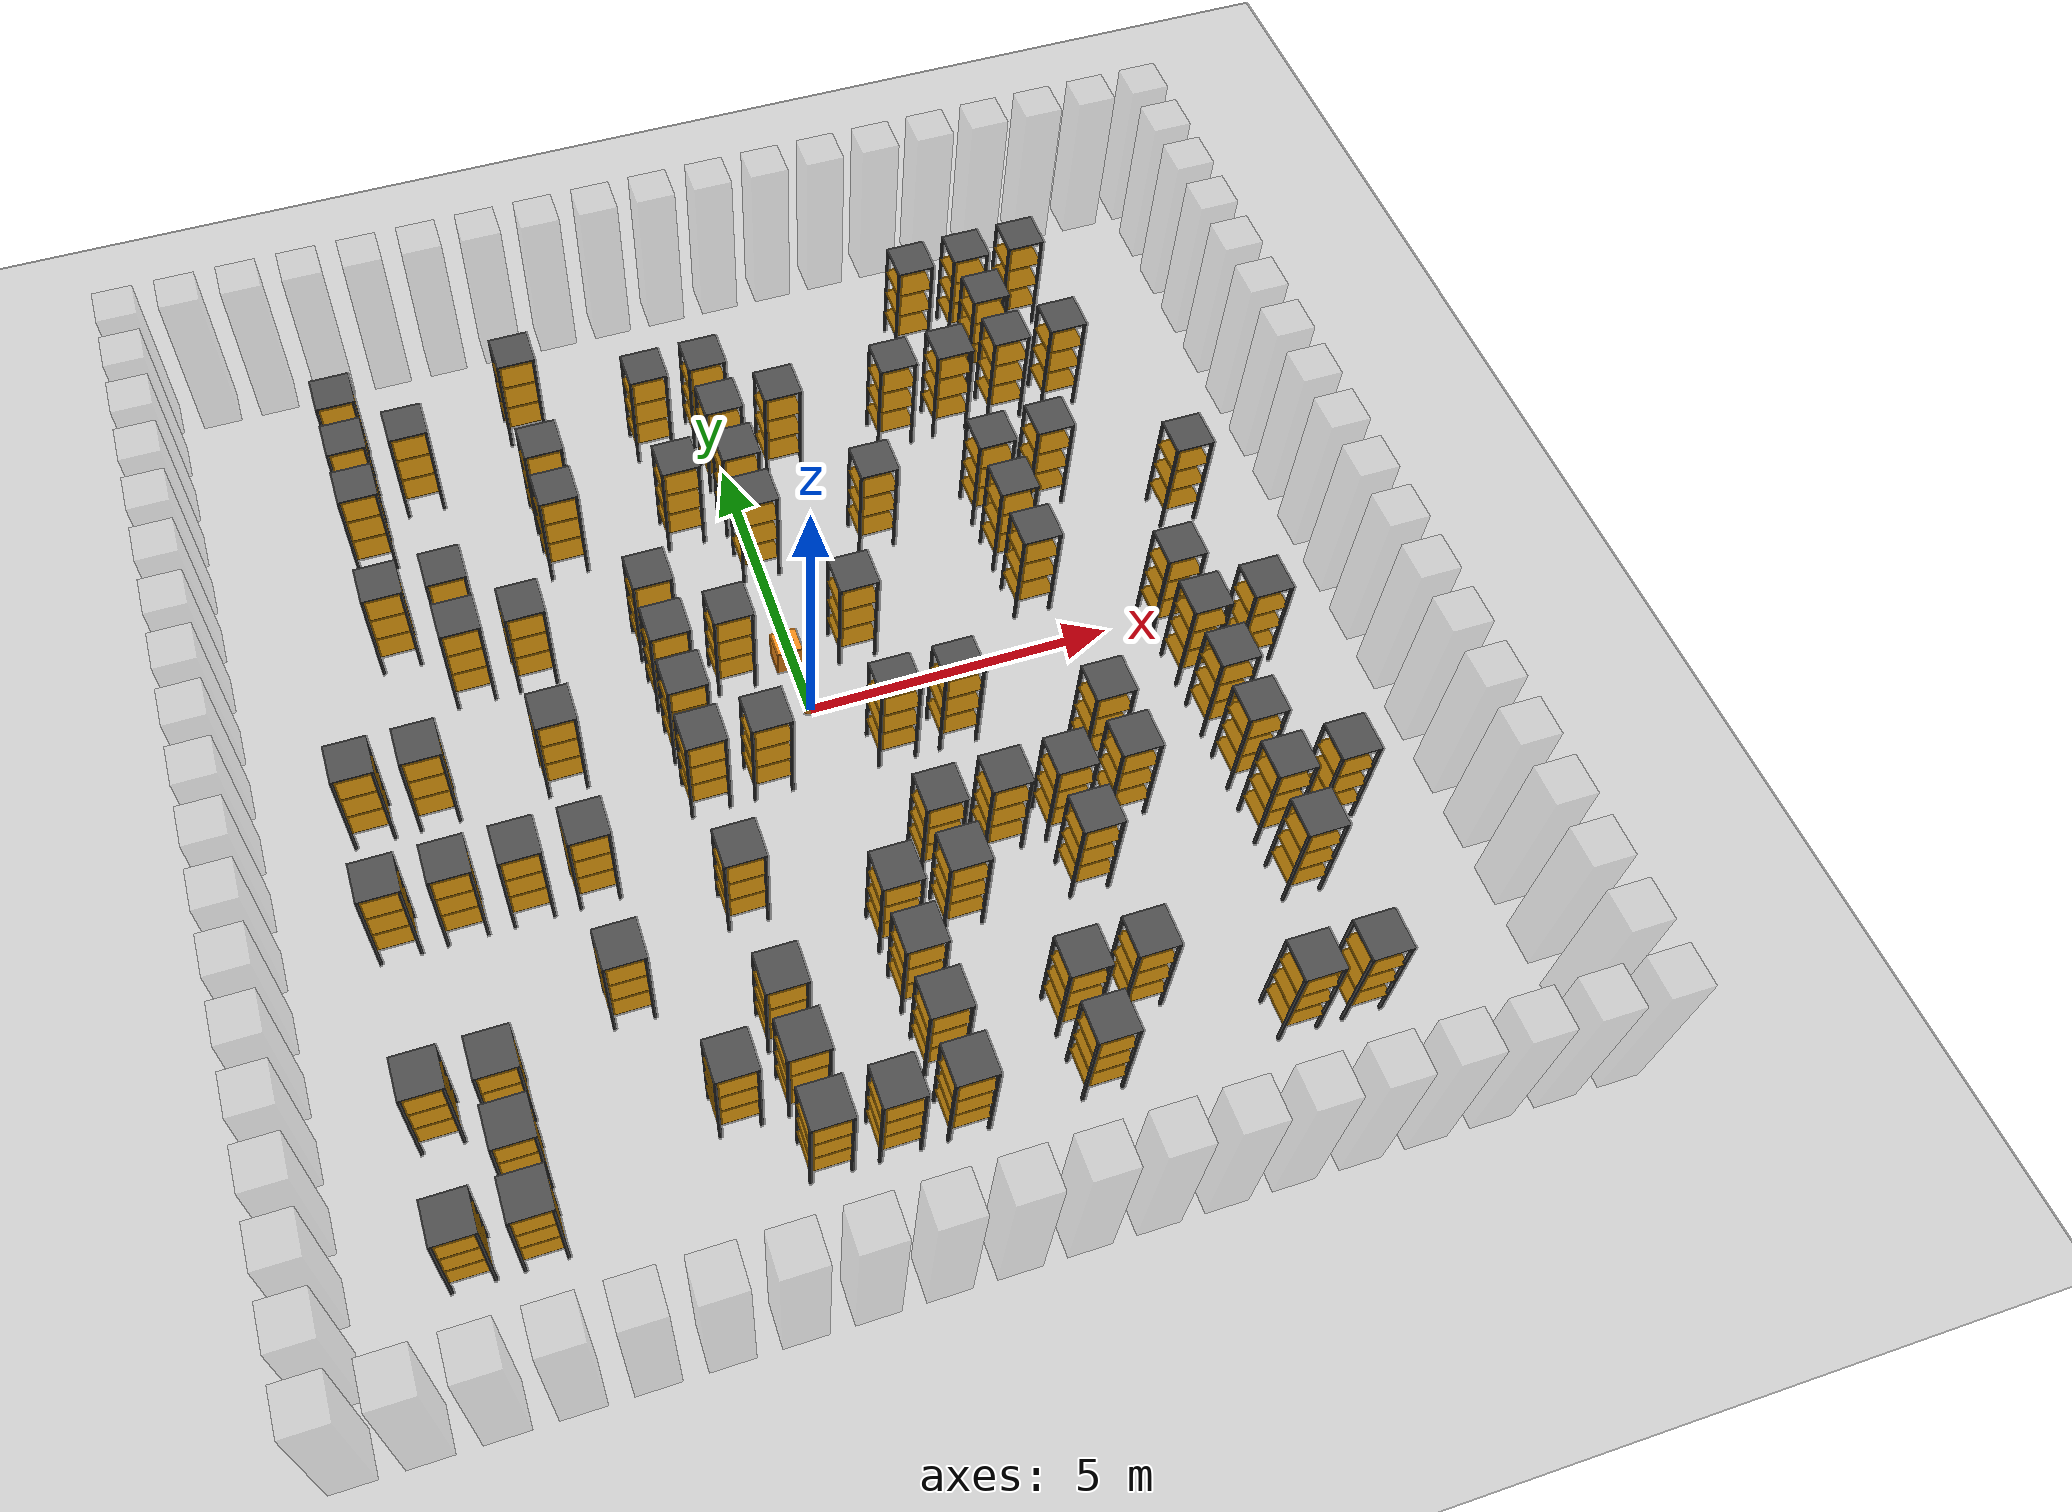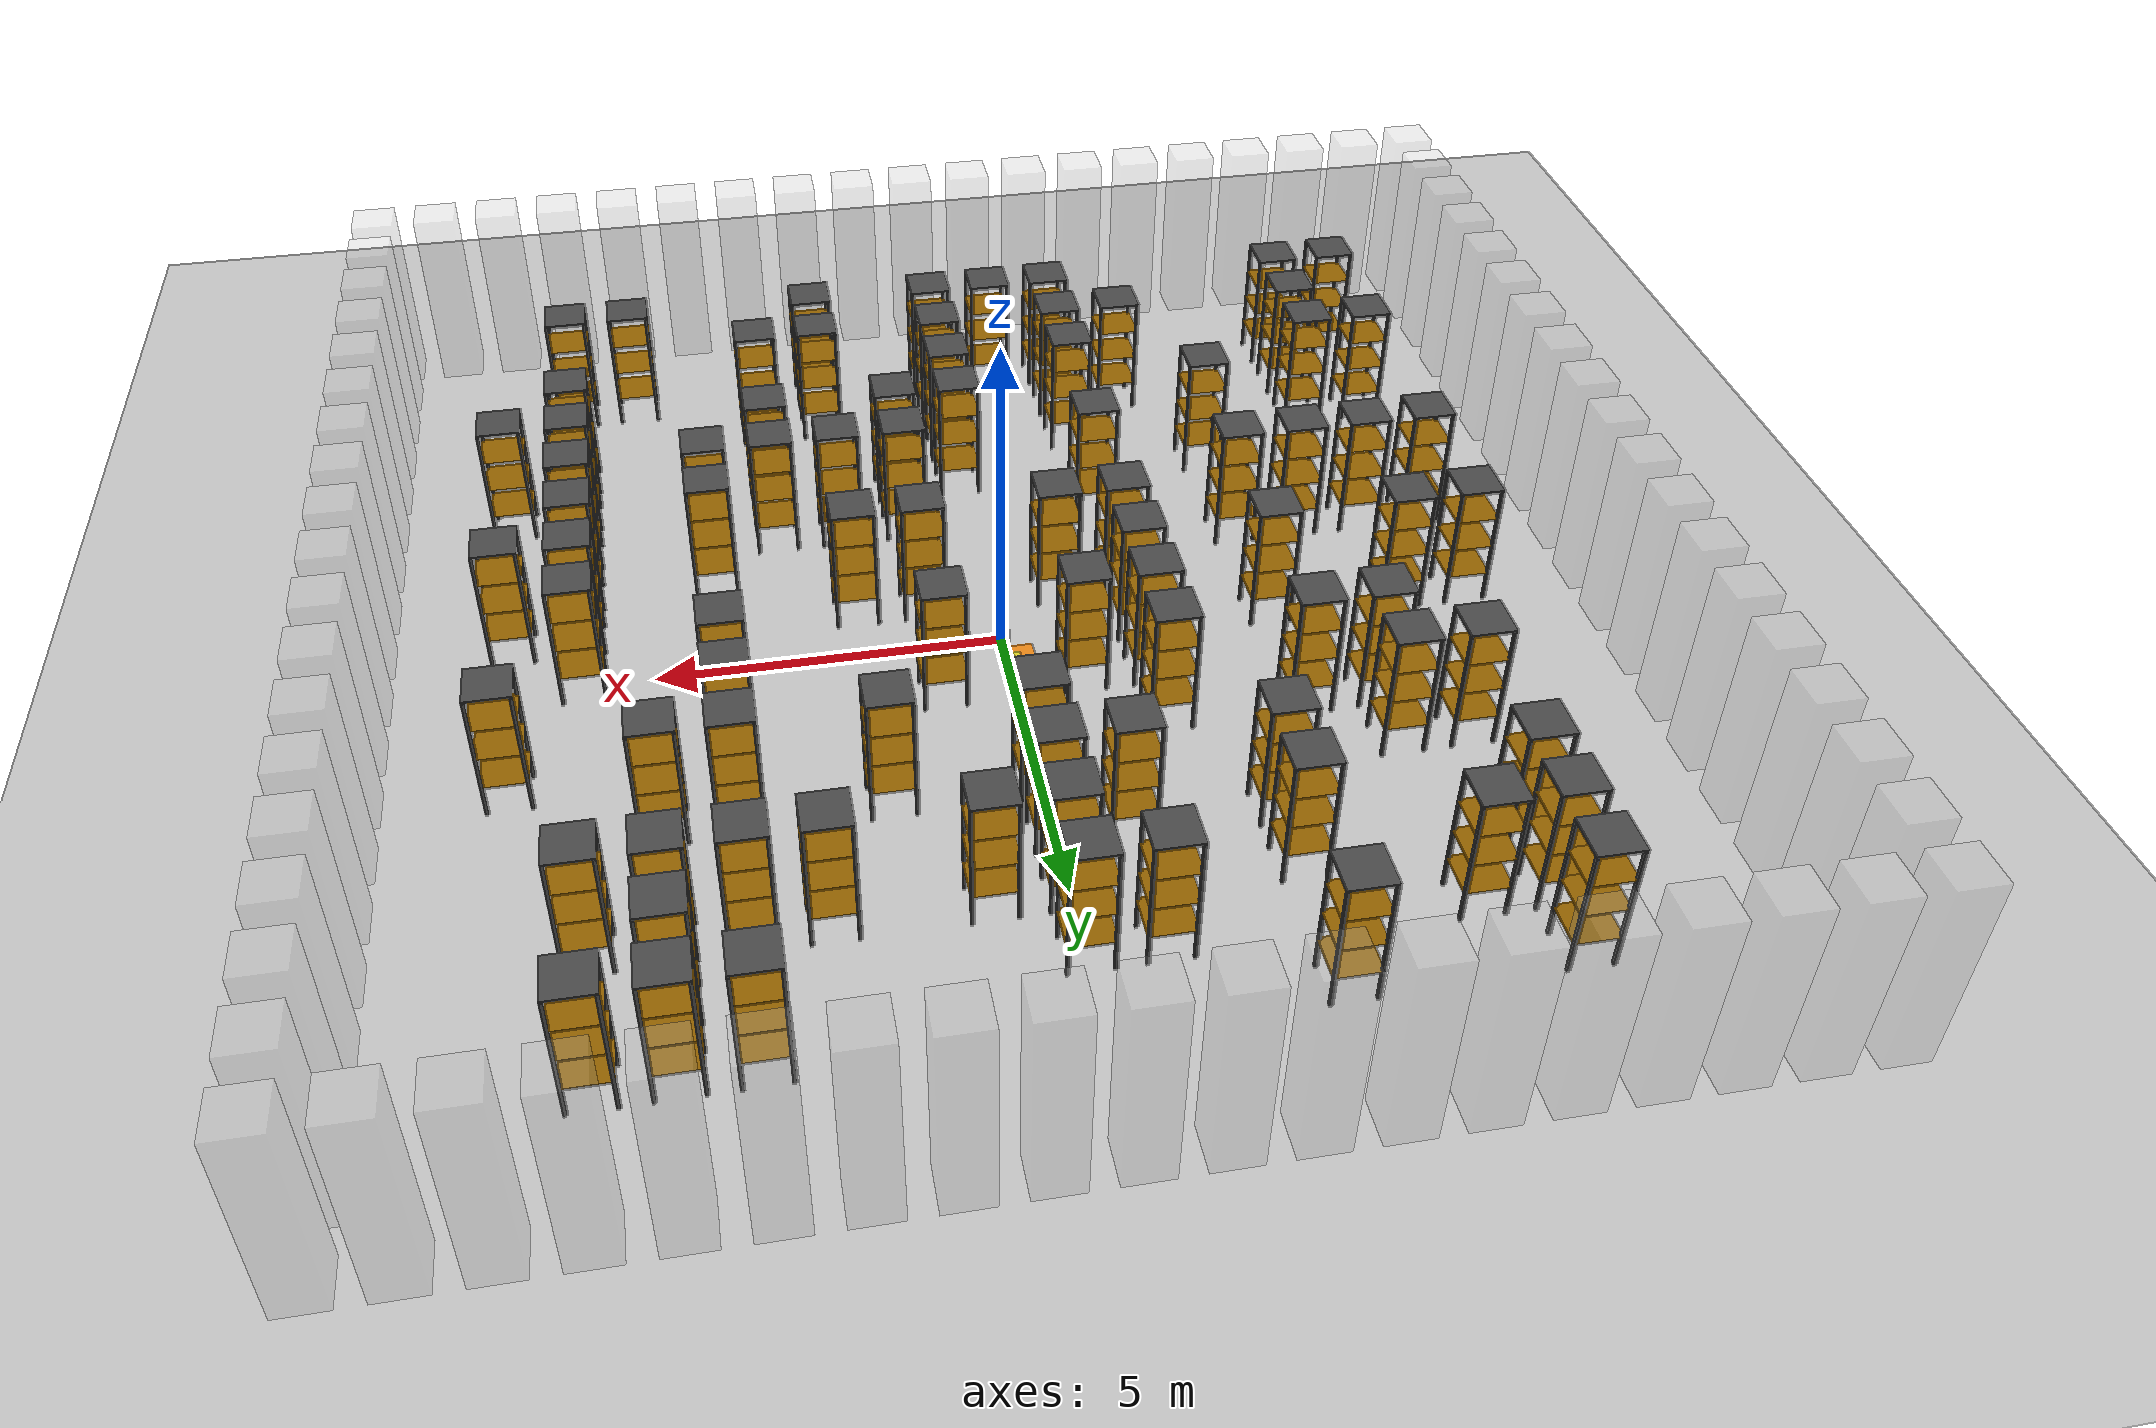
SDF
<sdf version="1.6">
 <world name="default">
  <light name="sun" type="directional">
   <pose>0 0 10 0 -0 0</pose>
   <diffuse>0.8 0.8 0.8 1</diffuse>
   <specular>0.2 0.2 0.2 1</specular>
   <attenuation>
    <range>1000</range>
    <constant>0.9</constant>
    <linear>0.01</linear>
    <quadratic>0.001</quadratic>
   </attenuation>
   <direction>-0.5 0.1 -0.9</direction>
  </light>
  <model name="ground_plane">
   <static>1</static>
   <link name="link">
    <collision name="collision">
     <geometry><plane><normal>0 0 1</normal><size>50 50</size></plane></geometry>
     <surface><friction><ode><mu>100</mu><mu2>50</mu2></ode></friction></surface>
    </collision>
    <visual name="visual">
     <cast_shadows>0</cast_shadows>
     <geometry><plane><normal>0 0 1</normal><size>100 100</size></plane></geometry>
     <material>
      <script><uri>file://media/materials/scripts/gazebo.material</uri><name>Gazebo/Grey</name></script>
     </material>
    </visual>
    <velocity_decay><linear>0</linear><angular>0</angular></velocity_decay>
   </link>
  </model>
  <physics name="default_physics" default="0" type="ode">
   <max_step_size>0.001</max_step_size>
   <real_time_factor>1</real_time_factor>
   <real_time_update_rate>1000</real_time_update_rate>
  </physics>
  <scene><ambient>0.4 0.4 0.4 1</ambient><background>0.7 0.7 0.7 1</background><shadows>0</shadows></scene>
  <spherical_coordinates>
   <surface_model>EARTH_WGS84</surface_model>
   <latitude_deg>0</latitude_deg>
   <longitude_deg>0</longitude_deg>
   <elevation>0</elevation>
   <heading_deg>0</heading_deg>
  </spherical_coordinates>
  <gravity>0 0 -9.8</gravity>
  <magnetic_field>6e-06 2.3e-05 -4.2e-05</magnetic_field>
  <atmosphere type="adiabatic"/>
  <model name="pole_0_0">
   <static>1</static>
   <link name="main_block">
    <pose>0 0 1.5 0 -0 0</pose>
    <collision name="collision"><geometry><box><size>0.65 0.65 3</size></box></geometry></collision>
    <visual name="visual">
     <geometry><box><size>0.65 0.65 3</size></box></geometry>
     <material><ambient>0.5 0.5 0.5 0.25</ambient><diffuse>0.75 0.75 0.75 0.25</diffuse></material>
    </visual>
   </link>
   <pose>-9 -9 0 0 -0 0</pose>
  </model>
  <model name="pole_0_1">
   <static>1</static>
   <link name="main_block">
    <pose>0 0 1.5 0 -0 0</pose>
    <collision name="collision"><geometry><box><size>0.65 0.65 3</size></box></geometry></collision>
    <visual name="visual">
     <geometry><box><size>0.65 0.65 3</size></box></geometry>
     <material><ambient>0.5 0.5 0.5 0.25</ambient><diffuse>0.75 0.75 0.75 0.25</diffuse></material>
    </visual>
   </link>
   <pose>-8 -9 0 0 -0 0</pose>
  </model>
  <model name="pole_0_2">
   <static>1</static>
   <link name="main_block">
    <pose>0 0 1.5 0 -0 0</pose>
    <collision name="collision"><geometry><box><size>0.65 0.65 3</size></box></geometry></collision>
    <visual name="visual">
     <geometry><box><size>0.65 0.65 3</size></box></geometry>
     <material><ambient>0.5 0.5 0.5 0.25</ambient><diffuse>0.75 0.75 0.75 0.25</diffuse></material>
    </visual>
   </link>
   <pose>-7 -9 0 0 -0 0</pose>
  </model>
  <model name="pole_0_3">
   <static>1</static>
   <link name="main_block">
    <pose>0 0 1.5 0 -0 0</pose>
    <collision name="collision"><geometry><box><size>0.65 0.65 3</size></box></geometry></collision>
    <visual name="visual">
     <geometry><box><size>0.65 0.65 3</size></box></geometry>
     <material><ambient>0.5 0.5 0.5 0.25</ambient><diffuse>0.75 0.75 0.75 0.25</diffuse></material>
    </visual>
   </link>
   <pose>-6 -9 0 0 -0 0</pose>
  </model>
  <model name="pole_0_4">
   <static>1</static>
   <link name="main_block">
    <pose>0 0 1.5 0 -0 0</pose>
    <collision name="collision"><geometry><box><size>0.65 0.65 3</size></box></geometry></collision>
    <visual name="visual">
     <geometry><box><size>0.65 0.65 3</size></box></geometry>
     <material><ambient>0.5 0.5 0.5 0.25</ambient><diffuse>0.75 0.75 0.75 0.25</diffuse></material>
    </visual>
   </link>
   <pose>-5 -9 0 0 -0 0</pose>
  </model>
  <model name="pole_0_5">
   <static>1</static>
   <link name="main_block">
    <pose>0 0 1.5 0 -0 0</pose>
    <collision name="collision"><geometry><box><size>0.65 0.65 3</size></box></geometry></collision>
    <visual name="visual">
     <geometry><box><size>0.65 0.65 3</size></box></geometry>
     <material><ambient>0.5 0.5 0.5 0.25</ambient><diffuse>0.75 0.75 0.75 0.25</diffuse></material>
    </visual>
   </link>
   <pose>-4 -9 0 0 -0 0</pose>
  </model>
  <model name="pole_0_6">
   <static>1</static>
   <link name="main_block">
    <pose>0 0 1.5 0 -0 0</pose>
    <collision name="collision"><geometry><box><size>0.65 0.65 3</size></box></geometry></collision>
    <visual name="visual">
     <geometry><box><size>0.65 0.65 3</size></box></geometry>
     <material><ambient>0.5 0.5 0.5 0.25</ambient><diffuse>0.75 0.75 0.75 0.25</diffuse></material>
    </visual>
   </link>
   <pose>-3 -9 0 0 -0 0</pose>
  </model>
  <model name="pole_0_7">
   <static>1</static>
   <link name="main_block">
    <pose>0 0 1.5 0 -0 0</pose>
    <collision name="collision"><geometry><box><size>0.65 0.65 3</size></box></geometry></collision>
    <visual name="visual">
     <geometry><box><size>0.65 0.65 3</size></box></geometry>
     <material><ambient>0.5 0.5 0.5 0.25</ambient><diffuse>0.75 0.75 0.75 0.25</diffuse></material>
    </visual>
   </link>
   <pose>-2 -9 0 0 -0 0</pose>
  </model>
  <model name="pole_0_8">
   <static>1</static>
   <link name="main_block">
    <pose>0 0 1.5 0 -0 0</pose>
    <collision name="collision"><geometry><box><size>0.65 0.65 3</size></box></geometry></collision>
    <visual name="visual">
     <geometry><box><size>0.65 0.65 3</size></box></geometry>
     <material><ambient>0.5 0.5 0.5 0.25</ambient><diffuse>0.75 0.75 0.75 0.25</diffuse></material>
    </visual>
   </link>
   <pose>-1 -9 0 0 -0 0</pose>
  </model>
  <model name="pole_0_9">
   <static>1</static>
   <link name="main_block">
    <pose>0 0 1.5 0 -0 0</pose>
    <collision name="collision"><geometry><box><size>0.65 0.65 3</size></box></geometry></collision>
    <visual name="visual">
     <geometry><box><size>0.65 0.65 3</size></box></geometry>
     <material><ambient>0.5 0.5 0.5 0.25</ambient><diffuse>0.75 0.75 0.75 0.25</diffuse></material>
    </visual>
   </link>
   <pose>0 -9 0 0 -0 0</pose>
  </model>
  <model name="pole_0_10">
   <static>1</static>
   <link name="main_block">
    <pose>0 0 1.5 0 -0 0</pose>
    <collision name="collision"><geometry><box><size>0.65 0.65 3</size></box></geometry></collision>
    <visual name="visual">
     <geometry><box><size>0.65 0.65 3</size></box></geometry>
     <material><ambient>0.5 0.5 0.5 0.25</ambient><diffuse>0.75 0.75 0.75 0.25</diffuse></material>
    </visual>
   </link>
   <pose>1 -9 0 0 -0 0</pose>
  </model>
  <model name="pole_0_11">
   <static>1</static>
   <link name="main_block">
    <pose>0 0 1.5 0 -0 0</pose>
    <collision name="collision"><geometry><box><size>0.65 0.65 3</size></box></geometry></collision>
    <visual name="visual">
     <geometry><box><size>0.65 0.65 3</size></box></geometry>
     <material><ambient>0.5 0.5 0.5 0.25</ambient><diffuse>0.75 0.75 0.75 0.25</diffuse></material>
    </visual>
   </link>
   <pose>2 -9 0 0 -0 0</pose>
  </model>
  <model name="pole_0_12">
   <static>1</static>
   <link name="main_block">
    <pose>0 0 1.5 0 -0 0</pose>
    <collision name="collision"><geometry><box><size>0.65 0.65 3</size></box></geometry></collision>
    <visual name="visual">
     <geometry><box><size>0.65 0.65 3</size></box></geometry>
     <material><ambient>0.5 0.5 0.5 0.25</ambient><diffuse>0.75 0.75 0.75 0.25</diffuse></material>
    </visual>
   </link>
   <pose>3 -9 0 0 -0 0</pose>
  </model>
  <model name="pole_0_13">
   <static>1</static>
   <link name="main_block">
    <pose>0 0 1.5 0 -0 0</pose>
    <collision name="collision"><geometry><box><size>0.65 0.65 3</size></box></geometry></collision>
    <visual name="visual">
     <geometry><box><size>0.65 0.65 3</size></box></geometry>
     <material><ambient>0.5 0.5 0.5 0.25</ambient><diffuse>0.75 0.75 0.75 0.25</diffuse></material>
    </visual>
   </link>
   <pose>4 -9 0 0 -0 0</pose>
  </model>
  <model name="pole_0_14">
   <static>1</static>
   <link name="main_block">
    <pose>0 0 1.5 0 -0 0</pose>
    <collision name="collision"><geometry><box><size>0.65 0.65 3</size></box></geometry></collision>
    <visual name="visual">
     <geometry><box><size>0.65 0.65 3</size></box></geometry>
     <material><ambient>0.5 0.5 0.5 0.25</ambient><diffuse>0.75 0.75 0.75 0.25</diffuse></material>
    </visual>
   </link>
   <pose>5 -9 0 0 -0 0</pose>
  </model>
  <model name="pole_0_15">
   <static>1</static>
   <link name="main_block">
    <pose>0 0 1.5 0 -0 0</pose>
    <collision name="collision"><geometry><box><size>0.65 0.65 3</size></box></geometry></collision>
    <visual name="visual">
     <geometry><box><size>0.65 0.65 3</size></box></geometry>
     <material><ambient>0.5 0.5 0.5 0.25</ambient><diffuse>0.75 0.75 0.75 0.25</diffuse></material>
    </visual>
   </link>
   <pose>6 -9 0 0 -0 0</pose>
  </model>
  <model name="pole_0_16">
   <static>1</static>
   <link name="main_block">
    <pose>0 0 1.5 0 -0 0</pose>
    <collision name="collision"><geometry><box><size>0.65 0.65 3</size></box></geometry></collision>
    <visual name="visual">
     <geometry><box><size>0.65 0.65 3</size></box></geometry>
     <material><ambient>0.5 0.5 0.5 0.25</ambient><diffuse>0.75 0.75 0.75 0.25</diffuse></material>
    </visual>
   </link>
   <pose>7 -9 0 0 -0 0</pose>
  </model>
  <model name="pole_0_17">
   <static>1</static>
   <link name="main_block">
    <pose>0 0 1.5 0 -0 0</pose>
    <collision name="collision"><geometry><box><size>0.65 0.65 3</size></box></geometry></collision>
    <visual name="visual">
     <geometry><box><size>0.65 0.65 3</size></box></geometry>
     <material><ambient>0.5 0.5 0.5 0.25</ambient><diffuse>0.75 0.75 0.75 0.25</diffuse></material>
    </visual>
   </link>
   <pose>8 -9 0 0 -0 0</pose>
  </model>
  <model name="pole_0_18">
   <static>1</static>
   <link name="main_block">
    <pose>0 0 1.5 0 -0 0</pose>
    <collision name="collision"><geometry><box><size>0.65 0.65 3</size></box></geometry></collision>
    <visual name="visual">
     <geometry><box><size>0.65 0.65 3</size></box></geometry>
     <material><ambient>0.5 0.5 0.5 0.25</ambient><diffuse>0.75 0.75 0.75 0.25</diffuse></material>
    </visual>
   </link>
   <pose>9 -9 0 0 -0 0</pose>
  </model>
  <model name="pole_1_0">
   <static>1</static>
   <link name="main_block">
    <pose>0 0 1.5 0 -0 0</pose>
    <collision name="collision"><geometry><box><size>0.65 0.65 3</size></box></geometry></collision>
    <visual name="visual">
     <geometry><box><size>0.65 0.65 3</size></box></geometry>
     <material><ambient>0.5 0.5 0.5 0.25</ambient><diffuse>0.75 0.75 0.75 0.25</diffuse></material>
    </visual>
   </link>
   <pose>-9 -8 0 0 -0 0</pose>
  </model>
  <model name="pole_1_18">
   <static>1</static>
   <link name="main_block">
    <pose>0 0 1.5 0 -0 0</pose>
    <collision name="collision"><geometry><box><size>0.65 0.65 3</size></box></geometry></collision>
    <visual name="visual">
     <geometry><box><size>0.65 0.65 3</size></box></geometry>
     <material><ambient>0.5 0.5 0.5 0.25</ambient><diffuse>0.75 0.75 0.75 0.25</diffuse></material>
    </visual>
   </link>
   <pose>9 -8 0 0 -0 0</pose>
  </model>
  <model name="pole_2_0">
   <static>1</static>
   <link name="main_block">
    <pose>0 0 1.5 0 -0 0</pose>
    <collision name="collision"><geometry><box><size>0.65 0.65 3</size></box></geometry></collision>
    <visual name="visual">
     <geometry><box><size>0.65 0.65 3</size></box></geometry>
     <material><ambient>0.5 0.5 0.5 0.25</ambient><diffuse>0.75 0.75 0.75 0.25</diffuse></material>
    </visual>
   </link>
   <pose>-9 -7 0 0 -0 0</pose>
  </model>
  <model name="warehouse_shelf_2_2">
   <static>1</static>
   <link name="main_block">
    <pose>0 0 1.25 0 -0 0</pose>
    <collision name="collision"><geometry><box><size>0.65 0.65 1.5</size></box></geometry></collision>
   </link>
   <link name="leg_1">
    <pose>0.3 0.3 1 0 -0 0</pose>
    <collision name="collision"><geometry><box><size>0.05 0.05 2</size></box></geometry></collision>
    <visual name="visual">
     <geometry><box><size>0.05 0.05 2</size></box></geometry>
     <material><ambient>0.2 0.2 0.2 1</ambient><diffuse>0.3 0.3 0.3 1</diffuse></material>
    </visual>
   </link>
   <link name="leg_2">
    <pose>-0.3 0.3 1 0 -0 0</pose>
    <collision name="collision"><geometry><box><size>0.05 0.05 2</size></box></geometry></collision>
    <visual name="visual">
     <geometry><box><size>0.05 0.05 2</size></box></geometry>
     <material><ambient>0.2 0.2 0.2 1</ambient><diffuse>0.3 0.3 0.3 1</diffuse></material>
    </visual>
   </link>
   <link name="leg_3">
    <pose>-0.3 -0.3 1 0 -0 0</pose>
    <collision name="collision"><geometry><box><size>0.05 0.05 2</size></box></geometry></collision>
    <visual name="visual">
     <geometry><box><size>0.05 0.05 2</size></box></geometry>
     <material><ambient>0.2 0.2 0.2 1</ambient><diffuse>0.3 0.3 0.3 1</diffuse></material>
    </visual>
   </link>
   <link name="leg_4">
    <pose>0.3 -0.3 1 0 -0 0</pose>
    <collision name="collision"><geometry><box><size>0.05 0.05 2</size></box></geometry></collision>
    <visual name="visual">
     <geometry><box><size>0.05 0.05 2</size></box></geometry>
     <material><ambient>0.2 0.2 0.2 1</ambient><diffuse>0.3 0.3 0.3 1</diffuse></material>
    </visual>
   </link>
   <link name="shelf_0">
    <pose>0 0 0.49 0 -0 0</pose>
    <visual name="visual">
     <geometry><box><size>0.649 0.649 0.02</size></box></geometry>
     <material><ambient>0.2 0.05 0 1</ambient><diffuse>0.6 0.4 0 1</diffuse></material>
    </visual>
   </link>
   <link name="shelf_1">
    <pose>0 0 0.99 0 -0 0</pose>
    <visual name="visual">
     <geometry><box><size>0.649 0.649 0.02</size></box></geometry>
     <material><ambient>0.2 0.05 0 1</ambient><diffuse>0.6 0.4 0 1</diffuse></material>
    </visual>
   </link>
   <link name="shelf_2">
    <pose>0 0 1.49 0 -0 0</pose>
    <visual name="visual">
     <geometry><box><size>0.649 0.649 0.02</size></box></geometry>
     <material><ambient>0.2 0.05 0 1</ambient><diffuse>0.6 0.4 0 1</diffuse></material>
    </visual>
   </link>
   <link name="shelf_top">
    <pose>0 0 1.99 0 -0 0</pose>
    <visual name="visual">
     <geometry><box><size>0.65 0.65 0.04</size></box></geometry>
     <material><ambient>0.2 0.2 0.2 1</ambient><diffuse>0.3 0.3 0.3 1</diffuse></material>
    </visual>
   </link>
   <pose>-7 -7 0 0 -0 0</pose>
  </model>
  <model name="warehouse_shelf_2_3">
   <static>1</static>
   <link name="main_block">
    <pose>0 0 1.25 0 -0 0</pose>
    <collision name="collision"><geometry><box><size>0.65 0.65 1.5</size></box></geometry></collision>
   </link>
   <link name="leg_1">
    <pose>0.3 0.3 1 0 -0 0</pose>
    <collision name="collision"><geometry><box><size>0.05 0.05 2</size></box></geometry></collision>
    <visual name="visual">
     <geometry><box><size>0.05 0.05 2</size></box></geometry>
     <material><ambient>0.2 0.2 0.2 1</ambient><diffuse>0.3 0.3 0.3 1</diffuse></material>
    </visual>
   </link>
   <link name="leg_2">
    <pose>-0.3 0.3 1 0 -0 0</pose>
    <collision name="collision"><geometry><box><size>0.05 0.05 2</size></box></geometry></collision>
    <visual name="visual">
     <geometry><box><size>0.05 0.05 2</size></box></geometry>
     <material><ambient>0.2 0.2 0.2 1</ambient><diffuse>0.3 0.3 0.3 1</diffuse></material>
    </visual>
   </link>
   <link name="leg_3">
    <pose>-0.3 -0.3 1 0 -0 0</pose>
    <collision name="collision"><geometry><box><size>0.05 0.05 2</size></box></geometry></collision>
    <visual name="visual">
     <geometry><box><size>0.05 0.05 2</size></box></geometry>
     <material><ambient>0.2 0.2 0.2 1</ambient><diffuse>0.3 0.3 0.3 1</diffuse></material>
    </visual>
   </link>
   <link name="leg_4">
    <pose>0.3 -0.3 1 0 -0 0</pose>
    <collision name="collision"><geometry><box><size>0.05 0.05 2</size></box></geometry></collision>
    <visual name="visual">
     <geometry><box><size>0.05 0.05 2</size></box></geometry>
     <material><ambient>0.2 0.2 0.2 1</ambient><diffuse>0.3 0.3 0.3 1</diffuse></material>
    </visual>
   </link>
   <link name="shelf_0">
    <pose>0 0 0.49 0 -0 0</pose>
    <visual name="visual">
     <geometry><box><size>0.649 0.649 0.02</size></box></geometry>
     <material><ambient>0.2 0.05 0 1</ambient><diffuse>0.6 0.4 0 1</diffuse></material>
    </visual>
   </link>
   <link name="shelf_1">
    <pose>0 0 0.99 0 -0 0</pose>
    <visual name="visual">
     <geometry><box><size>0.649 0.649 0.02</size></box></geometry>
     <material><ambient>0.2 0.05 0 1</ambient><diffuse>0.6 0.4 0 1</diffuse></material>
    </visual>
   </link>
   <link name="shelf_2">
    <pose>0 0 1.49 0 -0 0</pose>
    <visual name="visual">
     <geometry><box><size>0.649 0.649 0.02</size></box></geometry>
     <material><ambient>0.2 0.05 0 1</ambient><diffuse>0.6 0.4 0 1</diffuse></material>
    </visual>
   </link>
   <link name="shelf_top">
    <pose>0 0 1.99 0 -0 0</pose>
    <visual name="visual">
     <geometry><box><size>0.65 0.65 0.04</size></box></geometry>
     <material><ambient>0.2 0.2 0.2 1</ambient><diffuse>0.3 0.3 0.3 1</diffuse></material>
    </visual>
   </link>
   <pose>-6 -7 0 0 -0 0</pose>
  </model>
  <model name="warehouse_shelf_2_7">
   <static>1</static>
   <link name="main_block">
    <pose>0 0 1.25 0 -0 0</pose>
    <collision name="collision"><geometry><box><size>0.65 0.65 1.5</size></box></geometry></collision>
   </link>
   <link name="leg_1">
    <pose>0.3 0.3 1 0 -0 0</pose>
    <collision name="collision"><geometry><box><size>0.05 0.05 2</size></box></geometry></collision>
    <visual name="visual">
     <geometry><box><size>0.05 0.05 2</size></box></geometry>
     <material><ambient>0.2 0.2 0.2 1</ambient><diffuse>0.3 0.3 0.3 1</diffuse></material>
    </visual>
   </link>
   <link name="leg_2">
    <pose>-0.3 0.3 1 0 -0 0</pose>
    <collision name="collision"><geometry><box><size>0.05 0.05 2</size></box></geometry></collision>
    <visual name="visual">
     <geometry><box><size>0.05 0.05 2</size></box></geometry>
     <material><ambient>0.2 0.2 0.2 1</ambient><diffuse>0.3 0.3 0.3 1</diffuse></material>
    </visual>
   </link>
   <link name="leg_3">
    <pose>-0.3 -0.3 1 0 -0 0</pose>
    <collision name="collision"><geometry><box><size>0.05 0.05 2</size></box></geometry></collision>
    <visual name="visual">
     <geometry><box><size>0.05 0.05 2</size></box></geometry>
     <material><ambient>0.2 0.2 0.2 1</ambient><diffuse>0.3 0.3 0.3 1</diffuse></material>
    </visual>
   </link>
   <link name="leg_4">
    <pose>0.3 -0.3 1 0 -0 0</pose>
    <collision name="collision"><geometry><box><size>0.05 0.05 2</size></box></geometry></collision>
    <visual name="visual">
     <geometry><box><size>0.05 0.05 2</size></box></geometry>
     <material><ambient>0.2 0.2 0.2 1</ambient><diffuse>0.3 0.3 0.3 1</diffuse></material>
    </visual>
   </link>
   <link name="shelf_0">
    <pose>0 0 0.49 0 -0 0</pose>
    <visual name="visual">
     <geometry><box><size>0.649 0.649 0.02</size></box></geometry>
     <material><ambient>0.2 0.05 0 1</ambient><diffuse>0.6 0.4 0 1</diffuse></material>
    </visual>
   </link>
   <link name="shelf_1">
    <pose>0 0 0.99 0 -0 0</pose>
    <visual name="visual">
     <geometry><box><size>0.649 0.649 0.02</size></box></geometry>
     <material><ambient>0.2 0.05 0 1</ambient><diffuse>0.6 0.4 0 1</diffuse></material>
    </visual>
   </link>
   <link name="shelf_2">
    <pose>0 0 1.49 0 -0 0</pose>
    <visual name="visual">
     <geometry><box><size>0.649 0.649 0.02</size></box></geometry>
     <material><ambient>0.2 0.05 0 1</ambient><diffuse>0.6 0.4 0 1</diffuse></material>
    </visual>
   </link>
   <link name="shelf_top">
    <pose>0 0 1.99 0 -0 0</pose>
    <visual name="visual">
     <geometry><box><size>0.65 0.65 0.04</size></box></geometry>
     <material><ambient>0.2 0.2 0.2 1</ambient><diffuse>0.3 0.3 0.3 1</diffuse></material>
    </visual>
   </link>
   <pose>-2 -7 0 0 -0 0</pose>
  </model>
  <model name="warehouse_shelf_2_8">
   <static>1</static>
   <link name="main_block">
    <pose>0 0 1.25 0 -0 0</pose>
    <collision name="collision"><geometry><box><size>0.65 0.65 1.5</size></box></geometry></collision>
   </link>
   <link name="leg_1">
    <pose>0.3 0.3 1 0 -0 0</pose>
    <collision name="collision"><geometry><box><size>0.05 0.05 2</size></box></geometry></collision>
    <visual name="visual">
     <geometry><box><size>0.05 0.05 2</size></box></geometry>
     <material><ambient>0.2 0.2 0.2 1</ambient><diffuse>0.3 0.3 0.3 1</diffuse></material>
    </visual>
   </link>
   <link name="leg_2">
    <pose>-0.3 0.3 1 0 -0 0</pose>
    <collision name="collision"><geometry><box><size>0.05 0.05 2</size></box></geometry></collision>
    <visual name="visual">
     <geometry><box><size>0.05 0.05 2</size></box></geometry>
     <material><ambient>0.2 0.2 0.2 1</ambient><diffuse>0.3 0.3 0.3 1</diffuse></material>
    </visual>
   </link>
   <link name="leg_3">
    <pose>-0.3 -0.3 1 0 -0 0</pose>
    <collision name="collision"><geometry><box><size>0.05 0.05 2</size></box></geometry></collision>
    <visual name="visual">
     <geometry><box><size>0.05 0.05 2</size></box></geometry>
     <material><ambient>0.2 0.2 0.2 1</ambient><diffuse>0.3 0.3 0.3 1</diffuse></material>
    </visual>
   </link>
   <link name="leg_4">
    <pose>0.3 -0.3 1 0 -0 0</pose>
    <collision name="collision"><geometry><box><size>0.05 0.05 2</size></box></geometry></collision>
    <visual name="visual">
     <geometry><box><size>0.05 0.05 2</size></box></geometry>
     <material><ambient>0.2 0.2 0.2 1</ambient><diffuse>0.3 0.3 0.3 1</diffuse></material>
    </visual>
   </link>
   <link name="shelf_0">
    <pose>0 0 0.49 0 -0 0</pose>
    <visual name="visual">
     <geometry><box><size>0.649 0.649 0.02</size></box></geometry>
     <material><ambient>0.2 0.05 0 1</ambient><diffuse>0.6 0.4 0 1</diffuse></material>
    </visual>
   </link>
   <link name="shelf_1">
    <pose>0 0 0.99 0 -0 0</pose>
    <visual name="visual">
     <geometry><box><size>0.649 0.649 0.02</size></box></geometry>
     <material><ambient>0.2 0.05 0 1</ambient><diffuse>0.6 0.4 0 1</diffuse></material>
    </visual>
   </link>
   <link name="shelf_2">
    <pose>0 0 1.49 0 -0 0</pose>
    <visual name="visual">
     <geometry><box><size>0.649 0.649 0.02</size></box></geometry>
     <material><ambient>0.2 0.05 0 1</ambient><diffuse>0.6 0.4 0 1</diffuse></material>
    </visual>
   </link>
   <link name="shelf_top">
    <pose>0 0 1.99 0 -0 0</pose>
    <visual name="visual">
     <geometry><box><size>0.65 0.65 0.04</size></box></geometry>
     <material><ambient>0.2 0.2 0.2 1</ambient><diffuse>0.3 0.3 0.3 1</diffuse></material>
    </visual>
   </link>
   <pose>-1 -7 0 0 -0 0</pose>
  </model>
  <model name="warehouse_shelf_2_9">
   <static>1</static>
   <link name="main_block">
    <pose>0 0 1.25 0 -0 0</pose>
    <collision name="collision"><geometry><box><size>0.65 0.65 1.5</size></box></geometry></collision>
   </link>
   <link name="leg_1">
    <pose>0.3 0.3 1 0 -0 0</pose>
    <collision name="collision"><geometry><box><size>0.05 0.05 2</size></box></geometry></collision>
    <visual name="visual">
     <geometry><box><size>0.05 0.05 2</size></box></geometry>
     <material><ambient>0.2 0.2 0.2 1</ambient><diffuse>0.3 0.3 0.3 1</diffuse></material>
    </visual>
   </link>
   <link name="leg_2">
    <pose>-0.3 0.3 1 0 -0 0</pose>
    <collision name="collision"><geometry><box><size>0.05 0.05 2</size></box></geometry></collision>
    <visual name="visual">
     <geometry><box><size>0.05 0.05 2</size></box></geometry>
     <material><ambient>0.2 0.2 0.2 1</ambient><diffuse>0.3 0.3 0.3 1</diffuse></material>
    </visual>
   </link>
   <link name="leg_3">
    <pose>-0.3 -0.3 1 0 -0 0</pose>
    <collision name="collision"><geometry><box><size>0.05 0.05 2</size></box></geometry></collision>
    <visual name="visual">
     <geometry><box><size>0.05 0.05 2</size></box></geometry>
     <material><ambient>0.2 0.2 0.2 1</ambient><diffuse>0.3 0.3 0.3 1</diffuse></material>
    </visual>
   </link>
   <link name="leg_4">
    <pose>0.3 -0.3 1 0 -0 0</pose>
    <collision name="collision"><geometry><box><size>0.05 0.05 2</size></box></geometry></collision>
    <visual name="visual">
     <geometry><box><size>0.05 0.05 2</size></box></geometry>
     <material><ambient>0.2 0.2 0.2 1</ambient><diffuse>0.3 0.3 0.3 1</diffuse></material>
    </visual>
   </link>
   <link name="shelf_0">
    <pose>0 0 0.49 0 -0 0</pose>
    <visual name="visual">
     <geometry><box><size>0.649 0.649 0.02</size></box></geometry>
     <material><ambient>0.2 0.05 0 1</ambient><diffuse>0.6 0.4 0 1</diffuse></material>
    </visual>
   </link>
   <link name="shelf_1">
    <pose>0 0 0.99 0 -0 0</pose>
    <visual name="visual">
     <geometry><box><size>0.649 0.649 0.02</size></box></geometry>
     <material><ambient>0.2 0.05 0 1</ambient><diffuse>0.6 0.4 0 1</diffuse></material>
    </visual>
   </link>
   <link name="shelf_2">
    <pose>0 0 1.49 0 -0 0</pose>
    <visual name="visual">
     <geometry><box><size>0.649 0.649 0.02</size></box></geometry>
     <material><ambient>0.2 0.05 0 1</ambient><diffuse>0.6 0.4 0 1</diffuse></material>
    </visual>
   </link>
   <link name="shelf_top">
    <pose>0 0 1.99 0 -0 0</pose>
    <visual name="visual">
     <geometry><box><size>0.65 0.65 0.04</size></box></geometry>
     <material><ambient>0.2 0.2 0.2 1</ambient><diffuse>0.3 0.3 0.3 1</diffuse></material>
    </visual>
   </link>
   <pose>0 -7 0 0 -0 0</pose>
  </model>
  <model name="warehouse_shelf_2_11">
   <static>1</static>
   <link name="main_block">
    <pose>0 0 1.25 0 -0 0</pose>
    <collision name="collision"><geometry><box><size>0.65 0.65 1.5</size></box></geometry></collision>
   </link>
   <link name="leg_1">
    <pose>0.3 0.3 1 0 -0 0</pose>
    <collision name="collision"><geometry><box><size>0.05 0.05 2</size></box></geometry></collision>
    <visual name="visual">
     <geometry><box><size>0.05 0.05 2</size></box></geometry>
     <material><ambient>0.2 0.2 0.2 1</ambient><diffuse>0.3 0.3 0.3 1</diffuse></material>
    </visual>
   </link>
   <link name="leg_2">
    <pose>-0.3 0.3 1 0 -0 0</pose>
    <collision name="collision"><geometry><box><size>0.05 0.05 2</size></box></geometry></collision>
    <visual name="visual">
     <geometry><box><size>0.05 0.05 2</size></box></geometry>
     <material><ambient>0.2 0.2 0.2 1</ambient><diffuse>0.3 0.3 0.3 1</diffuse></material>
    </visual>
   </link>
   <link name="leg_3">
    <pose>-0.3 -0.3 1 0 -0 0</pose>
    <collision name="collision"><geometry><box><size>0.05 0.05 2</size></box></geometry></collision>
    <visual name="visual">
     <geometry><box><size>0.05 0.05 2</size></box></geometry>
     <material><ambient>0.2 0.2 0.2 1</ambient><diffuse>0.3 0.3 0.3 1</diffuse></material>
    </visual>
   </link>
   <link name="leg_4">
    <pose>0.3 -0.3 1 0 -0 0</pose>
    <collision name="collision"><geometry><box><size>0.05 0.05 2</size></box></geometry></collision>
    <visual name="visual">
     <geometry><box><size>0.05 0.05 2</size></box></geometry>
     <material><ambient>0.2 0.2 0.2 1</ambient><diffuse>0.3 0.3 0.3 1</diffuse></material>
    </visual>
   </link>
   <link name="shelf_0">
    <pose>0 0 0.49 0 -0 0</pose>
    <visual name="visual">
     <geometry><box><size>0.649 0.649 0.02</size></box></geometry>
     <material><ambient>0.2 0.05 0 1</ambient><diffuse>0.6 0.4 0 1</diffuse></material>
    </visual>
   </link>
   <link name="shelf_1">
    <pose>0 0 0.99 0 -0 0</pose>
    <visual name="visual">
     <geometry><box><size>0.649 0.649 0.02</size></box></geometry>
     <material><ambient>0.2 0.05 0 1</ambient><diffuse>0.6 0.4 0 1</diffuse></material>
    </visual>
   </link>
   <link name="shelf_2">
    <pose>0 0 1.49 0 -0 0</pose>
    <visual name="visual">
     <geometry><box><size>0.649 0.649 0.02</size></box></geometry>
     <material><ambient>0.2 0.05 0 1</ambient><diffuse>0.6 0.4 0 1</diffuse></material>
    </visual>
   </link>
   <link name="shelf_top">
    <pose>0 0 1.99 0 -0 0</pose>
    <visual name="visual">
     <geometry><box><size>0.65 0.65 0.04</size></box></geometry>
     <material><ambient>0.2 0.2 0.2 1</ambient><diffuse>0.3 0.3 0.3 1</diffuse></material>
    </visual>
   </link>
   <pose>2 -7 0 0 -0 0</pose>
  </model>
  <model name="warehouse_shelf_2_14">
   <static>1</static>
   <link name="main_block">
    <pose>0 0 1.25 0 -0 0</pose>
    <collision name="collision"><geometry><box><size>0.65 0.65 1.5</size></box></geometry></collision>
   </link>
   <link name="leg_1">
    <pose>0.3 0.3 1 0 -0 0</pose>
    <collision name="collision"><geometry><box><size>0.05 0.05 2</size></box></geometry></collision>
    <visual name="visual">
     <geometry><box><size>0.05 0.05 2</size></box></geometry>
     <material><ambient>0.2 0.2 0.2 1</ambient><diffuse>0.3 0.3 0.3 1</diffuse></material>
    </visual>
   </link>
   <link name="leg_2">
    <pose>-0.3 0.3 1 0 -0 0</pose>
    <collision name="collision"><geometry><box><size>0.05 0.05 2</size></box></geometry></collision>
    <visual name="visual">
     <geometry><box><size>0.05 0.05 2</size></box></geometry>
     <material><ambient>0.2 0.2 0.2 1</ambient><diffuse>0.3 0.3 0.3 1</diffuse></material>
    </visual>
   </link>
   <link name="leg_3">
    <pose>-0.3 -0.3 1 0 -0 0</pose>
    <collision name="collision"><geometry><box><size>0.05 0.05 2</size></box></geometry></collision>
    <visual name="visual">
     <geometry><box><size>0.05 0.05 2</size></box></geometry>
     <material><ambient>0.2 0.2 0.2 1</ambient><diffuse>0.3 0.3 0.3 1</diffuse></material>
    </visual>
   </link>
   <link name="leg_4">
    <pose>0.3 -0.3 1 0 -0 0</pose>
    <collision name="collision"><geometry><box><size>0.05 0.05 2</size></box></geometry></collision>
    <visual name="visual">
     <geometry><box><size>0.05 0.05 2</size></box></geometry>
     <material><ambient>0.2 0.2 0.2 1</ambient><diffuse>0.3 0.3 0.3 1</diffuse></material>
    </visual>
   </link>
   <link name="shelf_0">
    <pose>0 0 0.49 0 -0 0</pose>
    <visual name="visual">
     <geometry><box><size>0.649 0.649 0.02</size></box></geometry>
     <material><ambient>0.2 0.05 0 1</ambient><diffuse>0.6 0.4 0 1</diffuse></material>
    </visual>
   </link>
   <link name="shelf_1">
    <pose>0 0 0.99 0 -0 0</pose>
    <visual name="visual">
     <geometry><box><size>0.649 0.649 0.02</size></box></geometry>
     <material><ambient>0.2 0.05 0 1</ambient><diffuse>0.6 0.4 0 1</diffuse></material>
    </visual>
   </link>
   <link name="shelf_2">
    <pose>0 0 1.49 0 -0 0</pose>
    <visual name="visual">
     <geometry><box><size>0.649 0.649 0.02</size></box></geometry>
     <material><ambient>0.2 0.05 0 1</ambient><diffuse>0.6 0.4 0 1</diffuse></material>
    </visual>
   </link>
   <link name="shelf_top">
    <pose>0 0 1.99 0 -0 0</pose>
    <visual name="visual">
     <geometry><box><size>0.65 0.65 0.04</size></box></geometry>
     <material><ambient>0.2 0.2 0.2 1</ambient><diffuse>0.3 0.3 0.3 1</diffuse></material>
    </visual>
   </link>
   <pose>5 -7 0 0 -0 0</pose>
  </model>
  <model name="warehouse_shelf_2_15">
   <static>1</static>
   <link name="main_block">
    <pose>0 0 1.25 0 -0 0</pose>
    <collision name="collision"><geometry><box><size>0.65 0.65 1.5</size></box></geometry></collision>
   </link>
   <link name="leg_1">
    <pose>0.3 0.3 1 0 -0 0</pose>
    <collision name="collision"><geometry><box><size>0.05 0.05 2</size></box></geometry></collision>
    <visual name="visual">
     <geometry><box><size>0.05 0.05 2</size></box></geometry>
     <material><ambient>0.2 0.2 0.2 1</ambient><diffuse>0.3 0.3 0.3 1</diffuse></material>
    </visual>
   </link>
   <link name="leg_2">
    <pose>-0.3 0.3 1 0 -0 0</pose>
    <collision name="collision"><geometry><box><size>0.05 0.05 2</size></box></geometry></collision>
    <visual name="visual">
     <geometry><box><size>0.05 0.05 2</size></box></geometry>
     <material><ambient>0.2 0.2 0.2 1</ambient><diffuse>0.3 0.3 0.3 1</diffuse></material>
    </visual>
   </link>
   <link name="leg_3">
    <pose>-0.3 -0.3 1 0 -0 0</pose>
    <collision name="collision"><geometry><box><size>0.05 0.05 2</size></box></geometry></collision>
    <visual name="visual">
     <geometry><box><size>0.05 0.05 2</size></box></geometry>
     <material><ambient>0.2 0.2 0.2 1</ambient><diffuse>0.3 0.3 0.3 1</diffuse></material>
    </visual>
   </link>
   <link name="leg_4">
    <pose>0.3 -0.3 1 0 -0 0</pose>
    <collision name="collision"><geometry><box><size>0.05 0.05 2</size></box></geometry></collision>
    <visual name="visual">
     <geometry><box><size>0.05 0.05 2</size></box></geometry>
     <material><ambient>0.2 0.2 0.2 1</ambient><diffuse>0.3 0.3 0.3 1</diffuse></material>
    </visual>
   </link>
   <link name="shelf_0">
    <pose>0 0 0.49 0 -0 0</pose>
    <visual name="visual">
     <geometry><box><size>0.649 0.649 0.02</size></box></geometry>
     <material><ambient>0.2 0.05 0 1</ambient><diffuse>0.6 0.4 0 1</diffuse></material>
    </visual>
   </link>
   <link name="shelf_1">
    <pose>0 0 0.99 0 -0 0</pose>
    <visual name="visual">
     <geometry><box><size>0.649 0.649 0.02</size></box></geometry>
     <material><ambient>0.2 0.05 0 1</ambient><diffuse>0.6 0.4 0 1</diffuse></material>
    </visual>
   </link>
   <link name="shelf_2">
    <pose>0 0 1.49 0 -0 0</pose>
    <visual name="visual">
     <geometry><box><size>0.649 0.649 0.02</size></box></geometry>
     <material><ambient>0.2 0.05 0 1</ambient><diffuse>0.6 0.4 0 1</diffuse></material>
    </visual>
   </link>
   <link name="shelf_top">
    <pose>0 0 1.99 0 -0 0</pose>
    <visual name="visual">
     <geometry><box><size>0.65 0.65 0.04</size></box></geometry>
     <material><ambient>0.2 0.2 0.2 1</ambient><diffuse>0.3 0.3 0.3 1</diffuse></material>
    </visual>
   </link>
   <pose>6 -7 0 0 -0 0</pose>
  </model>
  <model name="pole_2_18">
   <static>1</static>
   <link name="main_block">
    <pose>0 0 1.5 0 -0 0</pose>
    <collision name="collision"><geometry><box><size>0.65 0.65 3</size></box></geometry></collision>
    <visual name="visual">
     <geometry><box><size>0.65 0.65 3</size></box></geometry>
     <material><ambient>0.5 0.5 0.5 0.25</ambient><diffuse>0.75 0.75 0.75 0.25</diffuse></material>
    </visual>
   </link>
   <pose>9 -7 0 0 -0 0</pose>
  </model>
  <model name="pole_3_0">
   <static>1</static>
   <link name="main_block">
    <pose>0 0 1.5 0 -0 0</pose>
    <collision name="collision"><geometry><box><size>0.65 0.65 3</size></box></geometry></collision>
    <visual name="visual">
     <geometry><box><size>0.65 0.65 3</size></box></geometry>
     <material><ambient>0.5 0.5 0.5 0.25</ambient><diffuse>0.75 0.75 0.75 0.25</diffuse></material>
    </visual>
   </link>
   <pose>-9 -6 0 0 -0 0</pose>
  </model>
  <model name="warehouse_shelf_3_3">
   <static>1</static>
   <link name="main_block">
    <pose>0 0 1.25 0 -0 0</pose>
    <collision name="collision"><geometry><box><size>0.65 0.65 1.5</size></box></geometry></collision>
   </link>
   <link name="leg_1">
    <pose>0.3 0.3 1 0 -0 0</pose>
    <collision name="collision"><geometry><box><size>0.05 0.05 2</size></box></geometry></collision>
    <visual name="visual">
     <geometry><box><size>0.05 0.05 2</size></box></geometry>
     <material><ambient>0.2 0.2 0.2 1</ambient><diffuse>0.3 0.3 0.3 1</diffuse></material>
    </visual>
   </link>
   <link name="leg_2">
    <pose>-0.3 0.3 1 0 -0 0</pose>
    <collision name="collision"><geometry><box><size>0.05 0.05 2</size></box></geometry></collision>
    <visual name="visual">
     <geometry><box><size>0.05 0.05 2</size></box></geometry>
     <material><ambient>0.2 0.2 0.2 1</ambient><diffuse>0.3 0.3 0.3 1</diffuse></material>
    </visual>
   </link>
   <link name="leg_3">
    <pose>-0.3 -0.3 1 0 -0 0</pose>
    <collision name="collision"><geometry><box><size>0.05 0.05 2</size></box></geometry></collision>
    <visual name="visual">
     <geometry><box><size>0.05 0.05 2</size></box></geometry>
     <material><ambient>0.2 0.2 0.2 1</ambient><diffuse>0.3 0.3 0.3 1</diffuse></material>
    </visual>
   </link>
   <link name="leg_4">
    <pose>0.3 -0.3 1 0 -0 0</pose>
    <collision name="collision"><geometry><box><size>0.05 0.05 2</size></box></geometry></collision>
    <visual name="visual">
     <geometry><box><size>0.05 0.05 2</size></box></geometry>
     <material><ambient>0.2 0.2 0.2 1</ambient><diffuse>0.3 0.3 0.3 1</diffuse></material>
    </visual>
   </link>
   <link name="shelf_0">
    <pose>0 0 0.49 0 -0 0</pose>
    <visual name="visual">
     <geometry><box><size>0.649 0.649 0.02</size></box></geometry>
     <material><ambient>0.2 0.05 0 1</ambient><diffuse>0.6 0.4 0 1</diffuse></material>
    </visual>
   </link>
   <link name="shelf_1">
    <pose>0 0 0.99 0 -0 0</pose>
    <visual name="visual">
     <geometry><box><size>0.649 0.649 0.02</size></box></geometry>
     <material><ambient>0.2 0.05 0 1</ambient><diffuse>0.6 0.4 0 1</diffuse></material>
    </visual>
   </link>
   <link name="shelf_2">
    <pose>0 0 1.49 0 -0 0</pose>
    <visual name="visual">
     <geometry><box><size>0.649 0.649 0.02</size></box></geometry>
     <material><ambient>0.2 0.05 0 1</ambient><diffuse>0.6 0.4 0 1</diffuse></material>
    </visual>
   </link>
   <link name="shelf_top">
    <pose>0 0 1.99 0 -0 0</pose>
    <visual name="visual">
     <geometry><box><size>0.65 0.65 0.04</size></box></geometry>
     <material><ambient>0.2 0.2 0.2 1</ambient><diffuse>0.3 0.3 0.3 1</diffuse></material>
    </visual>
   </link>
   <pose>-6 -6 0 0 -0 0</pose>
  </model>
  <model name="warehouse_shelf_3_6">
   <static>1</static>
   <link name="main_block">
    <pose>0 0 1.25 0 -0 0</pose>
    <collision name="collision"><geometry><box><size>0.65 0.65 1.5</size></box></geometry></collision>
   </link>
   <link name="leg_1">
    <pose>0.3 0.3 1 0 -0 0</pose>
    <collision name="collision"><geometry><box><size>0.05 0.05 2</size></box></geometry></collision>
    <visual name="visual">
     <geometry><box><size>0.05 0.05 2</size></box></geometry>
     <material><ambient>0.2 0.2 0.2 1</ambient><diffuse>0.3 0.3 0.3 1</diffuse></material>
    </visual>
   </link>
   <link name="leg_2">
    <pose>-0.3 0.3 1 0 -0 0</pose>
    <collision name="collision"><geometry><box><size>0.05 0.05 2</size></box></geometry></collision>
    <visual name="visual">
     <geometry><box><size>0.05 0.05 2</size></box></geometry>
     <material><ambient>0.2 0.2 0.2 1</ambient><diffuse>0.3 0.3 0.3 1</diffuse></material>
    </visual>
   </link>
   <link name="leg_3">
    <pose>-0.3 -0.3 1 0 -0 0</pose>
    <collision name="collision"><geometry><box><size>0.05 0.05 2</size></box></geometry></collision>
    <visual name="visual">
     <geometry><box><size>0.05 0.05 2</size></box></geometry>
     <material><ambient>0.2 0.2 0.2 1</ambient><diffuse>0.3 0.3 0.3 1</diffuse></material>
    </visual>
   </link>
   <link name="leg_4">
    <pose>0.3 -0.3 1 0 -0 0</pose>
    <collision name="collision"><geometry><box><size>0.05 0.05 2</size></box></geometry></collision>
    <visual name="visual">
     <geometry><box><size>0.05 0.05 2</size></box></geometry>
     <material><ambient>0.2 0.2 0.2 1</ambient><diffuse>0.3 0.3 0.3 1</diffuse></material>
    </visual>
   </link>
   <link name="shelf_0">
    <pose>0 0 0.49 0 -0 0</pose>
    <visual name="visual">
     <geometry><box><size>0.649 0.649 0.02</size></box></geometry>
     <material><ambient>0.2 0.05 0 1</ambient><diffuse>0.6 0.4 0 1</diffuse></material>
    </visual>
   </link>
   <link name="shelf_1">
    <pose>0 0 0.99 0 -0 0</pose>
    <visual name="visual">
     <geometry><box><size>0.649 0.649 0.02</size></box></geometry>
     <material><ambient>0.2 0.05 0 1</ambient><diffuse>0.6 0.4 0 1</diffuse></material>
    </visual>
   </link>
   <link name="shelf_2">
    <pose>0 0 1.49 0 -0 0</pose>
    <visual name="visual">
     <geometry><box><size>0.649 0.649 0.02</size></box></geometry>
     <material><ambient>0.2 0.05 0 1</ambient><diffuse>0.6 0.4 0 1</diffuse></material>
    </visual>
   </link>
   <link name="shelf_top">
    <pose>0 0 1.99 0 -0 0</pose>
    <visual name="visual">
     <geometry><box><size>0.65 0.65 0.04</size></box></geometry>
     <material><ambient>0.2 0.2 0.2 1</ambient><diffuse>0.3 0.3 0.3 1</diffuse></material>
    </visual>
   </link>
   <pose>-3 -6 0 0 -0 0</pose>
  </model>
  <model name="warehouse_shelf_3_7">
   <static>1</static>
   <link name="main_block">
    <pose>0 0 1.25 0 -0 0</pose>
    <collision name="collision"><geometry><box><size>0.65 0.65 1.5</size></box></geometry></collision>
   </link>
   <link name="leg_1">
    <pose>0.3 0.3 1 0 -0 0</pose>
    <collision name="collision"><geometry><box><size>0.05 0.05 2</size></box></geometry></collision>
    <visual name="visual">
     <geometry><box><size>0.05 0.05 2</size></box></geometry>
     <material><ambient>0.2 0.2 0.2 1</ambient><diffuse>0.3 0.3 0.3 1</diffuse></material>
    </visual>
   </link>
   <link name="leg_2">
    <pose>-0.3 0.3 1 0 -0 0</pose>
    <collision name="collision"><geometry><box><size>0.05 0.05 2</size></box></geometry></collision>
    <visual name="visual">
     <geometry><box><size>0.05 0.05 2</size></box></geometry>
     <material><ambient>0.2 0.2 0.2 1</ambient><diffuse>0.3 0.3 0.3 1</diffuse></material>
    </visual>
   </link>
   <link name="leg_3">
    <pose>-0.3 -0.3 1 0 -0 0</pose>
    <collision name="collision"><geometry><box><size>0.05 0.05 2</size></box></geometry></collision>
    <visual name="visual">
     <geometry><box><size>0.05 0.05 2</size></box></geometry>
     <material><ambient>0.2 0.2 0.2 1</ambient><diffuse>0.3 0.3 0.3 1</diffuse></material>
    </visual>
   </link>
   <link name="leg_4">
    <pose>0.3 -0.3 1 0 -0 0</pose>
    <collision name="collision"><geometry><box><size>0.05 0.05 2</size></box></geometry></collision>
    <visual name="visual">
     <geometry><box><size>0.05 0.05 2</size></box></geometry>
     <material><ambient>0.2 0.2 0.2 1</ambient><diffuse>0.3 0.3 0.3 1</diffuse></material>
    </visual>
   </link>
   <link name="shelf_0">
    <pose>0 0 0.49 0 -0 0</pose>
    <visual name="visual">
     <geometry><box><size>0.649 0.649 0.02</size></box></geometry>
     <material><ambient>0.2 0.05 0 1</ambient><diffuse>0.6 0.4 0 1</diffuse></material>
    </visual>
   </link>
   <link name="shelf_1">
    <pose>0 0 0.99 0 -0 0</pose>
    <visual name="visual">
     <geometry><box><size>0.649 0.649 0.02</size></box></geometry>
     <material><ambient>0.2 0.05 0 1</ambient><diffuse>0.6 0.4 0 1</diffuse></material>
    </visual>
   </link>
   <link name="shelf_2">
    <pose>0 0 1.49 0 -0 0</pose>
    <visual name="visual">
     <geometry><box><size>0.649 0.649 0.02</size></box></geometry>
     <material><ambient>0.2 0.05 0 1</ambient><diffuse>0.6 0.4 0 1</diffuse></material>
    </visual>
   </link>
   <link name="shelf_top">
    <pose>0 0 1.99 0 -0 0</pose>
    <visual name="visual">
     <geometry><box><size>0.65 0.65 0.04</size></box></geometry>
     <material><ambient>0.2 0.2 0.2 1</ambient><diffuse>0.3 0.3 0.3 1</diffuse></material>
    </visual>
   </link>
   <pose>-2 -6 0 0 -0 0</pose>
  </model>
  <model name="warehouse_shelf_3_9">
   <static>1</static>
   <link name="main_block">
    <pose>0 0 1.25 0 -0 0</pose>
    <collision name="collision"><geometry><box><size>0.65 0.65 1.5</size></box></geometry></collision>
   </link>
   <link name="leg_1">
    <pose>0.3 0.3 1 0 -0 0</pose>
    <collision name="collision"><geometry><box><size>0.05 0.05 2</size></box></geometry></collision>
    <visual name="visual">
     <geometry><box><size>0.05 0.05 2</size></box></geometry>
     <material><ambient>0.2 0.2 0.2 1</ambient><diffuse>0.3 0.3 0.3 1</diffuse></material>
    </visual>
   </link>
   <link name="leg_2">
    <pose>-0.3 0.3 1 0 -0 0</pose>
    <collision name="collision"><geometry><box><size>0.05 0.05 2</size></box></geometry></collision>
    <visual name="visual">
     <geometry><box><size>0.05 0.05 2</size></box></geometry>
     <material><ambient>0.2 0.2 0.2 1</ambient><diffuse>0.3 0.3 0.3 1</diffuse></material>
    </visual>
   </link>
   <link name="leg_3">
    <pose>-0.3 -0.3 1 0 -0 0</pose>
    <collision name="collision"><geometry><box><size>0.05 0.05 2</size></box></geometry></collision>
    <visual name="visual">
     <geometry><box><size>0.05 0.05 2</size></box></geometry>
     <material><ambient>0.2 0.2 0.2 1</ambient><diffuse>0.3 0.3 0.3 1</diffuse></material>
    </visual>
   </link>
   <link name="leg_4">
    <pose>0.3 -0.3 1 0 -0 0</pose>
    <collision name="collision"><geometry><box><size>0.05 0.05 2</size></box></geometry></collision>
    <visual name="visual">
     <geometry><box><size>0.05 0.05 2</size></box></geometry>
     <material><ambient>0.2 0.2 0.2 1</ambient><diffuse>0.3 0.3 0.3 1</diffuse></material>
    </visual>
   </link>
   <link name="shelf_0">
    <pose>0 0 0.49 0 -0 0</pose>
    <visual name="visual">
     <geometry><box><size>0.649 0.649 0.02</size></box></geometry>
     <material><ambient>0.2 0.05 0 1</ambient><diffuse>0.6 0.4 0 1</diffuse></material>
    </visual>
   </link>
   <link name="shelf_1">
    <pose>0 0 0.99 0 -0 0</pose>
    <visual name="visual">
     <geometry><box><size>0.649 0.649 0.02</size></box></geometry>
     <material><ambient>0.2 0.05 0 1</ambient><diffuse>0.6 0.4 0 1</diffuse></material>
    </visual>
   </link>
   <link name="shelf_2">
    <pose>0 0 1.49 0 -0 0</pose>
    <visual name="visual">
     <geometry><box><size>0.649 0.649 0.02</size></box></geometry>
     <material><ambient>0.2 0.05 0 1</ambient><diffuse>0.6 0.4 0 1</diffuse></material>
    </visual>
   </link>
   <link name="shelf_top">
    <pose>0 0 1.99 0 -0 0</pose>
    <visual name="visual">
     <geometry><box><size>0.65 0.65 0.04</size></box></geometry>
     <material><ambient>0.2 0.2 0.2 1</ambient><diffuse>0.3 0.3 0.3 1</diffuse></material>
    </visual>
   </link>
   <pose>0 -6 0 0 -0 0</pose>
  </model>
  <model name="warehouse_shelf_3_11">
   <static>1</static>
   <link name="main_block">
    <pose>0 0 1.25 0 -0 0</pose>
    <collision name="collision"><geometry><box><size>0.65 0.65 1.5</size></box></geometry></collision>
   </link>
   <link name="leg_1">
    <pose>0.3 0.3 1 0 -0 0</pose>
    <collision name="collision"><geometry><box><size>0.05 0.05 2</size></box></geometry></collision>
    <visual name="visual">
     <geometry><box><size>0.05 0.05 2</size></box></geometry>
     <material><ambient>0.2 0.2 0.2 1</ambient><diffuse>0.3 0.3 0.3 1</diffuse></material>
    </visual>
   </link>
   <link name="leg_2">
    <pose>-0.3 0.3 1 0 -0 0</pose>
    <collision name="collision"><geometry><box><size>0.05 0.05 2</size></box></geometry></collision>
    <visual name="visual">
     <geometry><box><size>0.05 0.05 2</size></box></geometry>
     <material><ambient>0.2 0.2 0.2 1</ambient><diffuse>0.3 0.3 0.3 1</diffuse></material>
    </visual>
   </link>
   <link name="leg_3">
    <pose>-0.3 -0.3 1 0 -0 0</pose>
    <collision name="collision"><geometry><box><size>0.05 0.05 2</size></box></geometry></collision>
    <visual name="visual">
     <geometry><box><size>0.05 0.05 2</size></box></geometry>
     <material><ambient>0.2 0.2 0.2 1</ambient><diffuse>0.3 0.3 0.3 1</diffuse></material>
    </visual>
   </link>
   <link name="leg_4">
    <pose>0.3 -0.3 1 0 -0 0</pose>
    <collision name="collision"><geometry><box><size>0.05 0.05 2</size></box></geometry></collision>
    <visual name="visual">
     <geometry><box><size>0.05 0.05 2</size></box></geometry>
     <material><ambient>0.2 0.2 0.2 1</ambient><diffuse>0.3 0.3 0.3 1</diffuse></material>
    </visual>
   </link>
   <link name="shelf_0">
    <pose>0 0 0.49 0 -0 0</pose>
    <visual name="visual">
     <geometry><box><size>0.649 0.649 0.02</size></box></geometry>
     <material><ambient>0.2 0.05 0 1</ambient><diffuse>0.6 0.4 0 1</diffuse></material>
    </visual>
   </link>
   <link name="shelf_1">
    <pose>0 0 0.99 0 -0 0</pose>
    <visual name="visual">
     <geometry><box><size>0.649 0.649 0.02</size></box></geometry>
     <material><ambient>0.2 0.05 0 1</ambient><diffuse>0.6 0.4 0 1</diffuse></material>
    </visual>
   </link>
   <link name="shelf_2">
    <pose>0 0 1.49 0 -0 0</pose>
    <visual name="visual">
     <geometry><box><size>0.649 0.649 0.02</size></box></geometry>
     <material><ambient>0.2 0.05 0 1</ambient><diffuse>0.6 0.4 0 1</diffuse></material>
    </visual>
   </link>
   <link name="shelf_top">
    <pose>0 0 1.99 0 -0 0</pose>
    <visual name="visual">
     <geometry><box><size>0.65 0.65 0.04</size></box></geometry>
     <material><ambient>0.2 0.2 0.2 1</ambient><diffuse>0.3 0.3 0.3 1</diffuse></material>
    </visual>
   </link>
   <pose>2 -6 0 0 -0 0</pose>
  </model>
  <model name="warehouse_shelf_3_12">
   <static>1</static>
   <link name="main_block">
    <pose>0 0 1.25 0 -0 0</pose>
    <collision name="collision"><geometry><box><size>0.65 0.65 1.5</size></box></geometry></collision>
   </link>
   <link name="leg_1">
    <pose>0.3 0.3 1 0 -0 0</pose>
    <collision name="collision"><geometry><box><size>0.05 0.05 2</size></box></geometry></collision>
    <visual name="visual">
     <geometry><box><size>0.05 0.05 2</size></box></geometry>
     <material><ambient>0.2 0.2 0.2 1</ambient><diffuse>0.3 0.3 0.3 1</diffuse></material>
    </visual>
   </link>
   <link name="leg_2">
    <pose>-0.3 0.3 1 0 -0 0</pose>
    <collision name="collision"><geometry><box><size>0.05 0.05 2</size></box></geometry></collision>
    <visual name="visual">
     <geometry><box><size>0.05 0.05 2</size></box></geometry>
     <material><ambient>0.2 0.2 0.2 1</ambient><diffuse>0.3 0.3 0.3 1</diffuse></material>
    </visual>
   </link>
   <link name="leg_3">
    <pose>-0.3 -0.3 1 0 -0 0</pose>
    <collision name="collision"><geometry><box><size>0.05 0.05 2</size></box></geometry></collision>
    <visual name="visual">
     <geometry><box><size>0.05 0.05 2</size></box></geometry>
     <material><ambient>0.2 0.2 0.2 1</ambient><diffuse>0.3 0.3 0.3 1</diffuse></material>
    </visual>
   </link>
   <link name="leg_4">
    <pose>0.3 -0.3 1 0 -0 0</pose>
    <collision name="collision"><geometry><box><size>0.05 0.05 2</size></box></geometry></collision>
    <visual name="visual">
     <geometry><box><size>0.05 0.05 2</size></box></geometry>
     <material><ambient>0.2 0.2 0.2 1</ambient><diffuse>0.3 0.3 0.3 1</diffuse></material>
    </visual>
   </link>
   <link name="shelf_0">
    <pose>0 0 0.49 0 -0 0</pose>
    <visual name="visual">
     <geometry><box><size>0.649 0.649 0.02</size></box></geometry>
     <material><ambient>0.2 0.05 0 1</ambient><diffuse>0.6 0.4 0 1</diffuse></material>
    </visual>
   </link>
   <link name="shelf_1">
    <pose>0 0 0.99 0 -0 0</pose>
    <visual name="visual">
     <geometry><box><size>0.649 0.649 0.02</size></box></geometry>
     <material><ambient>0.2 0.05 0 1</ambient><diffuse>0.6 0.4 0 1</diffuse></material>
    </visual>
   </link>
   <link name="shelf_2">
    <pose>0 0 1.49 0 -0 0</pose>
    <visual name="visual">
     <geometry><box><size>0.649 0.649 0.02</size></box></geometry>
     <material><ambient>0.2 0.05 0 1</ambient><diffuse>0.6 0.4 0 1</diffuse></material>
    </visual>
   </link>
   <link name="shelf_top">
    <pose>0 0 1.99 0 -0 0</pose>
    <visual name="visual">
     <geometry><box><size>0.65 0.65 0.04</size></box></geometry>
     <material><ambient>0.2 0.2 0.2 1</ambient><diffuse>0.3 0.3 0.3 1</diffuse></material>
    </visual>
   </link>
   <pose>3 -6 0 0 -0 0</pose>
  </model>
  <model name="pole_3_18">
   <static>1</static>
   <link name="main_block">
    <pose>0 0 1.5 0 -0 0</pose>
    <collision name="collision"><geometry><box><size>0.65 0.65 3</size></box></geometry></collision>
    <visual name="visual">
     <geometry><box><size>0.65 0.65 3</size></box></geometry>
     <material><ambient>0.5 0.5 0.5 0.25</ambient><diffuse>0.75 0.75 0.75 0.25</diffuse></material>
    </visual>
   </link>
   <pose>9 -6 0 0 -0 0</pose>
  </model>
  <model name="pole_4_0">
   <static>1</static>
   <link name="main_block">
    <pose>0 0 1.5 0 -0 0</pose>
    <collision name="collision"><geometry><box><size>0.65 0.65 3</size></box></geometry></collision>
    <visual name="visual">
     <geometry><box><size>0.65 0.65 3</size></box></geometry>
     <material><ambient>0.5 0.5 0.5 0.25</ambient><diffuse>0.75 0.75 0.75 0.25</diffuse></material>
    </visual>
   </link>
   <pose>-9 -5 0 0 -0 0</pose>
  </model>
  <model name="warehouse_shelf_4_2">
   <static>1</static>
   <link name="main_block">
    <pose>0 0 1.25 0 -0 0</pose>
    <collision name="collision"><geometry><box><size>0.65 0.65 1.5</size></box></geometry></collision>
   </link>
   <link name="leg_1">
    <pose>0.3 0.3 1 0 -0 0</pose>
    <collision name="collision"><geometry><box><size>0.05 0.05 2</size></box></geometry></collision>
    <visual name="visual">
     <geometry><box><size>0.05 0.05 2</size></box></geometry>
     <material><ambient>0.2 0.2 0.2 1</ambient><diffuse>0.3 0.3 0.3 1</diffuse></material>
    </visual>
   </link>
   <link name="leg_2">
    <pose>-0.3 0.3 1 0 -0 0</pose>
    <collision name="collision"><geometry><box><size>0.05 0.05 2</size></box></geometry></collision>
    <visual name="visual">
     <geometry><box><size>0.05 0.05 2</size></box></geometry>
     <material><ambient>0.2 0.2 0.2 1</ambient><diffuse>0.3 0.3 0.3 1</diffuse></material>
    </visual>
   </link>
   <link name="leg_3">
    <pose>-0.3 -0.3 1 0 -0 0</pose>
    <collision name="collision"><geometry><box><size>0.05 0.05 2</size></box></geometry></collision>
    <visual name="visual">
     <geometry><box><size>0.05 0.05 2</size></box></geometry>
     <material><ambient>0.2 0.2 0.2 1</ambient><diffuse>0.3 0.3 0.3 1</diffuse></material>
    </visual>
   </link>
   <link name="leg_4">
    <pose>0.3 -0.3 1 0 -0 0</pose>
    <collision name="collision"><geometry><box><size>0.05 0.05 2</size></box></geometry></collision>
    <visual name="visual">
     <geometry><box><size>0.05 0.05 2</size></box></geometry>
     <material><ambient>0.2 0.2 0.2 1</ambient><diffuse>0.3 0.3 0.3 1</diffuse></material>
    </visual>
   </link>
   <link name="shelf_0">
    <pose>0 0 0.49 0 -0 0</pose>
    <visual name="visual">
     <geometry><box><size>0.649 0.649 0.02</size></box></geometry>
     <material><ambient>0.2 0.05 0 1</ambient><diffuse>0.6 0.4 0 1</diffuse></material>
    </visual>
   </link>
   <link name="shelf_1">
    <pose>0 0 0.99 0 -0 0</pose>
    <visual name="visual">
     <geometry><box><size>0.649 0.649 0.02</size></box></geometry>
     <material><ambient>0.2 0.05 0 1</ambient><diffuse>0.6 0.4 0 1</diffuse></material>
    </visual>
   </link>
   <link name="shelf_2">
    <pose>0 0 1.49 0 -0 0</pose>
    <visual name="visual">
     <geometry><box><size>0.649 0.649 0.02</size></box></geometry>
     <material><ambient>0.2 0.05 0 1</ambient><diffuse>0.6 0.4 0 1</diffuse></material>
    </visual>
   </link>
   <link name="shelf_top">
    <pose>0 0 1.99 0 -0 0</pose>
    <visual name="visual">
     <geometry><box><size>0.65 0.65 0.04</size></box></geometry>
     <material><ambient>0.2 0.2 0.2 1</ambient><diffuse>0.3 0.3 0.3 1</diffuse></material>
    </visual>
   </link>
   <pose>-7 -5 0 0 -0 0</pose>
  </model>
  <model name="warehouse_shelf_4_3">
   <static>1</static>
   <link name="main_block">
    <pose>0 0 1.25 0 -0 0</pose>
    <collision name="collision"><geometry><box><size>0.65 0.65 1.5</size></box></geometry></collision>
   </link>
   <link name="leg_1">
    <pose>0.3 0.3 1 0 -0 0</pose>
    <collision name="collision"><geometry><box><size>0.05 0.05 2</size></box></geometry></collision>
    <visual name="visual">
     <geometry><box><size>0.05 0.05 2</size></box></geometry>
     <material><ambient>0.2 0.2 0.2 1</ambient><diffuse>0.3 0.3 0.3 1</diffuse></material>
    </visual>
   </link>
   <link name="leg_2">
    <pose>-0.3 0.3 1 0 -0 0</pose>
    <collision name="collision"><geometry><box><size>0.05 0.05 2</size></box></geometry></collision>
    <visual name="visual">
     <geometry><box><size>0.05 0.05 2</size></box></geometry>
     <material><ambient>0.2 0.2 0.2 1</ambient><diffuse>0.3 0.3 0.3 1</diffuse></material>
    </visual>
   </link>
   <link name="leg_3">
    <pose>-0.3 -0.3 1 0 -0 0</pose>
    <collision name="collision"><geometry><box><size>0.05 0.05 2</size></box></geometry></collision>
    <visual name="visual">
     <geometry><box><size>0.05 0.05 2</size></box></geometry>
     <material><ambient>0.2 0.2 0.2 1</ambient><diffuse>0.3 0.3 0.3 1</diffuse></material>
    </visual>
   </link>
   <link name="leg_4">
    <pose>0.3 -0.3 1 0 -0 0</pose>
    <collision name="collision"><geometry><box><size>0.05 0.05 2</size></box></geometry></collision>
    <visual name="visual">
     <geometry><box><size>0.05 0.05 2</size></box></geometry>
     <material><ambient>0.2 0.2 0.2 1</ambient><diffuse>0.3 0.3 0.3 1</diffuse></material>
    </visual>
   </link>
   <link name="shelf_0">
    <pose>0 0 0.49 0 -0 0</pose>
    <visual name="visual">
     <geometry><box><size>0.649 0.649 0.02</size></box></geometry>
     <material><ambient>0.2 0.05 0 1</ambient><diffuse>0.6 0.4 0 1</diffuse></material>
    </visual>
   </link>
   <link name="shelf_1">
    <pose>0 0 0.99 0 -0 0</pose>
    <visual name="visual">
     <geometry><box><size>0.649 0.649 0.02</size></box></geometry>
     <material><ambient>0.2 0.05 0 1</ambient><diffuse>0.6 0.4 0 1</diffuse></material>
    </visual>
   </link>
   <link name="shelf_2">
    <pose>0 0 1.49 0 -0 0</pose>
    <visual name="visual">
     <geometry><box><size>0.649 0.649 0.02</size></box></geometry>
     <material><ambient>0.2 0.05 0 1</ambient><diffuse>0.6 0.4 0 1</diffuse></material>
    </visual>
   </link>
   <link name="shelf_top">
    <pose>0 0 1.99 0 -0 0</pose>
    <visual name="visual">
     <geometry><box><size>0.65 0.65 0.04</size></box></geometry>
     <material><ambient>0.2 0.2 0.2 1</ambient><diffuse>0.3 0.3 0.3 1</diffuse></material>
    </visual>
   </link>
   <pose>-6 -5 0 0 -0 0</pose>
  </model>
  <model name="warehouse_shelf_4_7">
   <static>1</static>
   <link name="main_block">
    <pose>0 0 1.25 0 -0 0</pose>
    <collision name="collision"><geometry><box><size>0.65 0.65 1.5</size></box></geometry></collision>
   </link>
   <link name="leg_1">
    <pose>0.3 0.3 1 0 -0 0</pose>
    <collision name="collision"><geometry><box><size>0.05 0.05 2</size></box></geometry></collision>
    <visual name="visual">
     <geometry><box><size>0.05 0.05 2</size></box></geometry>
     <material><ambient>0.2 0.2 0.2 1</ambient><diffuse>0.3 0.3 0.3 1</diffuse></material>
    </visual>
   </link>
   <link name="leg_2">
    <pose>-0.3 0.3 1 0 -0 0</pose>
    <collision name="collision"><geometry><box><size>0.05 0.05 2</size></box></geometry></collision>
    <visual name="visual">
     <geometry><box><size>0.05 0.05 2</size></box></geometry>
     <material><ambient>0.2 0.2 0.2 1</ambient><diffuse>0.3 0.3 0.3 1</diffuse></material>
    </visual>
   </link>
   <link name="leg_3">
    <pose>-0.3 -0.3 1 0 -0 0</pose>
    <collision name="collision"><geometry><box><size>0.05 0.05 2</size></box></geometry></collision>
    <visual name="visual">
     <geometry><box><size>0.05 0.05 2</size></box></geometry>
     <material><ambient>0.2 0.2 0.2 1</ambient><diffuse>0.3 0.3 0.3 1</diffuse></material>
    </visual>
   </link>
   <link name="leg_4">
    <pose>0.3 -0.3 1 0 -0 0</pose>
    <collision name="collision"><geometry><box><size>0.05 0.05 2</size></box></geometry></collision>
    <visual name="visual">
     <geometry><box><size>0.05 0.05 2</size></box></geometry>
     <material><ambient>0.2 0.2 0.2 1</ambient><diffuse>0.3 0.3 0.3 1</diffuse></material>
    </visual>
   </link>
   <link name="shelf_0">
    <pose>0 0 0.49 0 -0 0</pose>
    <visual name="visual">
     <geometry><box><size>0.649 0.649 0.02</size></box></geometry>
     <material><ambient>0.2 0.05 0 1</ambient><diffuse>0.6 0.4 0 1</diffuse></material>
    </visual>
   </link>
   <link name="shelf_1">
    <pose>0 0 0.99 0 -0 0</pose>
    <visual name="visual">
     <geometry><box><size>0.649 0.649 0.02</size></box></geometry>
     <material><ambient>0.2 0.05 0 1</ambient><diffuse>0.6 0.4 0 1</diffuse></material>
    </visual>
   </link>
   <link name="shelf_2">
    <pose>0 0 1.49 0 -0 0</pose>
    <visual name="visual">
     <geometry><box><size>0.649 0.649 0.02</size></box></geometry>
     <material><ambient>0.2 0.05 0 1</ambient><diffuse>0.6 0.4 0 1</diffuse></material>
    </visual>
   </link>
   <link name="shelf_top">
    <pose>0 0 1.99 0 -0 0</pose>
    <visual name="visual">
     <geometry><box><size>0.65 0.65 0.04</size></box></geometry>
     <material><ambient>0.2 0.2 0.2 1</ambient><diffuse>0.3 0.3 0.3 1</diffuse></material>
    </visual>
   </link>
   <pose>-2 -5 0 0 -0 0</pose>
  </model>
  <model name="warehouse_shelf_4_9">
   <static>1</static>
   <link name="main_block">
    <pose>0 0 1.25 0 -0 0</pose>
    <collision name="collision"><geometry><box><size>0.65 0.65 1.5</size></box></geometry></collision>
   </link>
   <link name="leg_1">
    <pose>0.3 0.3 1 0 -0 0</pose>
    <collision name="collision"><geometry><box><size>0.05 0.05 2</size></box></geometry></collision>
    <visual name="visual">
     <geometry><box><size>0.05 0.05 2</size></box></geometry>
     <material><ambient>0.2 0.2 0.2 1</ambient><diffuse>0.3 0.3 0.3 1</diffuse></material>
    </visual>
   </link>
   <link name="leg_2">
    <pose>-0.3 0.3 1 0 -0 0</pose>
    <collision name="collision"><geometry><box><size>0.05 0.05 2</size></box></geometry></collision>
    <visual name="visual">
     <geometry><box><size>0.05 0.05 2</size></box></geometry>
     <material><ambient>0.2 0.2 0.2 1</ambient><diffuse>0.3 0.3 0.3 1</diffuse></material>
    </visual>
   </link>
   <link name="leg_3">
    <pose>-0.3 -0.3 1 0 -0 0</pose>
    <collision name="collision"><geometry><box><size>0.05 0.05 2</size></box></geometry></collision>
    <visual name="visual">
     <geometry><box><size>0.05 0.05 2</size></box></geometry>
     <material><ambient>0.2 0.2 0.2 1</ambient><diffuse>0.3 0.3 0.3 1</diffuse></material>
    </visual>
   </link>
   <link name="leg_4">
    <pose>0.3 -0.3 1 0 -0 0</pose>
    <collision name="collision"><geometry><box><size>0.05 0.05 2</size></box></geometry></collision>
    <visual name="visual">
     <geometry><box><size>0.05 0.05 2</size></box></geometry>
     <material><ambient>0.2 0.2 0.2 1</ambient><diffuse>0.3 0.3 0.3 1</diffuse></material>
    </visual>
   </link>
   <link name="shelf_0">
    <pose>0 0 0.49 0 -0 0</pose>
    <visual name="visual">
     <geometry><box><size>0.649 0.649 0.02</size></box></geometry>
     <material><ambient>0.2 0.05 0 1</ambient><diffuse>0.6 0.4 0 1</diffuse></material>
    </visual>
   </link>
   <link name="shelf_1">
    <pose>0 0 0.99 0 -0 0</pose>
    <visual name="visual">
     <geometry><box><size>0.649 0.649 0.02</size></box></geometry>
     <material><ambient>0.2 0.05 0 1</ambient><diffuse>0.6 0.4 0 1</diffuse></material>
    </visual>
   </link>
   <link name="shelf_2">
    <pose>0 0 1.49 0 -0 0</pose>
    <visual name="visual">
     <geometry><box><size>0.649 0.649 0.02</size></box></geometry>
     <material><ambient>0.2 0.05 0 1</ambient><diffuse>0.6 0.4 0 1</diffuse></material>
    </visual>
   </link>
   <link name="shelf_top">
    <pose>0 0 1.99 0 -0 0</pose>
    <visual name="visual">
     <geometry><box><size>0.65 0.65 0.04</size></box></geometry>
     <material><ambient>0.2 0.2 0.2 1</ambient><diffuse>0.3 0.3 0.3 1</diffuse></material>
    </visual>
   </link>
   <pose>0 -5 0 0 -0 0</pose>
  </model>
  <model name="warehouse_shelf_4_15">
   <static>1</static>
   <link name="main_block">
    <pose>0 0 1.25 0 -0 0</pose>
    <collision name="collision"><geometry><box><size>0.65 0.65 1.5</size></box></geometry></collision>
   </link>
   <link name="leg_1">
    <pose>0.3 0.3 1 0 -0 0</pose>
    <collision name="collision"><geometry><box><size>0.05 0.05 2</size></box></geometry></collision>
    <visual name="visual">
     <geometry><box><size>0.05 0.05 2</size></box></geometry>
     <material><ambient>0.2 0.2 0.2 1</ambient><diffuse>0.3 0.3 0.3 1</diffuse></material>
    </visual>
   </link>
   <link name="leg_2">
    <pose>-0.3 0.3 1 0 -0 0</pose>
    <collision name="collision"><geometry><box><size>0.05 0.05 2</size></box></geometry></collision>
    <visual name="visual">
     <geometry><box><size>0.05 0.05 2</size></box></geometry>
     <material><ambient>0.2 0.2 0.2 1</ambient><diffuse>0.3 0.3 0.3 1</diffuse></material>
    </visual>
   </link>
   <link name="leg_3">
    <pose>-0.3 -0.3 1 0 -0 0</pose>
    <collision name="collision"><geometry><box><size>0.05 0.05 2</size></box></geometry></collision>
    <visual name="visual">
     <geometry><box><size>0.05 0.05 2</size></box></geometry>
     <material><ambient>0.2 0.2 0.2 1</ambient><diffuse>0.3 0.3 0.3 1</diffuse></material>
    </visual>
   </link>
   <link name="leg_4">
    <pose>0.3 -0.3 1 0 -0 0</pose>
    <collision name="collision"><geometry><box><size>0.05 0.05 2</size></box></geometry></collision>
    <visual name="visual">
     <geometry><box><size>0.05 0.05 2</size></box></geometry>
     <material><ambient>0.2 0.2 0.2 1</ambient><diffuse>0.3 0.3 0.3 1</diffuse></material>
    </visual>
   </link>
   <link name="shelf_0">
    <pose>0 0 0.49 0 -0 0</pose>
    <visual name="visual">
     <geometry><box><size>0.649 0.649 0.02</size></box></geometry>
     <material><ambient>0.2 0.05 0 1</ambient><diffuse>0.6 0.4 0 1</diffuse></material>
    </visual>
   </link>
   <link name="shelf_1">
    <pose>0 0 0.99 0 -0 0</pose>
    <visual name="visual">
     <geometry><box><size>0.649 0.649 0.02</size></box></geometry>
     <material><ambient>0.2 0.05 0 1</ambient><diffuse>0.6 0.4 0 1</diffuse></material>
    </visual>
   </link>
   <link name="shelf_2">
    <pose>0 0 1.49 0 -0 0</pose>
    <visual name="visual">
     <geometry><box><size>0.649 0.649 0.02</size></box></geometry>
     <material><ambient>0.2 0.05 0 1</ambient><diffuse>0.6 0.4 0 1</diffuse></material>
    </visual>
   </link>
   <link name="shelf_top">
    <pose>0 0 1.99 0 -0 0</pose>
    <visual name="visual">
     <geometry><box><size>0.65 0.65 0.04</size></box></geometry>
     <material><ambient>0.2 0.2 0.2 1</ambient><diffuse>0.3 0.3 0.3 1</diffuse></material>
    </visual>
   </link>
   <pose>6 -5 0 0 -0 0</pose>
  </model>
  <model name="pole_4_18">
   <static>1</static>
   <link name="main_block">
    <pose>0 0 1.5 0 -0 0</pose>
    <collision name="collision"><geometry><box><size>0.65 0.65 3</size></box></geometry></collision>
    <visual name="visual">
     <geometry><box><size>0.65 0.65 3</size></box></geometry>
     <material><ambient>0.5 0.5 0.5 0.25</ambient><diffuse>0.75 0.75 0.75 0.25</diffuse></material>
    </visual>
   </link>
   <pose>9 -5 0 0 -0 0</pose>
  </model>
  <model name="pole_5_0">
   <static>1</static>
   <link name="main_block">
    <pose>0 0 1.5 0 -0 0</pose>
    <collision name="collision"><geometry><box><size>0.65 0.65 3</size></box></geometry></collision>
    <visual name="visual">
     <geometry><box><size>0.65 0.65 3</size></box></geometry>
     <material><ambient>0.5 0.5 0.5 0.25</ambient><diffuse>0.75 0.75 0.75 0.25</diffuse></material>
    </visual>
   </link>
   <pose>-9 -4 0 0 -0 0</pose>
  </model>
  <model name="warehouse_shelf_5_5">
   <static>1</static>
   <link name="main_block">
    <pose>0 0 1.25 0 -0 0</pose>
    <collision name="collision"><geometry><box><size>0.65 0.65 1.5</size></box></geometry></collision>
   </link>
   <link name="leg_1">
    <pose>0.3 0.3 1 0 -0 0</pose>
    <collision name="collision"><geometry><box><size>0.05 0.05 2</size></box></geometry></collision>
    <visual name="visual">
     <geometry><box><size>0.05 0.05 2</size></box></geometry>
     <material><ambient>0.2 0.2 0.2 1</ambient><diffuse>0.3 0.3 0.3 1</diffuse></material>
    </visual>
   </link>
   <link name="leg_2">
    <pose>-0.3 0.3 1 0 -0 0</pose>
    <collision name="collision"><geometry><box><size>0.05 0.05 2</size></box></geometry></collision>
    <visual name="visual">
     <geometry><box><size>0.05 0.05 2</size></box></geometry>
     <material><ambient>0.2 0.2 0.2 1</ambient><diffuse>0.3 0.3 0.3 1</diffuse></material>
    </visual>
   </link>
   <link name="leg_3">
    <pose>-0.3 -0.3 1 0 -0 0</pose>
    <collision name="collision"><geometry><box><size>0.05 0.05 2</size></box></geometry></collision>
    <visual name="visual">
     <geometry><box><size>0.05 0.05 2</size></box></geometry>
     <material><ambient>0.2 0.2 0.2 1</ambient><diffuse>0.3 0.3 0.3 1</diffuse></material>
    </visual>
   </link>
   <link name="leg_4">
    <pose>0.3 -0.3 1 0 -0 0</pose>
    <collision name="collision"><geometry><box><size>0.05 0.05 2</size></box></geometry></collision>
    <visual name="visual">
     <geometry><box><size>0.05 0.05 2</size></box></geometry>
     <material><ambient>0.2 0.2 0.2 1</ambient><diffuse>0.3 0.3 0.3 1</diffuse></material>
    </visual>
   </link>
   <link name="shelf_0">
    <pose>0 0 0.49 0 -0 0</pose>
    <visual name="visual">
     <geometry><box><size>0.649 0.649 0.02</size></box></geometry>
     <material><ambient>0.2 0.05 0 1</ambient><diffuse>0.6 0.4 0 1</diffuse></material>
    </visual>
   </link>
   <link name="shelf_1">
    <pose>0 0 0.99 0 -0 0</pose>
    <visual name="visual">
     <geometry><box><size>0.649 0.649 0.02</size></box></geometry>
     <material><ambient>0.2 0.05 0 1</ambient><diffuse>0.6 0.4 0 1</diffuse></material>
    </visual>
   </link>
   <link name="shelf_2">
    <pose>0 0 1.49 0 -0 0</pose>
    <visual name="visual">
     <geometry><box><size>0.649 0.649 0.02</size></box></geometry>
     <material><ambient>0.2 0.05 0 1</ambient><diffuse>0.6 0.4 0 1</diffuse></material>
    </visual>
   </link>
   <link name="shelf_top">
    <pose>0 0 1.99 0 -0 0</pose>
    <visual name="visual">
     <geometry><box><size>0.65 0.65 0.04</size></box></geometry>
     <material><ambient>0.2 0.2 0.2 1</ambient><diffuse>0.3 0.3 0.3 1</diffuse></material>
    </visual>
   </link>
   <pose>-4 -4 0 0 -0 0</pose>
  </model>
  <model name="warehouse_shelf_5_9">
   <static>1</static>
   <link name="main_block">
    <pose>0 0 1.25 0 -0 0</pose>
    <collision name="collision"><geometry><box><size>0.65 0.65 1.5</size></box></geometry></collision>
   </link>
   <link name="leg_1">
    <pose>0.3 0.3 1 0 -0 0</pose>
    <collision name="collision"><geometry><box><size>0.05 0.05 2</size></box></geometry></collision>
    <visual name="visual">
     <geometry><box><size>0.05 0.05 2</size></box></geometry>
     <material><ambient>0.2 0.2 0.2 1</ambient><diffuse>0.3 0.3 0.3 1</diffuse></material>
    </visual>
   </link>
   <link name="leg_2">
    <pose>-0.3 0.3 1 0 -0 0</pose>
    <collision name="collision"><geometry><box><size>0.05 0.05 2</size></box></geometry></collision>
    <visual name="visual">
     <geometry><box><size>0.05 0.05 2</size></box></geometry>
     <material><ambient>0.2 0.2 0.2 1</ambient><diffuse>0.3 0.3 0.3 1</diffuse></material>
    </visual>
   </link>
   <link name="leg_3">
    <pose>-0.3 -0.3 1 0 -0 0</pose>
    <collision name="collision"><geometry><box><size>0.05 0.05 2</size></box></geometry></collision>
    <visual name="visual">
     <geometry><box><size>0.05 0.05 2</size></box></geometry>
     <material><ambient>0.2 0.2 0.2 1</ambient><diffuse>0.3 0.3 0.3 1</diffuse></material>
    </visual>
   </link>
   <link name="leg_4">
    <pose>0.3 -0.3 1 0 -0 0</pose>
    <collision name="collision"><geometry><box><size>0.05 0.05 2</size></box></geometry></collision>
    <visual name="visual">
     <geometry><box><size>0.05 0.05 2</size></box></geometry>
     <material><ambient>0.2 0.2 0.2 1</ambient><diffuse>0.3 0.3 0.3 1</diffuse></material>
    </visual>
   </link>
   <link name="shelf_0">
    <pose>0 0 0.49 0 -0 0</pose>
    <visual name="visual">
     <geometry><box><size>0.649 0.649 0.02</size></box></geometry>
     <material><ambient>0.2 0.05 0 1</ambient><diffuse>0.6 0.4 0 1</diffuse></material>
    </visual>
   </link>
   <link name="shelf_1">
    <pose>0 0 0.99 0 -0 0</pose>
    <visual name="visual">
     <geometry><box><size>0.649 0.649 0.02</size></box></geometry>
     <material><ambient>0.2 0.05 0 1</ambient><diffuse>0.6 0.4 0 1</diffuse></material>
    </visual>
   </link>
   <link name="shelf_2">
    <pose>0 0 1.49 0 -0 0</pose>
    <visual name="visual">
     <geometry><box><size>0.649 0.649 0.02</size></box></geometry>
     <material><ambient>0.2 0.05 0 1</ambient><diffuse>0.6 0.4 0 1</diffuse></material>
    </visual>
   </link>
   <link name="shelf_top">
    <pose>0 0 1.99 0 -0 0</pose>
    <visual name="visual">
     <geometry><box><size>0.65 0.65 0.04</size></box></geometry>
     <material><ambient>0.2 0.2 0.2 1</ambient><diffuse>0.3 0.3 0.3 1</diffuse></material>
    </visual>
   </link>
   <pose>0 -4 0 0 -0 0</pose>
  </model>
  <model name="warehouse_shelf_5_10">
   <static>1</static>
   <link name="main_block">
    <pose>0 0 1.25 0 -0 0</pose>
    <collision name="collision"><geometry><box><size>0.65 0.65 1.5</size></box></geometry></collision>
   </link>
   <link name="leg_1">
    <pose>0.3 0.3 1 0 -0 0</pose>
    <collision name="collision"><geometry><box><size>0.05 0.05 2</size></box></geometry></collision>
    <visual name="visual">
     <geometry><box><size>0.05 0.05 2</size></box></geometry>
     <material><ambient>0.2 0.2 0.2 1</ambient><diffuse>0.3 0.3 0.3 1</diffuse></material>
    </visual>
   </link>
   <link name="leg_2">
    <pose>-0.3 0.3 1 0 -0 0</pose>
    <collision name="collision"><geometry><box><size>0.05 0.05 2</size></box></geometry></collision>
    <visual name="visual">
     <geometry><box><size>0.05 0.05 2</size></box></geometry>
     <material><ambient>0.2 0.2 0.2 1</ambient><diffuse>0.3 0.3 0.3 1</diffuse></material>
    </visual>
   </link>
   <link name="leg_3">
    <pose>-0.3 -0.3 1 0 -0 0</pose>
    <collision name="collision"><geometry><box><size>0.05 0.05 2</size></box></geometry></collision>
    <visual name="visual">
     <geometry><box><size>0.05 0.05 2</size></box></geometry>
     <material><ambient>0.2 0.2 0.2 1</ambient><diffuse>0.3 0.3 0.3 1</diffuse></material>
    </visual>
   </link>
   <link name="leg_4">
    <pose>0.3 -0.3 1 0 -0 0</pose>
    <collision name="collision"><geometry><box><size>0.05 0.05 2</size></box></geometry></collision>
    <visual name="visual">
     <geometry><box><size>0.05 0.05 2</size></box></geometry>
     <material><ambient>0.2 0.2 0.2 1</ambient><diffuse>0.3 0.3 0.3 1</diffuse></material>
    </visual>
   </link>
   <link name="shelf_0">
    <pose>0 0 0.49 0 -0 0</pose>
    <visual name="visual">
     <geometry><box><size>0.649 0.649 0.02</size></box></geometry>
     <material><ambient>0.2 0.05 0 1</ambient><diffuse>0.6 0.4 0 1</diffuse></material>
    </visual>
   </link>
   <link name="shelf_1">
    <pose>0 0 0.99 0 -0 0</pose>
    <visual name="visual">
     <geometry><box><size>0.649 0.649 0.02</size></box></geometry>
     <material><ambient>0.2 0.05 0 1</ambient><diffuse>0.6 0.4 0 1</diffuse></material>
    </visual>
   </link>
   <link name="shelf_2">
    <pose>0 0 1.49 0 -0 0</pose>
    <visual name="visual">
     <geometry><box><size>0.649 0.649 0.02</size></box></geometry>
     <material><ambient>0.2 0.05 0 1</ambient><diffuse>0.6 0.4 0 1</diffuse></material>
    </visual>
   </link>
   <link name="shelf_top">
    <pose>0 0 1.99 0 -0 0</pose>
    <visual name="visual">
     <geometry><box><size>0.65 0.65 0.04</size></box></geometry>
     <material><ambient>0.2 0.2 0.2 1</ambient><diffuse>0.3 0.3 0.3 1</diffuse></material>
    </visual>
   </link>
   <pose>1 -4 0 0 -0 0</pose>
  </model>
  <model name="warehouse_shelf_5_12">
   <static>1</static>
   <link name="main_block">
    <pose>0 0 1.25 0 -0 0</pose>
    <collision name="collision"><geometry><box><size>0.65 0.65 1.5</size></box></geometry></collision>
   </link>
   <link name="leg_1">
    <pose>0.3 0.3 1 0 -0 0</pose>
    <collision name="collision"><geometry><box><size>0.05 0.05 2</size></box></geometry></collision>
    <visual name="visual">
     <geometry><box><size>0.05 0.05 2</size></box></geometry>
     <material><ambient>0.2 0.2 0.2 1</ambient><diffuse>0.3 0.3 0.3 1</diffuse></material>
    </visual>
   </link>
   <link name="leg_2">
    <pose>-0.3 0.3 1 0 -0 0</pose>
    <collision name="collision"><geometry><box><size>0.05 0.05 2</size></box></geometry></collision>
    <visual name="visual">
     <geometry><box><size>0.05 0.05 2</size></box></geometry>
     <material><ambient>0.2 0.2 0.2 1</ambient><diffuse>0.3 0.3 0.3 1</diffuse></material>
    </visual>
   </link>
   <link name="leg_3">
    <pose>-0.3 -0.3 1 0 -0 0</pose>
    <collision name="collision"><geometry><box><size>0.05 0.05 2</size></box></geometry></collision>
    <visual name="visual">
     <geometry><box><size>0.05 0.05 2</size></box></geometry>
     <material><ambient>0.2 0.2 0.2 1</ambient><diffuse>0.3 0.3 0.3 1</diffuse></material>
    </visual>
   </link>
   <link name="leg_4">
    <pose>0.3 -0.3 1 0 -0 0</pose>
    <collision name="collision"><geometry><box><size>0.05 0.05 2</size></box></geometry></collision>
    <visual name="visual">
     <geometry><box><size>0.05 0.05 2</size></box></geometry>
     <material><ambient>0.2 0.2 0.2 1</ambient><diffuse>0.3 0.3 0.3 1</diffuse></material>
    </visual>
   </link>
   <link name="shelf_0">
    <pose>0 0 0.49 0 -0 0</pose>
    <visual name="visual">
     <geometry><box><size>0.649 0.649 0.02</size></box></geometry>
     <material><ambient>0.2 0.05 0 1</ambient><diffuse>0.6 0.4 0 1</diffuse></material>
    </visual>
   </link>
   <link name="shelf_1">
    <pose>0 0 0.99 0 -0 0</pose>
    <visual name="visual">
     <geometry><box><size>0.649 0.649 0.02</size></box></geometry>
     <material><ambient>0.2 0.05 0 1</ambient><diffuse>0.6 0.4 0 1</diffuse></material>
    </visual>
   </link>
   <link name="shelf_2">
    <pose>0 0 1.49 0 -0 0</pose>
    <visual name="visual">
     <geometry><box><size>0.649 0.649 0.02</size></box></geometry>
     <material><ambient>0.2 0.05 0 1</ambient><diffuse>0.6 0.4 0 1</diffuse></material>
    </visual>
   </link>
   <link name="shelf_top">
    <pose>0 0 1.99 0 -0 0</pose>
    <visual name="visual">
     <geometry><box><size>0.65 0.65 0.04</size></box></geometry>
     <material><ambient>0.2 0.2 0.2 1</ambient><diffuse>0.3 0.3 0.3 1</diffuse></material>
    </visual>
   </link>
   <pose>3 -4 0 0 -0 0</pose>
  </model>
  <model name="warehouse_shelf_5_15">
   <static>1</static>
   <link name="main_block">
    <pose>0 0 1.25 0 -0 0</pose>
    <collision name="collision"><geometry><box><size>0.65 0.65 1.5</size></box></geometry></collision>
   </link>
   <link name="leg_1">
    <pose>0.3 0.3 1 0 -0 0</pose>
    <collision name="collision"><geometry><box><size>0.05 0.05 2</size></box></geometry></collision>
    <visual name="visual">
     <geometry><box><size>0.05 0.05 2</size></box></geometry>
     <material><ambient>0.2 0.2 0.2 1</ambient><diffuse>0.3 0.3 0.3 1</diffuse></material>
    </visual>
   </link>
   <link name="leg_2">
    <pose>-0.3 0.3 1 0 -0 0</pose>
    <collision name="collision"><geometry><box><size>0.05 0.05 2</size></box></geometry></collision>
    <visual name="visual">
     <geometry><box><size>0.05 0.05 2</size></box></geometry>
     <material><ambient>0.2 0.2 0.2 1</ambient><diffuse>0.3 0.3 0.3 1</diffuse></material>
    </visual>
   </link>
   <link name="leg_3">
    <pose>-0.3 -0.3 1 0 -0 0</pose>
    <collision name="collision"><geometry><box><size>0.05 0.05 2</size></box></geometry></collision>
    <visual name="visual">
     <geometry><box><size>0.05 0.05 2</size></box></geometry>
     <material><ambient>0.2 0.2 0.2 1</ambient><diffuse>0.3 0.3 0.3 1</diffuse></material>
    </visual>
   </link>
   <link name="leg_4">
    <pose>0.3 -0.3 1 0 -0 0</pose>
    <collision name="collision"><geometry><box><size>0.05 0.05 2</size></box></geometry></collision>
    <visual name="visual">
     <geometry><box><size>0.05 0.05 2</size></box></geometry>
     <material><ambient>0.2 0.2 0.2 1</ambient><diffuse>0.3 0.3 0.3 1</diffuse></material>
    </visual>
   </link>
   <link name="shelf_0">
    <pose>0 0 0.49 0 -0 0</pose>
    <visual name="visual">
     <geometry><box><size>0.649 0.649 0.02</size></box></geometry>
     <material><ambient>0.2 0.05 0 1</ambient><diffuse>0.6 0.4 0 1</diffuse></material>
    </visual>
   </link>
   <link name="shelf_1">
    <pose>0 0 0.99 0 -0 0</pose>
    <visual name="visual">
     <geometry><box><size>0.649 0.649 0.02</size></box></geometry>
     <material><ambient>0.2 0.05 0 1</ambient><diffuse>0.6 0.4 0 1</diffuse></material>
    </visual>
   </link>
   <link name="shelf_2">
    <pose>0 0 1.49 0 -0 0</pose>
    <visual name="visual">
     <geometry><box><size>0.649 0.649 0.02</size></box></geometry>
     <material><ambient>0.2 0.05 0 1</ambient><diffuse>0.6 0.4 0 1</diffuse></material>
    </visual>
   </link>
   <link name="shelf_top">
    <pose>0 0 1.99 0 -0 0</pose>
    <visual name="visual">
     <geometry><box><size>0.65 0.65 0.04</size></box></geometry>
     <material><ambient>0.2 0.2 0.2 1</ambient><diffuse>0.3 0.3 0.3 1</diffuse></material>
    </visual>
   </link>
   <pose>6 -4 0 0 -0 0</pose>
  </model>
  <model name="warehouse_shelf_5_16">
   <static>1</static>
   <link name="main_block">
    <pose>0 0 1.25 0 -0 0</pose>
    <collision name="collision"><geometry><box><size>0.65 0.65 1.5</size></box></geometry></collision>
   </link>
   <link name="leg_1">
    <pose>0.3 0.3 1 0 -0 0</pose>
    <collision name="collision"><geometry><box><size>0.05 0.05 2</size></box></geometry></collision>
    <visual name="visual">
     <geometry><box><size>0.05 0.05 2</size></box></geometry>
     <material><ambient>0.2 0.2 0.2 1</ambient><diffuse>0.3 0.3 0.3 1</diffuse></material>
    </visual>
   </link>
   <link name="leg_2">
    <pose>-0.3 0.3 1 0 -0 0</pose>
    <collision name="collision"><geometry><box><size>0.05 0.05 2</size></box></geometry></collision>
    <visual name="visual">
     <geometry><box><size>0.05 0.05 2</size></box></geometry>
     <material><ambient>0.2 0.2 0.2 1</ambient><diffuse>0.3 0.3 0.3 1</diffuse></material>
    </visual>
   </link>
   <link name="leg_3">
    <pose>-0.3 -0.3 1 0 -0 0</pose>
    <collision name="collision"><geometry><box><size>0.05 0.05 2</size></box></geometry></collision>
    <visual name="visual">
     <geometry><box><size>0.05 0.05 2</size></box></geometry>
     <material><ambient>0.2 0.2 0.2 1</ambient><diffuse>0.3 0.3 0.3 1</diffuse></material>
    </visual>
   </link>
   <link name="leg_4">
    <pose>0.3 -0.3 1 0 -0 0</pose>
    <collision name="collision"><geometry><box><size>0.05 0.05 2</size></box></geometry></collision>
    <visual name="visual">
     <geometry><box><size>0.05 0.05 2</size></box></geometry>
     <material><ambient>0.2 0.2 0.2 1</ambient><diffuse>0.3 0.3 0.3 1</diffuse></material>
    </visual>
   </link>
   <link name="shelf_0">
    <pose>0 0 0.49 0 -0 0</pose>
    <visual name="visual">
     <geometry><box><size>0.649 0.649 0.02</size></box></geometry>
     <material><ambient>0.2 0.05 0 1</ambient><diffuse>0.6 0.4 0 1</diffuse></material>
    </visual>
   </link>
   <link name="shelf_1">
    <pose>0 0 0.99 0 -0 0</pose>
    <visual name="visual">
     <geometry><box><size>0.649 0.649 0.02</size></box></geometry>
     <material><ambient>0.2 0.05 0 1</ambient><diffuse>0.6 0.4 0 1</diffuse></material>
    </visual>
   </link>
   <link name="shelf_2">
    <pose>0 0 1.49 0 -0 0</pose>
    <visual name="visual">
     <geometry><box><size>0.649 0.649 0.02</size></box></geometry>
     <material><ambient>0.2 0.05 0 1</ambient><diffuse>0.6 0.4 0 1</diffuse></material>
    </visual>
   </link>
   <link name="shelf_top">
    <pose>0 0 1.99 0 -0 0</pose>
    <visual name="visual">
     <geometry><box><size>0.65 0.65 0.04</size></box></geometry>
     <material><ambient>0.2 0.2 0.2 1</ambient><diffuse>0.3 0.3 0.3 1</diffuse></material>
    </visual>
   </link>
   <pose>7 -4 0 0 -0 0</pose>
  </model>
  <model name="pole_5_18">
   <static>1</static>
   <link name="main_block">
    <pose>0 0 1.5 0 -0 0</pose>
    <collision name="collision"><geometry><box><size>0.65 0.65 3</size></box></geometry></collision>
    <visual name="visual">
     <geometry><box><size>0.65 0.65 3</size></box></geometry>
     <material><ambient>0.5 0.5 0.5 0.25</ambient><diffuse>0.75 0.75 0.75 0.25</diffuse></material>
    </visual>
   </link>
   <pose>9 -4 0 0 -0 0</pose>
  </model>
  <model name="pole_6_0">
   <static>1</static>
   <link name="main_block">
    <pose>0 0 1.5 0 -0 0</pose>
    <collision name="collision"><geometry><box><size>0.65 0.65 3</size></box></geometry></collision>
    <visual name="visual">
     <geometry><box><size>0.65 0.65 3</size></box></geometry>
     <material><ambient>0.5 0.5 0.5 0.25</ambient><diffuse>0.75 0.75 0.75 0.25</diffuse></material>
    </visual>
   </link>
   <pose>-9 -3 0 0 -0 0</pose>
  </model>
  <model name="warehouse_shelf_6_7">
   <static>1</static>
   <link name="main_block">
    <pose>0 0 1.25 0 -0 0</pose>
    <collision name="collision"><geometry><box><size>0.65 0.65 1.5</size></box></geometry></collision>
   </link>
   <link name="leg_1">
    <pose>0.3 0.3 1 0 -0 0</pose>
    <collision name="collision"><geometry><box><size>0.05 0.05 2</size></box></geometry></collision>
    <visual name="visual">
     <geometry><box><size>0.05 0.05 2</size></box></geometry>
     <material><ambient>0.2 0.2 0.2 1</ambient><diffuse>0.3 0.3 0.3 1</diffuse></material>
    </visual>
   </link>
   <link name="leg_2">
    <pose>-0.3 0.3 1 0 -0 0</pose>
    <collision name="collision"><geometry><box><size>0.05 0.05 2</size></box></geometry></collision>
    <visual name="visual">
     <geometry><box><size>0.05 0.05 2</size></box></geometry>
     <material><ambient>0.2 0.2 0.2 1</ambient><diffuse>0.3 0.3 0.3 1</diffuse></material>
    </visual>
   </link>
   <link name="leg_3">
    <pose>-0.3 -0.3 1 0 -0 0</pose>
    <collision name="collision"><geometry><box><size>0.05 0.05 2</size></box></geometry></collision>
    <visual name="visual">
     <geometry><box><size>0.05 0.05 2</size></box></geometry>
     <material><ambient>0.2 0.2 0.2 1</ambient><diffuse>0.3 0.3 0.3 1</diffuse></material>
    </visual>
   </link>
   <link name="leg_4">
    <pose>0.3 -0.3 1 0 -0 0</pose>
    <collision name="collision"><geometry><box><size>0.05 0.05 2</size></box></geometry></collision>
    <visual name="visual">
     <geometry><box><size>0.05 0.05 2</size></box></geometry>
     <material><ambient>0.2 0.2 0.2 1</ambient><diffuse>0.3 0.3 0.3 1</diffuse></material>
    </visual>
   </link>
   <link name="shelf_0">
    <pose>0 0 0.49 0 -0 0</pose>
    <visual name="visual">
     <geometry><box><size>0.649 0.649 0.02</size></box></geometry>
     <material><ambient>0.2 0.05 0 1</ambient><diffuse>0.6 0.4 0 1</diffuse></material>
    </visual>
   </link>
   <link name="shelf_1">
    <pose>0 0 0.99 0 -0 0</pose>
    <visual name="visual">
     <geometry><box><size>0.649 0.649 0.02</size></box></geometry>
     <material><ambient>0.2 0.05 0 1</ambient><diffuse>0.6 0.4 0 1</diffuse></material>
    </visual>
   </link>
   <link name="shelf_2">
    <pose>0 0 1.49 0 -0 0</pose>
    <visual name="visual">
     <geometry><box><size>0.649 0.649 0.02</size></box></geometry>
     <material><ambient>0.2 0.05 0 1</ambient><diffuse>0.6 0.4 0 1</diffuse></material>
    </visual>
   </link>
   <link name="shelf_top">
    <pose>0 0 1.99 0 -0 0</pose>
    <visual name="visual">
     <geometry><box><size>0.65 0.65 0.04</size></box></geometry>
     <material><ambient>0.2 0.2 0.2 1</ambient><diffuse>0.3 0.3 0.3 1</diffuse></material>
    </visual>
   </link>
   <pose>-2 -3 0 0 -0 0</pose>
  </model>
  <model name="warehouse_shelf_6_10">
   <static>1</static>
   <link name="main_block">
    <pose>0 0 1.25 0 -0 0</pose>
    <collision name="collision"><geometry><box><size>0.65 0.65 1.5</size></box></geometry></collision>
   </link>
   <link name="leg_1">
    <pose>0.3 0.3 1 0 -0 0</pose>
    <collision name="collision"><geometry><box><size>0.05 0.05 2</size></box></geometry></collision>
    <visual name="visual">
     <geometry><box><size>0.05 0.05 2</size></box></geometry>
     <material><ambient>0.2 0.2 0.2 1</ambient><diffuse>0.3 0.3 0.3 1</diffuse></material>
    </visual>
   </link>
   <link name="leg_2">
    <pose>-0.3 0.3 1 0 -0 0</pose>
    <collision name="collision"><geometry><box><size>0.05 0.05 2</size></box></geometry></collision>
    <visual name="visual">
     <geometry><box><size>0.05 0.05 2</size></box></geometry>
     <material><ambient>0.2 0.2 0.2 1</ambient><diffuse>0.3 0.3 0.3 1</diffuse></material>
    </visual>
   </link>
   <link name="leg_3">
    <pose>-0.3 -0.3 1 0 -0 0</pose>
    <collision name="collision"><geometry><box><size>0.05 0.05 2</size></box></geometry></collision>
    <visual name="visual">
     <geometry><box><size>0.05 0.05 2</size></box></geometry>
     <material><ambient>0.2 0.2 0.2 1</ambient><diffuse>0.3 0.3 0.3 1</diffuse></material>
    </visual>
   </link>
   <link name="leg_4">
    <pose>0.3 -0.3 1 0 -0 0</pose>
    <collision name="collision"><geometry><box><size>0.05 0.05 2</size></box></geometry></collision>
    <visual name="visual">
     <geometry><box><size>0.05 0.05 2</size></box></geometry>
     <material><ambient>0.2 0.2 0.2 1</ambient><diffuse>0.3 0.3 0.3 1</diffuse></material>
    </visual>
   </link>
   <link name="shelf_0">
    <pose>0 0 0.49 0 -0 0</pose>
    <visual name="visual">
     <geometry><box><size>0.649 0.649 0.02</size></box></geometry>
     <material><ambient>0.2 0.05 0 1</ambient><diffuse>0.6 0.4 0 1</diffuse></material>
    </visual>
   </link>
   <link name="shelf_1">
    <pose>0 0 0.99 0 -0 0</pose>
    <visual name="visual">
     <geometry><box><size>0.649 0.649 0.02</size></box></geometry>
     <material><ambient>0.2 0.05 0 1</ambient><diffuse>0.6 0.4 0 1</diffuse></material>
    </visual>
   </link>
   <link name="shelf_2">
    <pose>0 0 1.49 0 -0 0</pose>
    <visual name="visual">
     <geometry><box><size>0.649 0.649 0.02</size></box></geometry>
     <material><ambient>0.2 0.05 0 1</ambient><diffuse>0.6 0.4 0 1</diffuse></material>
    </visual>
   </link>
   <link name="shelf_top">
    <pose>0 0 1.99 0 -0 0</pose>
    <visual name="visual">
     <geometry><box><size>0.65 0.65 0.04</size></box></geometry>
     <material><ambient>0.2 0.2 0.2 1</ambient><diffuse>0.3 0.3 0.3 1</diffuse></material>
    </visual>
   </link>
   <pose>1 -3 0 0 -0 0</pose>
  </model>
  <model name="warehouse_shelf_6_11">
   <static>1</static>
   <link name="main_block">
    <pose>0 0 1.25 0 -0 0</pose>
    <collision name="collision"><geometry><box><size>0.65 0.65 1.5</size></box></geometry></collision>
   </link>
   <link name="leg_1">
    <pose>0.3 0.3 1 0 -0 0</pose>
    <collision name="collision"><geometry><box><size>0.05 0.05 2</size></box></geometry></collision>
    <visual name="visual">
     <geometry><box><size>0.05 0.05 2</size></box></geometry>
     <material><ambient>0.2 0.2 0.2 1</ambient><diffuse>0.3 0.3 0.3 1</diffuse></material>
    </visual>
   </link>
   <link name="leg_2">
    <pose>-0.3 0.3 1 0 -0 0</pose>
    <collision name="collision"><geometry><box><size>0.05 0.05 2</size></box></geometry></collision>
    <visual name="visual">
     <geometry><box><size>0.05 0.05 2</size></box></geometry>
     <material><ambient>0.2 0.2 0.2 1</ambient><diffuse>0.3 0.3 0.3 1</diffuse></material>
    </visual>
   </link>
   <link name="leg_3">
    <pose>-0.3 -0.3 1 0 -0 0</pose>
    <collision name="collision"><geometry><box><size>0.05 0.05 2</size></box></geometry></collision>
    <visual name="visual">
     <geometry><box><size>0.05 0.05 2</size></box></geometry>
     <material><ambient>0.2 0.2 0.2 1</ambient><diffuse>0.3 0.3 0.3 1</diffuse></material>
    </visual>
   </link>
   <link name="leg_4">
    <pose>0.3 -0.3 1 0 -0 0</pose>
    <collision name="collision"><geometry><box><size>0.05 0.05 2</size></box></geometry></collision>
    <visual name="visual">
     <geometry><box><size>0.05 0.05 2</size></box></geometry>
     <material><ambient>0.2 0.2 0.2 1</ambient><diffuse>0.3 0.3 0.3 1</diffuse></material>
    </visual>
   </link>
   <link name="shelf_0">
    <pose>0 0 0.49 0 -0 0</pose>
    <visual name="visual">
     <geometry><box><size>0.649 0.649 0.02</size></box></geometry>
     <material><ambient>0.2 0.05 0 1</ambient><diffuse>0.6 0.4 0 1</diffuse></material>
    </visual>
   </link>
   <link name="shelf_1">
    <pose>0 0 0.99 0 -0 0</pose>
    <visual name="visual">
     <geometry><box><size>0.649 0.649 0.02</size></box></geometry>
     <material><ambient>0.2 0.05 0 1</ambient><diffuse>0.6 0.4 0 1</diffuse></material>
    </visual>
   </link>
   <link name="shelf_2">
    <pose>0 0 1.49 0 -0 0</pose>
    <visual name="visual">
     <geometry><box><size>0.649 0.649 0.02</size></box></geometry>
     <material><ambient>0.2 0.05 0 1</ambient><diffuse>0.6 0.4 0 1</diffuse></material>
    </visual>
   </link>
   <link name="shelf_top">
    <pose>0 0 1.99 0 -0 0</pose>
    <visual name="visual">
     <geometry><box><size>0.65 0.65 0.04</size></box></geometry>
     <material><ambient>0.2 0.2 0.2 1</ambient><diffuse>0.3 0.3 0.3 1</diffuse></material>
    </visual>
   </link>
   <pose>2 -3 0 0 -0 0</pose>
  </model>
  <model name="warehouse_shelf_6_12">
   <static>1</static>
   <link name="main_block">
    <pose>0 0 1.25 0 -0 0</pose>
    <collision name="collision"><geometry><box><size>0.65 0.65 1.5</size></box></geometry></collision>
   </link>
   <link name="leg_1">
    <pose>0.3 0.3 1 0 -0 0</pose>
    <collision name="collision"><geometry><box><size>0.05 0.05 2</size></box></geometry></collision>
    <visual name="visual">
     <geometry><box><size>0.05 0.05 2</size></box></geometry>
     <material><ambient>0.2 0.2 0.2 1</ambient><diffuse>0.3 0.3 0.3 1</diffuse></material>
    </visual>
   </link>
   <link name="leg_2">
    <pose>-0.3 0.3 1 0 -0 0</pose>
    <collision name="collision"><geometry><box><size>0.05 0.05 2</size></box></geometry></collision>
    <visual name="visual">
     <geometry><box><size>0.05 0.05 2</size></box></geometry>
     <material><ambient>0.2 0.2 0.2 1</ambient><diffuse>0.3 0.3 0.3 1</diffuse></material>
    </visual>
   </link>
   <link name="leg_3">
    <pose>-0.3 -0.3 1 0 -0 0</pose>
    <collision name="collision"><geometry><box><size>0.05 0.05 2</size></box></geometry></collision>
    <visual name="visual">
     <geometry><box><size>0.05 0.05 2</size></box></geometry>
     <material><ambient>0.2 0.2 0.2 1</ambient><diffuse>0.3 0.3 0.3 1</diffuse></material>
    </visual>
   </link>
   <link name="leg_4">
    <pose>0.3 -0.3 1 0 -0 0</pose>
    <collision name="collision"><geometry><box><size>0.05 0.05 2</size></box></geometry></collision>
    <visual name="visual">
     <geometry><box><size>0.05 0.05 2</size></box></geometry>
     <material><ambient>0.2 0.2 0.2 1</ambient><diffuse>0.3 0.3 0.3 1</diffuse></material>
    </visual>
   </link>
   <link name="shelf_0">
    <pose>0 0 0.49 0 -0 0</pose>
    <visual name="visual">
     <geometry><box><size>0.649 0.649 0.02</size></box></geometry>
     <material><ambient>0.2 0.05 0 1</ambient><diffuse>0.6 0.4 0 1</diffuse></material>
    </visual>
   </link>
   <link name="shelf_1">
    <pose>0 0 0.99 0 -0 0</pose>
    <visual name="visual">
     <geometry><box><size>0.649 0.649 0.02</size></box></geometry>
     <material><ambient>0.2 0.05 0 1</ambient><diffuse>0.6 0.4 0 1</diffuse></material>
    </visual>
   </link>
   <link name="shelf_2">
    <pose>0 0 1.49 0 -0 0</pose>
    <visual name="visual">
     <geometry><box><size>0.649 0.649 0.02</size></box></geometry>
     <material><ambient>0.2 0.05 0 1</ambient><diffuse>0.6 0.4 0 1</diffuse></material>
    </visual>
   </link>
   <link name="shelf_top">
    <pose>0 0 1.99 0 -0 0</pose>
    <visual name="visual">
     <geometry><box><size>0.65 0.65 0.04</size></box></geometry>
     <material><ambient>0.2 0.2 0.2 1</ambient><diffuse>0.3 0.3 0.3 1</diffuse></material>
    </visual>
   </link>
   <pose>3 -3 0 0 -0 0</pose>
  </model>
  <model name="warehouse_shelf_6_13">
   <static>1</static>
   <link name="main_block">
    <pose>0 0 1.25 0 -0 0</pose>
    <collision name="collision"><geometry><box><size>0.65 0.65 1.5</size></box></geometry></collision>
   </link>
   <link name="leg_1">
    <pose>0.3 0.3 1 0 -0 0</pose>
    <collision name="collision"><geometry><box><size>0.05 0.05 2</size></box></geometry></collision>
    <visual name="visual">
     <geometry><box><size>0.05 0.05 2</size></box></geometry>
     <material><ambient>0.2 0.2 0.2 1</ambient><diffuse>0.3 0.3 0.3 1</diffuse></material>
    </visual>
   </link>
   <link name="leg_2">
    <pose>-0.3 0.3 1 0 -0 0</pose>
    <collision name="collision"><geometry><box><size>0.05 0.05 2</size></box></geometry></collision>
    <visual name="visual">
     <geometry><box><size>0.05 0.05 2</size></box></geometry>
     <material><ambient>0.2 0.2 0.2 1</ambient><diffuse>0.3 0.3 0.3 1</diffuse></material>
    </visual>
   </link>
   <link name="leg_3">
    <pose>-0.3 -0.3 1 0 -0 0</pose>
    <collision name="collision"><geometry><box><size>0.05 0.05 2</size></box></geometry></collision>
    <visual name="visual">
     <geometry><box><size>0.05 0.05 2</size></box></geometry>
     <material><ambient>0.2 0.2 0.2 1</ambient><diffuse>0.3 0.3 0.3 1</diffuse></material>
    </visual>
   </link>
   <link name="leg_4">
    <pose>0.3 -0.3 1 0 -0 0</pose>
    <collision name="collision"><geometry><box><size>0.05 0.05 2</size></box></geometry></collision>
    <visual name="visual">
     <geometry><box><size>0.05 0.05 2</size></box></geometry>
     <material><ambient>0.2 0.2 0.2 1</ambient><diffuse>0.3 0.3 0.3 1</diffuse></material>
    </visual>
   </link>
   <link name="shelf_0">
    <pose>0 0 0.49 0 -0 0</pose>
    <visual name="visual">
     <geometry><box><size>0.649 0.649 0.02</size></box></geometry>
     <material><ambient>0.2 0.05 0 1</ambient><diffuse>0.6 0.4 0 1</diffuse></material>
    </visual>
   </link>
   <link name="shelf_1">
    <pose>0 0 0.99 0 -0 0</pose>
    <visual name="visual">
     <geometry><box><size>0.649 0.649 0.02</size></box></geometry>
     <material><ambient>0.2 0.05 0 1</ambient><diffuse>0.6 0.4 0 1</diffuse></material>
    </visual>
   </link>
   <link name="shelf_2">
    <pose>0 0 1.49 0 -0 0</pose>
    <visual name="visual">
     <geometry><box><size>0.649 0.649 0.02</size></box></geometry>
     <material><ambient>0.2 0.05 0 1</ambient><diffuse>0.6 0.4 0 1</diffuse></material>
    </visual>
   </link>
   <link name="shelf_top">
    <pose>0 0 1.99 0 -0 0</pose>
    <visual name="visual">
     <geometry><box><size>0.65 0.65 0.04</size></box></geometry>
     <material><ambient>0.2 0.2 0.2 1</ambient><diffuse>0.3 0.3 0.3 1</diffuse></material>
    </visual>
   </link>
   <pose>4 -3 0 0 -0 0</pose>
  </model>
  <model name="warehouse_shelf_6_15">
   <static>1</static>
   <link name="main_block">
    <pose>0 0 1.25 0 -0 0</pose>
    <collision name="collision"><geometry><box><size>0.65 0.65 1.5</size></box></geometry></collision>
   </link>
   <link name="leg_1">
    <pose>0.3 0.3 1 0 -0 0</pose>
    <collision name="collision"><geometry><box><size>0.05 0.05 2</size></box></geometry></collision>
    <visual name="visual">
     <geometry><box><size>0.05 0.05 2</size></box></geometry>
     <material><ambient>0.2 0.2 0.2 1</ambient><diffuse>0.3 0.3 0.3 1</diffuse></material>
    </visual>
   </link>
   <link name="leg_2">
    <pose>-0.3 0.3 1 0 -0 0</pose>
    <collision name="collision"><geometry><box><size>0.05 0.05 2</size></box></geometry></collision>
    <visual name="visual">
     <geometry><box><size>0.05 0.05 2</size></box></geometry>
     <material><ambient>0.2 0.2 0.2 1</ambient><diffuse>0.3 0.3 0.3 1</diffuse></material>
    </visual>
   </link>
   <link name="leg_3">
    <pose>-0.3 -0.3 1 0 -0 0</pose>
    <collision name="collision"><geometry><box><size>0.05 0.05 2</size></box></geometry></collision>
    <visual name="visual">
     <geometry><box><size>0.05 0.05 2</size></box></geometry>
     <material><ambient>0.2 0.2 0.2 1</ambient><diffuse>0.3 0.3 0.3 1</diffuse></material>
    </visual>
   </link>
   <link name="leg_4">
    <pose>0.3 -0.3 1 0 -0 0</pose>
    <collision name="collision"><geometry><box><size>0.05 0.05 2</size></box></geometry></collision>
    <visual name="visual">
     <geometry><box><size>0.05 0.05 2</size></box></geometry>
     <material><ambient>0.2 0.2 0.2 1</ambient><diffuse>0.3 0.3 0.3 1</diffuse></material>
    </visual>
   </link>
   <link name="shelf_0">
    <pose>0 0 0.49 0 -0 0</pose>
    <visual name="visual">
     <geometry><box><size>0.649 0.649 0.02</size></box></geometry>
     <material><ambient>0.2 0.05 0 1</ambient><diffuse>0.6 0.4 0 1</diffuse></material>
    </visual>
   </link>
   <link name="shelf_1">
    <pose>0 0 0.99 0 -0 0</pose>
    <visual name="visual">
     <geometry><box><size>0.649 0.649 0.02</size></box></geometry>
     <material><ambient>0.2 0.05 0 1</ambient><diffuse>0.6 0.4 0 1</diffuse></material>
    </visual>
   </link>
   <link name="shelf_2">
    <pose>0 0 1.49 0 -0 0</pose>
    <visual name="visual">
     <geometry><box><size>0.649 0.649 0.02</size></box></geometry>
     <material><ambient>0.2 0.05 0 1</ambient><diffuse>0.6 0.4 0 1</diffuse></material>
    </visual>
   </link>
   <link name="shelf_top">
    <pose>0 0 1.99 0 -0 0</pose>
    <visual name="visual">
     <geometry><box><size>0.65 0.65 0.04</size></box></geometry>
     <material><ambient>0.2 0.2 0.2 1</ambient><diffuse>0.3 0.3 0.3 1</diffuse></material>
    </visual>
   </link>
   <pose>6 -3 0 0 -0 0</pose>
  </model>
  <model name="pole_6_18">
   <static>1</static>
   <link name="main_block">
    <pose>0 0 1.5 0 -0 0</pose>
    <collision name="collision"><geometry><box><size>0.65 0.65 3</size></box></geometry></collision>
    <visual name="visual">
     <geometry><box><size>0.65 0.65 3</size></box></geometry>
     <material><ambient>0.5 0.5 0.5 0.25</ambient><diffuse>0.75 0.75 0.75 0.25</diffuse></material>
    </visual>
   </link>
   <pose>9 -3 0 0 -0 0</pose>
  </model>
  <model name="pole_7_0">
   <static>1</static>
   <link name="main_block">
    <pose>0 0 1.5 0 -0 0</pose>
    <collision name="collision"><geometry><box><size>0.65 0.65 3</size></box></geometry></collision>
    <visual name="visual">
     <geometry><box><size>0.65 0.65 3</size></box></geometry>
     <material><ambient>0.5 0.5 0.5 0.25</ambient><diffuse>0.75 0.75 0.75 0.25</diffuse></material>
    </visual>
   </link>
   <pose>-9 -2 0 0 -0 0</pose>
  </model>
  <model name="warehouse_shelf_7_2">
   <static>1</static>
   <link name="main_block">
    <pose>0 0 1.25 0 -0 0</pose>
    <collision name="collision"><geometry><box><size>0.65 0.65 1.5</size></box></geometry></collision>
   </link>
   <link name="leg_1">
    <pose>0.3 0.3 1 0 -0 0</pose>
    <collision name="collision"><geometry><box><size>0.05 0.05 2</size></box></geometry></collision>
    <visual name="visual">
     <geometry><box><size>0.05 0.05 2</size></box></geometry>
     <material><ambient>0.2 0.2 0.2 1</ambient><diffuse>0.3 0.3 0.3 1</diffuse></material>
    </visual>
   </link>
   <link name="leg_2">
    <pose>-0.3 0.3 1 0 -0 0</pose>
    <collision name="collision"><geometry><box><size>0.05 0.05 2</size></box></geometry></collision>
    <visual name="visual">
     <geometry><box><size>0.05 0.05 2</size></box></geometry>
     <material><ambient>0.2 0.2 0.2 1</ambient><diffuse>0.3 0.3 0.3 1</diffuse></material>
    </visual>
   </link>
   <link name="leg_3">
    <pose>-0.3 -0.3 1 0 -0 0</pose>
    <collision name="collision"><geometry><box><size>0.05 0.05 2</size></box></geometry></collision>
    <visual name="visual">
     <geometry><box><size>0.05 0.05 2</size></box></geometry>
     <material><ambient>0.2 0.2 0.2 1</ambient><diffuse>0.3 0.3 0.3 1</diffuse></material>
    </visual>
   </link>
   <link name="leg_4">
    <pose>0.3 -0.3 1 0 -0 0</pose>
    <collision name="collision"><geometry><box><size>0.05 0.05 2</size></box></geometry></collision>
    <visual name="visual">
     <geometry><box><size>0.05 0.05 2</size></box></geometry>
     <material><ambient>0.2 0.2 0.2 1</ambient><diffuse>0.3 0.3 0.3 1</diffuse></material>
    </visual>
   </link>
   <link name="shelf_0">
    <pose>0 0 0.49 0 -0 0</pose>
    <visual name="visual">
     <geometry><box><size>0.649 0.649 0.02</size></box></geometry>
     <material><ambient>0.2 0.05 0 1</ambient><diffuse>0.6 0.4 0 1</diffuse></material>
    </visual>
   </link>
   <link name="shelf_1">
    <pose>0 0 0.99 0 -0 0</pose>
    <visual name="visual">
     <geometry><box><size>0.649 0.649 0.02</size></box></geometry>
     <material><ambient>0.2 0.05 0 1</ambient><diffuse>0.6 0.4 0 1</diffuse></material>
    </visual>
   </link>
   <link name="shelf_2">
    <pose>0 0 1.49 0 -0 0</pose>
    <visual name="visual">
     <geometry><box><size>0.649 0.649 0.02</size></box></geometry>
     <material><ambient>0.2 0.05 0 1</ambient><diffuse>0.6 0.4 0 1</diffuse></material>
    </visual>
   </link>
   <link name="shelf_top">
    <pose>0 0 1.99 0 -0 0</pose>
    <visual name="visual">
     <geometry><box><size>0.65 0.65 0.04</size></box></geometry>
     <material><ambient>0.2 0.2 0.2 1</ambient><diffuse>0.3 0.3 0.3 1</diffuse></material>
    </visual>
   </link>
   <pose>-7 -2 0 0 -0 0</pose>
  </model>
  <model name="warehouse_shelf_7_3">
   <static>1</static>
   <link name="main_block">
    <pose>0 0 1.25 0 -0 0</pose>
    <collision name="collision"><geometry><box><size>0.65 0.65 1.5</size></box></geometry></collision>
   </link>
   <link name="leg_1">
    <pose>0.3 0.3 1 0 -0 0</pose>
    <collision name="collision"><geometry><box><size>0.05 0.05 2</size></box></geometry></collision>
    <visual name="visual">
     <geometry><box><size>0.05 0.05 2</size></box></geometry>
     <material><ambient>0.2 0.2 0.2 1</ambient><diffuse>0.3 0.3 0.3 1</diffuse></material>
    </visual>
   </link>
   <link name="leg_2">
    <pose>-0.3 0.3 1 0 -0 0</pose>
    <collision name="collision"><geometry><box><size>0.05 0.05 2</size></box></geometry></collision>
    <visual name="visual">
     <geometry><box><size>0.05 0.05 2</size></box></geometry>
     <material><ambient>0.2 0.2 0.2 1</ambient><diffuse>0.3 0.3 0.3 1</diffuse></material>
    </visual>
   </link>
   <link name="leg_3">
    <pose>-0.3 -0.3 1 0 -0 0</pose>
    <collision name="collision"><geometry><box><size>0.05 0.05 2</size></box></geometry></collision>
    <visual name="visual">
     <geometry><box><size>0.05 0.05 2</size></box></geometry>
     <material><ambient>0.2 0.2 0.2 1</ambient><diffuse>0.3 0.3 0.3 1</diffuse></material>
    </visual>
   </link>
   <link name="leg_4">
    <pose>0.3 -0.3 1 0 -0 0</pose>
    <collision name="collision"><geometry><box><size>0.05 0.05 2</size></box></geometry></collision>
    <visual name="visual">
     <geometry><box><size>0.05 0.05 2</size></box></geometry>
     <material><ambient>0.2 0.2 0.2 1</ambient><diffuse>0.3 0.3 0.3 1</diffuse></material>
    </visual>
   </link>
   <link name="shelf_0">
    <pose>0 0 0.49 0 -0 0</pose>
    <visual name="visual">
     <geometry><box><size>0.649 0.649 0.02</size></box></geometry>
     <material><ambient>0.2 0.05 0 1</ambient><diffuse>0.6 0.4 0 1</diffuse></material>
    </visual>
   </link>
   <link name="shelf_1">
    <pose>0 0 0.99 0 -0 0</pose>
    <visual name="visual">
     <geometry><box><size>0.649 0.649 0.02</size></box></geometry>
     <material><ambient>0.2 0.05 0 1</ambient><diffuse>0.6 0.4 0 1</diffuse></material>
    </visual>
   </link>
   <link name="shelf_2">
    <pose>0 0 1.49 0 -0 0</pose>
    <visual name="visual">
     <geometry><box><size>0.649 0.649 0.02</size></box></geometry>
     <material><ambient>0.2 0.05 0 1</ambient><diffuse>0.6 0.4 0 1</diffuse></material>
    </visual>
   </link>
   <link name="shelf_top">
    <pose>0 0 1.99 0 -0 0</pose>
    <visual name="visual">
     <geometry><box><size>0.65 0.65 0.04</size></box></geometry>
     <material><ambient>0.2 0.2 0.2 1</ambient><diffuse>0.3 0.3 0.3 1</diffuse></material>
    </visual>
   </link>
   <pose>-6 -2 0 0 -0 0</pose>
  </model>
  <model name="warehouse_shelf_7_4">
   <static>1</static>
   <link name="main_block">
    <pose>0 0 1.25 0 -0 0</pose>
    <collision name="collision"><geometry><box><size>0.65 0.65 1.5</size></box></geometry></collision>
   </link>
   <link name="leg_1">
    <pose>0.3 0.3 1 0 -0 0</pose>
    <collision name="collision"><geometry><box><size>0.05 0.05 2</size></box></geometry></collision>
    <visual name="visual">
     <geometry><box><size>0.05 0.05 2</size></box></geometry>
     <material><ambient>0.2 0.2 0.2 1</ambient><diffuse>0.3 0.3 0.3 1</diffuse></material>
    </visual>
   </link>
   <link name="leg_2">
    <pose>-0.3 0.3 1 0 -0 0</pose>
    <collision name="collision"><geometry><box><size>0.05 0.05 2</size></box></geometry></collision>
    <visual name="visual">
     <geometry><box><size>0.05 0.05 2</size></box></geometry>
     <material><ambient>0.2 0.2 0.2 1</ambient><diffuse>0.3 0.3 0.3 1</diffuse></material>
    </visual>
   </link>
   <link name="leg_3">
    <pose>-0.3 -0.3 1 0 -0 0</pose>
    <collision name="collision"><geometry><box><size>0.05 0.05 2</size></box></geometry></collision>
    <visual name="visual">
     <geometry><box><size>0.05 0.05 2</size></box></geometry>
     <material><ambient>0.2 0.2 0.2 1</ambient><diffuse>0.3 0.3 0.3 1</diffuse></material>
    </visual>
   </link>
   <link name="leg_4">
    <pose>0.3 -0.3 1 0 -0 0</pose>
    <collision name="collision"><geometry><box><size>0.05 0.05 2</size></box></geometry></collision>
    <visual name="visual">
     <geometry><box><size>0.05 0.05 2</size></box></geometry>
     <material><ambient>0.2 0.2 0.2 1</ambient><diffuse>0.3 0.3 0.3 1</diffuse></material>
    </visual>
   </link>
   <link name="shelf_0">
    <pose>0 0 0.49 0 -0 0</pose>
    <visual name="visual">
     <geometry><box><size>0.649 0.649 0.02</size></box></geometry>
     <material><ambient>0.2 0.05 0 1</ambient><diffuse>0.6 0.4 0 1</diffuse></material>
    </visual>
   </link>
   <link name="shelf_1">
    <pose>0 0 0.99 0 -0 0</pose>
    <visual name="visual">
     <geometry><box><size>0.649 0.649 0.02</size></box></geometry>
     <material><ambient>0.2 0.05 0 1</ambient><diffuse>0.6 0.4 0 1</diffuse></material>
    </visual>
   </link>
   <link name="shelf_2">
    <pose>0 0 1.49 0 -0 0</pose>
    <visual name="visual">
     <geometry><box><size>0.649 0.649 0.02</size></box></geometry>
     <material><ambient>0.2 0.05 0 1</ambient><diffuse>0.6 0.4 0 1</diffuse></material>
    </visual>
   </link>
   <link name="shelf_top">
    <pose>0 0 1.99 0 -0 0</pose>
    <visual name="visual">
     <geometry><box><size>0.65 0.65 0.04</size></box></geometry>
     <material><ambient>0.2 0.2 0.2 1</ambient><diffuse>0.3 0.3 0.3 1</diffuse></material>
    </visual>
   </link>
   <pose>-5 -2 0 0 -0 0</pose>
  </model>
  <model name="warehouse_shelf_7_5">
   <static>1</static>
   <link name="main_block">
    <pose>0 0 1.25 0 -0 0</pose>
    <collision name="collision"><geometry><box><size>0.65 0.65 1.5</size></box></geometry></collision>
   </link>
   <link name="leg_1">
    <pose>0.3 0.3 1 0 -0 0</pose>
    <collision name="collision"><geometry><box><size>0.05 0.05 2</size></box></geometry></collision>
    <visual name="visual">
     <geometry><box><size>0.05 0.05 2</size></box></geometry>
     <material><ambient>0.2 0.2 0.2 1</ambient><diffuse>0.3 0.3 0.3 1</diffuse></material>
    </visual>
   </link>
   <link name="leg_2">
    <pose>-0.3 0.3 1 0 -0 0</pose>
    <collision name="collision"><geometry><box><size>0.05 0.05 2</size></box></geometry></collision>
    <visual name="visual">
     <geometry><box><size>0.05 0.05 2</size></box></geometry>
     <material><ambient>0.2 0.2 0.2 1</ambient><diffuse>0.3 0.3 0.3 1</diffuse></material>
    </visual>
   </link>
   <link name="leg_3">
    <pose>-0.3 -0.3 1 0 -0 0</pose>
    <collision name="collision"><geometry><box><size>0.05 0.05 2</size></box></geometry></collision>
    <visual name="visual">
     <geometry><box><size>0.05 0.05 2</size></box></geometry>
     <material><ambient>0.2 0.2 0.2 1</ambient><diffuse>0.3 0.3 0.3 1</diffuse></material>
    </visual>
   </link>
   <link name="leg_4">
    <pose>0.3 -0.3 1 0 -0 0</pose>
    <collision name="collision"><geometry><box><size>0.05 0.05 2</size></box></geometry></collision>
    <visual name="visual">
     <geometry><box><size>0.05 0.05 2</size></box></geometry>
     <material><ambient>0.2 0.2 0.2 1</ambient><diffuse>0.3 0.3 0.3 1</diffuse></material>
    </visual>
   </link>
   <link name="shelf_0">
    <pose>0 0 0.49 0 -0 0</pose>
    <visual name="visual">
     <geometry><box><size>0.649 0.649 0.02</size></box></geometry>
     <material><ambient>0.2 0.05 0 1</ambient><diffuse>0.6 0.4 0 1</diffuse></material>
    </visual>
   </link>
   <link name="shelf_1">
    <pose>0 0 0.99 0 -0 0</pose>
    <visual name="visual">
     <geometry><box><size>0.649 0.649 0.02</size></box></geometry>
     <material><ambient>0.2 0.05 0 1</ambient><diffuse>0.6 0.4 0 1</diffuse></material>
    </visual>
   </link>
   <link name="shelf_2">
    <pose>0 0 1.49 0 -0 0</pose>
    <visual name="visual">
     <geometry><box><size>0.649 0.649 0.02</size></box></geometry>
     <material><ambient>0.2 0.05 0 1</ambient><diffuse>0.6 0.4 0 1</diffuse></material>
    </visual>
   </link>
   <link name="shelf_top">
    <pose>0 0 1.99 0 -0 0</pose>
    <visual name="visual">
     <geometry><box><size>0.65 0.65 0.04</size></box></geometry>
     <material><ambient>0.2 0.2 0.2 1</ambient><diffuse>0.3 0.3 0.3 1</diffuse></material>
    </visual>
   </link>
   <pose>-4 -2 0 0 -0 0</pose>
  </model>
  <model name="warehouse_shelf_7_13">
   <static>1</static>
   <link name="main_block">
    <pose>0 0 1.25 0 -0 0</pose>
    <collision name="collision"><geometry><box><size>0.65 0.65 1.5</size></box></geometry></collision>
   </link>
   <link name="leg_1">
    <pose>0.3 0.3 1 0 -0 0</pose>
    <collision name="collision"><geometry><box><size>0.05 0.05 2</size></box></geometry></collision>
    <visual name="visual">
     <geometry><box><size>0.05 0.05 2</size></box></geometry>
     <material><ambient>0.2 0.2 0.2 1</ambient><diffuse>0.3 0.3 0.3 1</diffuse></material>
    </visual>
   </link>
   <link name="leg_2">
    <pose>-0.3 0.3 1 0 -0 0</pose>
    <collision name="collision"><geometry><box><size>0.05 0.05 2</size></box></geometry></collision>
    <visual name="visual">
     <geometry><box><size>0.05 0.05 2</size></box></geometry>
     <material><ambient>0.2 0.2 0.2 1</ambient><diffuse>0.3 0.3 0.3 1</diffuse></material>
    </visual>
   </link>
   <link name="leg_3">
    <pose>-0.3 -0.3 1 0 -0 0</pose>
    <collision name="collision"><geometry><box><size>0.05 0.05 2</size></box></geometry></collision>
    <visual name="visual">
     <geometry><box><size>0.05 0.05 2</size></box></geometry>
     <material><ambient>0.2 0.2 0.2 1</ambient><diffuse>0.3 0.3 0.3 1</diffuse></material>
    </visual>
   </link>
   <link name="leg_4">
    <pose>0.3 -0.3 1 0 -0 0</pose>
    <collision name="collision"><geometry><box><size>0.05 0.05 2</size></box></geometry></collision>
    <visual name="visual">
     <geometry><box><size>0.05 0.05 2</size></box></geometry>
     <material><ambient>0.2 0.2 0.2 1</ambient><diffuse>0.3 0.3 0.3 1</diffuse></material>
    </visual>
   </link>
   <link name="shelf_0">
    <pose>0 0 0.49 0 -0 0</pose>
    <visual name="visual">
     <geometry><box><size>0.649 0.649 0.02</size></box></geometry>
     <material><ambient>0.2 0.05 0 1</ambient><diffuse>0.6 0.4 0 1</diffuse></material>
    </visual>
   </link>
   <link name="shelf_1">
    <pose>0 0 0.99 0 -0 0</pose>
    <visual name="visual">
     <geometry><box><size>0.649 0.649 0.02</size></box></geometry>
     <material><ambient>0.2 0.05 0 1</ambient><diffuse>0.6 0.4 0 1</diffuse></material>
    </visual>
   </link>
   <link name="shelf_2">
    <pose>0 0 1.49 0 -0 0</pose>
    <visual name="visual">
     <geometry><box><size>0.649 0.649 0.02</size></box></geometry>
     <material><ambient>0.2 0.05 0 1</ambient><diffuse>0.6 0.4 0 1</diffuse></material>
    </visual>
   </link>
   <link name="shelf_top">
    <pose>0 0 1.99 0 -0 0</pose>
    <visual name="visual">
     <geometry><box><size>0.65 0.65 0.04</size></box></geometry>
     <material><ambient>0.2 0.2 0.2 1</ambient><diffuse>0.3 0.3 0.3 1</diffuse></material>
    </visual>
   </link>
   <pose>4 -2 0 0 -0 0</pose>
  </model>
  <model name="warehouse_shelf_7_15">
   <static>1</static>
   <link name="main_block">
    <pose>0 0 1.25 0 -0 0</pose>
    <collision name="collision"><geometry><box><size>0.65 0.65 1.5</size></box></geometry></collision>
   </link>
   <link name="leg_1">
    <pose>0.3 0.3 1 0 -0 0</pose>
    <collision name="collision"><geometry><box><size>0.05 0.05 2</size></box></geometry></collision>
    <visual name="visual">
     <geometry><box><size>0.05 0.05 2</size></box></geometry>
     <material><ambient>0.2 0.2 0.2 1</ambient><diffuse>0.3 0.3 0.3 1</diffuse></material>
    </visual>
   </link>
   <link name="leg_2">
    <pose>-0.3 0.3 1 0 -0 0</pose>
    <collision name="collision"><geometry><box><size>0.05 0.05 2</size></box></geometry></collision>
    <visual name="visual">
     <geometry><box><size>0.05 0.05 2</size></box></geometry>
     <material><ambient>0.2 0.2 0.2 1</ambient><diffuse>0.3 0.3 0.3 1</diffuse></material>
    </visual>
   </link>
   <link name="leg_3">
    <pose>-0.3 -0.3 1 0 -0 0</pose>
    <collision name="collision"><geometry><box><size>0.05 0.05 2</size></box></geometry></collision>
    <visual name="visual">
     <geometry><box><size>0.05 0.05 2</size></box></geometry>
     <material><ambient>0.2 0.2 0.2 1</ambient><diffuse>0.3 0.3 0.3 1</diffuse></material>
    </visual>
   </link>
   <link name="leg_4">
    <pose>0.3 -0.3 1 0 -0 0</pose>
    <collision name="collision"><geometry><box><size>0.05 0.05 2</size></box></geometry></collision>
    <visual name="visual">
     <geometry><box><size>0.05 0.05 2</size></box></geometry>
     <material><ambient>0.2 0.2 0.2 1</ambient><diffuse>0.3 0.3 0.3 1</diffuse></material>
    </visual>
   </link>
   <link name="shelf_0">
    <pose>0 0 0.49 0 -0 0</pose>
    <visual name="visual">
     <geometry><box><size>0.649 0.649 0.02</size></box></geometry>
     <material><ambient>0.2 0.05 0 1</ambient><diffuse>0.6 0.4 0 1</diffuse></material>
    </visual>
   </link>
   <link name="shelf_1">
    <pose>0 0 0.99 0 -0 0</pose>
    <visual name="visual">
     <geometry><box><size>0.649 0.649 0.02</size></box></geometry>
     <material><ambient>0.2 0.05 0 1</ambient><diffuse>0.6 0.4 0 1</diffuse></material>
    </visual>
   </link>
   <link name="shelf_2">
    <pose>0 0 1.49 0 -0 0</pose>
    <visual name="visual">
     <geometry><box><size>0.649 0.649 0.02</size></box></geometry>
     <material><ambient>0.2 0.05 0 1</ambient><diffuse>0.6 0.4 0 1</diffuse></material>
    </visual>
   </link>
   <link name="shelf_top">
    <pose>0 0 1.99 0 -0 0</pose>
    <visual name="visual">
     <geometry><box><size>0.65 0.65 0.04</size></box></geometry>
     <material><ambient>0.2 0.2 0.2 1</ambient><diffuse>0.3 0.3 0.3 1</diffuse></material>
    </visual>
   </link>
   <pose>6 -2 0 0 -0 0</pose>
  </model>
  <model name="pole_7_18">
   <static>1</static>
   <link name="main_block">
    <pose>0 0 1.5 0 -0 0</pose>
    <collision name="collision"><geometry><box><size>0.65 0.65 3</size></box></geometry></collision>
    <visual name="visual">
     <geometry><box><size>0.65 0.65 3</size></box></geometry>
     <material><ambient>0.5 0.5 0.5 0.25</ambient><diffuse>0.75 0.75 0.75 0.25</diffuse></material>
    </visual>
   </link>
   <pose>9 -2 0 0 -0 0</pose>
  </model>
  <model name="pole_8_0">
   <static>1</static>
   <link name="main_block">
    <pose>0 0 1.5 0 -0 0</pose>
    <collision name="collision"><geometry><box><size>0.65 0.65 3</size></box></geometry></collision>
    <visual name="visual">
     <geometry><box><size>0.65 0.65 3</size></box></geometry>
     <material><ambient>0.5 0.5 0.5 0.25</ambient><diffuse>0.75 0.75 0.75 0.25</diffuse></material>
    </visual>
   </link>
   <pose>-9 -1 0 0 -0 0</pose>
  </model>
  <model name="warehouse_shelf_8_7">
   <static>1</static>
   <link name="main_block">
    <pose>0 0 1.25 0 -0 0</pose>
    <collision name="collision"><geometry><box><size>0.65 0.65 1.5</size></box></geometry></collision>
   </link>
   <link name="leg_1">
    <pose>0.3 0.3 1 0 -0 0</pose>
    <collision name="collision"><geometry><box><size>0.05 0.05 2</size></box></geometry></collision>
    <visual name="visual">
     <geometry><box><size>0.05 0.05 2</size></box></geometry>
     <material><ambient>0.2 0.2 0.2 1</ambient><diffuse>0.3 0.3 0.3 1</diffuse></material>
    </visual>
   </link>
   <link name="leg_2">
    <pose>-0.3 0.3 1 0 -0 0</pose>
    <collision name="collision"><geometry><box><size>0.05 0.05 2</size></box></geometry></collision>
    <visual name="visual">
     <geometry><box><size>0.05 0.05 2</size></box></geometry>
     <material><ambient>0.2 0.2 0.2 1</ambient><diffuse>0.3 0.3 0.3 1</diffuse></material>
    </visual>
   </link>
   <link name="leg_3">
    <pose>-0.3 -0.3 1 0 -0 0</pose>
    <collision name="collision"><geometry><box><size>0.05 0.05 2</size></box></geometry></collision>
    <visual name="visual">
     <geometry><box><size>0.05 0.05 2</size></box></geometry>
     <material><ambient>0.2 0.2 0.2 1</ambient><diffuse>0.3 0.3 0.3 1</diffuse></material>
    </visual>
   </link>
   <link name="leg_4">
    <pose>0.3 -0.3 1 0 -0 0</pose>
    <collision name="collision"><geometry><box><size>0.05 0.05 2</size></box></geometry></collision>
    <visual name="visual">
     <geometry><box><size>0.05 0.05 2</size></box></geometry>
     <material><ambient>0.2 0.2 0.2 1</ambient><diffuse>0.3 0.3 0.3 1</diffuse></material>
    </visual>
   </link>
   <link name="shelf_0">
    <pose>0 0 0.49 0 -0 0</pose>
    <visual name="visual">
     <geometry><box><size>0.649 0.649 0.02</size></box></geometry>
     <material><ambient>0.2 0.05 0 1</ambient><diffuse>0.6 0.4 0 1</diffuse></material>
    </visual>
   </link>
   <link name="shelf_1">
    <pose>0 0 0.99 0 -0 0</pose>
    <visual name="visual">
     <geometry><box><size>0.649 0.649 0.02</size></box></geometry>
     <material><ambient>0.2 0.05 0 1</ambient><diffuse>0.6 0.4 0 1</diffuse></material>
    </visual>
   </link>
   <link name="shelf_2">
    <pose>0 0 1.49 0 -0 0</pose>
    <visual name="visual">
     <geometry><box><size>0.649 0.649 0.02</size></box></geometry>
     <material><ambient>0.2 0.05 0 1</ambient><diffuse>0.6 0.4 0 1</diffuse></material>
    </visual>
   </link>
   <link name="shelf_top">
    <pose>0 0 1.99 0 -0 0</pose>
    <visual name="visual">
     <geometry><box><size>0.65 0.65 0.04</size></box></geometry>
     <material><ambient>0.2 0.2 0.2 1</ambient><diffuse>0.3 0.3 0.3 1</diffuse></material>
    </visual>
   </link>
   <pose>-2 -1 0 0 -0 0</pose>
  </model>
  <model name="warehouse_shelf_8_8">
   <static>1</static>
   <link name="main_block">
    <pose>0 0 1.25 0 -0 0</pose>
    <collision name="collision"><geometry><box><size>0.65 0.65 1.5</size></box></geometry></collision>
   </link>
   <link name="leg_1">
    <pose>0.3 0.3 1 0 -0 0</pose>
    <collision name="collision"><geometry><box><size>0.05 0.05 2</size></box></geometry></collision>
    <visual name="visual">
     <geometry><box><size>0.05 0.05 2</size></box></geometry>
     <material><ambient>0.2 0.2 0.2 1</ambient><diffuse>0.3 0.3 0.3 1</diffuse></material>
    </visual>
   </link>
   <link name="leg_2">
    <pose>-0.3 0.3 1 0 -0 0</pose>
    <collision name="collision"><geometry><box><size>0.05 0.05 2</size></box></geometry></collision>
    <visual name="visual">
     <geometry><box><size>0.05 0.05 2</size></box></geometry>
     <material><ambient>0.2 0.2 0.2 1</ambient><diffuse>0.3 0.3 0.3 1</diffuse></material>
    </visual>
   </link>
   <link name="leg_3">
    <pose>-0.3 -0.3 1 0 -0 0</pose>
    <collision name="collision"><geometry><box><size>0.05 0.05 2</size></box></geometry></collision>
    <visual name="visual">
     <geometry><box><size>0.05 0.05 2</size></box></geometry>
     <material><ambient>0.2 0.2 0.2 1</ambient><diffuse>0.3 0.3 0.3 1</diffuse></material>
    </visual>
   </link>
   <link name="leg_4">
    <pose>0.3 -0.3 1 0 -0 0</pose>
    <collision name="collision"><geometry><box><size>0.05 0.05 2</size></box></geometry></collision>
    <visual name="visual">
     <geometry><box><size>0.05 0.05 2</size></box></geometry>
     <material><ambient>0.2 0.2 0.2 1</ambient><diffuse>0.3 0.3 0.3 1</diffuse></material>
    </visual>
   </link>
   <link name="shelf_0">
    <pose>0 0 0.49 0 -0 0</pose>
    <visual name="visual">
     <geometry><box><size>0.649 0.649 0.02</size></box></geometry>
     <material><ambient>0.2 0.05 0 1</ambient><diffuse>0.6 0.4 0 1</diffuse></material>
    </visual>
   </link>
   <link name="shelf_1">
    <pose>0 0 0.99 0 -0 0</pose>
    <visual name="visual">
     <geometry><box><size>0.649 0.649 0.02</size></box></geometry>
     <material><ambient>0.2 0.05 0 1</ambient><diffuse>0.6 0.4 0 1</diffuse></material>
    </visual>
   </link>
   <link name="shelf_2">
    <pose>0 0 1.49 0 -0 0</pose>
    <visual name="visual">
     <geometry><box><size>0.649 0.649 0.02</size></box></geometry>
     <material><ambient>0.2 0.05 0 1</ambient><diffuse>0.6 0.4 0 1</diffuse></material>
    </visual>
   </link>
   <link name="shelf_top">
    <pose>0 0 1.99 0 -0 0</pose>
    <visual name="visual">
     <geometry><box><size>0.65 0.65 0.04</size></box></geometry>
     <material><ambient>0.2 0.2 0.2 1</ambient><diffuse>0.3 0.3 0.3 1</diffuse></material>
    </visual>
   </link>
   <pose>-1 -1 0 0 -0 0</pose>
  </model>
  <model name="warehouse_shelf_8_10">
   <static>1</static>
   <link name="main_block">
    <pose>0 0 1.25 0 -0 0</pose>
    <collision name="collision"><geometry><box><size>0.65 0.65 1.5</size></box></geometry></collision>
   </link>
   <link name="leg_1">
    <pose>0.3 0.3 1 0 -0 0</pose>
    <collision name="collision"><geometry><box><size>0.05 0.05 2</size></box></geometry></collision>
    <visual name="visual">
     <geometry><box><size>0.05 0.05 2</size></box></geometry>
     <material><ambient>0.2 0.2 0.2 1</ambient><diffuse>0.3 0.3 0.3 1</diffuse></material>
    </visual>
   </link>
   <link name="leg_2">
    <pose>-0.3 0.3 1 0 -0 0</pose>
    <collision name="collision"><geometry><box><size>0.05 0.05 2</size></box></geometry></collision>
    <visual name="visual">
     <geometry><box><size>0.05 0.05 2</size></box></geometry>
     <material><ambient>0.2 0.2 0.2 1</ambient><diffuse>0.3 0.3 0.3 1</diffuse></material>
    </visual>
   </link>
   <link name="leg_3">
    <pose>-0.3 -0.3 1 0 -0 0</pose>
    <collision name="collision"><geometry><box><size>0.05 0.05 2</size></box></geometry></collision>
    <visual name="visual">
     <geometry><box><size>0.05 0.05 2</size></box></geometry>
     <material><ambient>0.2 0.2 0.2 1</ambient><diffuse>0.3 0.3 0.3 1</diffuse></material>
    </visual>
   </link>
   <link name="leg_4">
    <pose>0.3 -0.3 1 0 -0 0</pose>
    <collision name="collision"><geometry><box><size>0.05 0.05 2</size></box></geometry></collision>
    <visual name="visual">
     <geometry><box><size>0.05 0.05 2</size></box></geometry>
     <material><ambient>0.2 0.2 0.2 1</ambient><diffuse>0.3 0.3 0.3 1</diffuse></material>
    </visual>
   </link>
   <link name="shelf_0">
    <pose>0 0 0.49 0 -0 0</pose>
    <visual name="visual">
     <geometry><box><size>0.649 0.649 0.02</size></box></geometry>
     <material><ambient>0.2 0.05 0 1</ambient><diffuse>0.6 0.4 0 1</diffuse></material>
    </visual>
   </link>
   <link name="shelf_1">
    <pose>0 0 0.99 0 -0 0</pose>
    <visual name="visual">
     <geometry><box><size>0.649 0.649 0.02</size></box></geometry>
     <material><ambient>0.2 0.05 0 1</ambient><diffuse>0.6 0.4 0 1</diffuse></material>
    </visual>
   </link>
   <link name="shelf_2">
    <pose>0 0 1.49 0 -0 0</pose>
    <visual name="visual">
     <geometry><box><size>0.649 0.649 0.02</size></box></geometry>
     <material><ambient>0.2 0.05 0 1</ambient><diffuse>0.6 0.4 0 1</diffuse></material>
    </visual>
   </link>
   <link name="shelf_top">
    <pose>0 0 1.99 0 -0 0</pose>
    <visual name="visual">
     <geometry><box><size>0.65 0.65 0.04</size></box></geometry>
     <material><ambient>0.2 0.2 0.2 1</ambient><diffuse>0.3 0.3 0.3 1</diffuse></material>
    </visual>
   </link>
   <pose>1 -1 0 0 -0 0</pose>
  </model>
  <model name="warehouse_shelf_8_11">
   <static>1</static>
   <link name="main_block">
    <pose>0 0 1.25 0 -0 0</pose>
    <collision name="collision"><geometry><box><size>0.65 0.65 1.5</size></box></geometry></collision>
   </link>
   <link name="leg_1">
    <pose>0.3 0.3 1 0 -0 0</pose>
    <collision name="collision"><geometry><box><size>0.05 0.05 2</size></box></geometry></collision>
    <visual name="visual">
     <geometry><box><size>0.05 0.05 2</size></box></geometry>
     <material><ambient>0.2 0.2 0.2 1</ambient><diffuse>0.3 0.3 0.3 1</diffuse></material>
    </visual>
   </link>
   <link name="leg_2">
    <pose>-0.3 0.3 1 0 -0 0</pose>
    <collision name="collision"><geometry><box><size>0.05 0.05 2</size></box></geometry></collision>
    <visual name="visual">
     <geometry><box><size>0.05 0.05 2</size></box></geometry>
     <material><ambient>0.2 0.2 0.2 1</ambient><diffuse>0.3 0.3 0.3 1</diffuse></material>
    </visual>
   </link>
   <link name="leg_3">
    <pose>-0.3 -0.3 1 0 -0 0</pose>
    <collision name="collision"><geometry><box><size>0.05 0.05 2</size></box></geometry></collision>
    <visual name="visual">
     <geometry><box><size>0.05 0.05 2</size></box></geometry>
     <material><ambient>0.2 0.2 0.2 1</ambient><diffuse>0.3 0.3 0.3 1</diffuse></material>
    </visual>
   </link>
   <link name="leg_4">
    <pose>0.3 -0.3 1 0 -0 0</pose>
    <collision name="collision"><geometry><box><size>0.05 0.05 2</size></box></geometry></collision>
    <visual name="visual">
     <geometry><box><size>0.05 0.05 2</size></box></geometry>
     <material><ambient>0.2 0.2 0.2 1</ambient><diffuse>0.3 0.3 0.3 1</diffuse></material>
    </visual>
   </link>
   <link name="shelf_0">
    <pose>0 0 0.49 0 -0 0</pose>
    <visual name="visual">
     <geometry><box><size>0.649 0.649 0.02</size></box></geometry>
     <material><ambient>0.2 0.05 0 1</ambient><diffuse>0.6 0.4 0 1</diffuse></material>
    </visual>
   </link>
   <link name="shelf_1">
    <pose>0 0 0.99 0 -0 0</pose>
    <visual name="visual">
     <geometry><box><size>0.649 0.649 0.02</size></box></geometry>
     <material><ambient>0.2 0.05 0 1</ambient><diffuse>0.6 0.4 0 1</diffuse></material>
    </visual>
   </link>
   <link name="shelf_2">
    <pose>0 0 1.49 0 -0 0</pose>
    <visual name="visual">
     <geometry><box><size>0.649 0.649 0.02</size></box></geometry>
     <material><ambient>0.2 0.05 0 1</ambient><diffuse>0.6 0.4 0 1</diffuse></material>
    </visual>
   </link>
   <link name="shelf_top">
    <pose>0 0 1.99 0 -0 0</pose>
    <visual name="visual">
     <geometry><box><size>0.65 0.65 0.04</size></box></geometry>
     <material><ambient>0.2 0.2 0.2 1</ambient><diffuse>0.3 0.3 0.3 1</diffuse></material>
    </visual>
   </link>
   <pose>2 -1 0 0 -0 0</pose>
  </model>
  <model name="warehouse_shelf_8_15">
   <static>1</static>
   <link name="main_block">
    <pose>0 0 1.25 0 -0 0</pose>
    <collision name="collision"><geometry><box><size>0.65 0.65 1.5</size></box></geometry></collision>
   </link>
   <link name="leg_1">
    <pose>0.3 0.3 1 0 -0 0</pose>
    <collision name="collision"><geometry><box><size>0.05 0.05 2</size></box></geometry></collision>
    <visual name="visual">
     <geometry><box><size>0.05 0.05 2</size></box></geometry>
     <material><ambient>0.2 0.2 0.2 1</ambient><diffuse>0.3 0.3 0.3 1</diffuse></material>
    </visual>
   </link>
   <link name="leg_2">
    <pose>-0.3 0.3 1 0 -0 0</pose>
    <collision name="collision"><geometry><box><size>0.05 0.05 2</size></box></geometry></collision>
    <visual name="visual">
     <geometry><box><size>0.05 0.05 2</size></box></geometry>
     <material><ambient>0.2 0.2 0.2 1</ambient><diffuse>0.3 0.3 0.3 1</diffuse></material>
    </visual>
   </link>
   <link name="leg_3">
    <pose>-0.3 -0.3 1 0 -0 0</pose>
    <collision name="collision"><geometry><box><size>0.05 0.05 2</size></box></geometry></collision>
    <visual name="visual">
     <geometry><box><size>0.05 0.05 2</size></box></geometry>
     <material><ambient>0.2 0.2 0.2 1</ambient><diffuse>0.3 0.3 0.3 1</diffuse></material>
    </visual>
   </link>
   <link name="leg_4">
    <pose>0.3 -0.3 1 0 -0 0</pose>
    <collision name="collision"><geometry><box><size>0.05 0.05 2</size></box></geometry></collision>
    <visual name="visual">
     <geometry><box><size>0.05 0.05 2</size></box></geometry>
     <material><ambient>0.2 0.2 0.2 1</ambient><diffuse>0.3 0.3 0.3 1</diffuse></material>
    </visual>
   </link>
   <link name="shelf_0">
    <pose>0 0 0.49 0 -0 0</pose>
    <visual name="visual">
     <geometry><box><size>0.649 0.649 0.02</size></box></geometry>
     <material><ambient>0.2 0.05 0 1</ambient><diffuse>0.6 0.4 0 1</diffuse></material>
    </visual>
   </link>
   <link name="shelf_1">
    <pose>0 0 0.99 0 -0 0</pose>
    <visual name="visual">
     <geometry><box><size>0.649 0.649 0.02</size></box></geometry>
     <material><ambient>0.2 0.05 0 1</ambient><diffuse>0.6 0.4 0 1</diffuse></material>
    </visual>
   </link>
   <link name="shelf_2">
    <pose>0 0 1.49 0 -0 0</pose>
    <visual name="visual">
     <geometry><box><size>0.649 0.649 0.02</size></box></geometry>
     <material><ambient>0.2 0.05 0 1</ambient><diffuse>0.6 0.4 0 1</diffuse></material>
    </visual>
   </link>
   <link name="shelf_top">
    <pose>0 0 1.99 0 -0 0</pose>
    <visual name="visual">
     <geometry><box><size>0.65 0.65 0.04</size></box></geometry>
     <material><ambient>0.2 0.2 0.2 1</ambient><diffuse>0.3 0.3 0.3 1</diffuse></material>
    </visual>
   </link>
   <pose>6 -1 0 0 -0 0</pose>
  </model>
  <model name="warehouse_shelf_8_16">
   <static>1</static>
   <link name="main_block">
    <pose>0 0 1.25 0 -0 0</pose>
    <collision name="collision"><geometry><box><size>0.65 0.65 1.5</size></box></geometry></collision>
   </link>
   <link name="leg_1">
    <pose>0.3 0.3 1 0 -0 0</pose>
    <collision name="collision"><geometry><box><size>0.05 0.05 2</size></box></geometry></collision>
    <visual name="visual">
     <geometry><box><size>0.05 0.05 2</size></box></geometry>
     <material><ambient>0.2 0.2 0.2 1</ambient><diffuse>0.3 0.3 0.3 1</diffuse></material>
    </visual>
   </link>
   <link name="leg_2">
    <pose>-0.3 0.3 1 0 -0 0</pose>
    <collision name="collision"><geometry><box><size>0.05 0.05 2</size></box></geometry></collision>
    <visual name="visual">
     <geometry><box><size>0.05 0.05 2</size></box></geometry>
     <material><ambient>0.2 0.2 0.2 1</ambient><diffuse>0.3 0.3 0.3 1</diffuse></material>
    </visual>
   </link>
   <link name="leg_3">
    <pose>-0.3 -0.3 1 0 -0 0</pose>
    <collision name="collision"><geometry><box><size>0.05 0.05 2</size></box></geometry></collision>
    <visual name="visual">
     <geometry><box><size>0.05 0.05 2</size></box></geometry>
     <material><ambient>0.2 0.2 0.2 1</ambient><diffuse>0.3 0.3 0.3 1</diffuse></material>
    </visual>
   </link>
   <link name="leg_4">
    <pose>0.3 -0.3 1 0 -0 0</pose>
    <collision name="collision"><geometry><box><size>0.05 0.05 2</size></box></geometry></collision>
    <visual name="visual">
     <geometry><box><size>0.05 0.05 2</size></box></geometry>
     <material><ambient>0.2 0.2 0.2 1</ambient><diffuse>0.3 0.3 0.3 1</diffuse></material>
    </visual>
   </link>
   <link name="shelf_0">
    <pose>0 0 0.49 0 -0 0</pose>
    <visual name="visual">
     <geometry><box><size>0.649 0.649 0.02</size></box></geometry>
     <material><ambient>0.2 0.05 0 1</ambient><diffuse>0.6 0.4 0 1</diffuse></material>
    </visual>
   </link>
   <link name="shelf_1">
    <pose>0 0 0.99 0 -0 0</pose>
    <visual name="visual">
     <geometry><box><size>0.649 0.649 0.02</size></box></geometry>
     <material><ambient>0.2 0.05 0 1</ambient><diffuse>0.6 0.4 0 1</diffuse></material>
    </visual>
   </link>
   <link name="shelf_2">
    <pose>0 0 1.49 0 -0 0</pose>
    <visual name="visual">
     <geometry><box><size>0.649 0.649 0.02</size></box></geometry>
     <material><ambient>0.2 0.05 0 1</ambient><diffuse>0.6 0.4 0 1</diffuse></material>
    </visual>
   </link>
   <link name="shelf_top">
    <pose>0 0 1.99 0 -0 0</pose>
    <visual name="visual">
     <geometry><box><size>0.65 0.65 0.04</size></box></geometry>
     <material><ambient>0.2 0.2 0.2 1</ambient><diffuse>0.3 0.3 0.3 1</diffuse></material>
    </visual>
   </link>
   <pose>7 -1 0 0 -0 0</pose>
  </model>
  <model name="pole_8_18">
   <static>1</static>
   <link name="main_block">
    <pose>0 0 1.5 0 -0 0</pose>
    <collision name="collision"><geometry><box><size>0.65 0.65 3</size></box></geometry></collision>
    <visual name="visual">
     <geometry><box><size>0.65 0.65 3</size></box></geometry>
     <material><ambient>0.5 0.5 0.5 0.25</ambient><diffuse>0.75 0.75 0.75 0.25</diffuse></material>
    </visual>
   </link>
   <pose>9 -1 0 0 -0 0</pose>
  </model>
  <model name="pole_9_0">
   <static>1</static>
   <link name="main_block">
    <pose>0 0 1.5 0 -0 0</pose>
    <collision name="collision"><geometry><box><size>0.65 0.65 3</size></box></geometry></collision>
    <visual name="visual">
     <geometry><box><size>0.65 0.65 3</size></box></geometry>
     <material><ambient>0.5 0.5 0.5 0.25</ambient><diffuse>0.75 0.75 0.75 0.25</diffuse></material>
    </visual>
   </link>
   <pose>-9 0 0 0 -0 0</pose>
  </model>
  <model name="warehouse_shelf_9_2">
   <static>1</static>
   <link name="main_block">
    <pose>0 0 1.25 0 -0 0</pose>
    <collision name="collision"><geometry><box><size>0.65 0.65 1.5</size></box></geometry></collision>
   </link>
   <link name="leg_1">
    <pose>0.3 0.3 1 0 -0 0</pose>
    <collision name="collision"><geometry><box><size>0.05 0.05 2</size></box></geometry></collision>
    <visual name="visual">
     <geometry><box><size>0.05 0.05 2</size></box></geometry>
     <material><ambient>0.2 0.2 0.2 1</ambient><diffuse>0.3 0.3 0.3 1</diffuse></material>
    </visual>
   </link>
   <link name="leg_2">
    <pose>-0.3 0.3 1 0 -0 0</pose>
    <collision name="collision"><geometry><box><size>0.05 0.05 2</size></box></geometry></collision>
    <visual name="visual">
     <geometry><box><size>0.05 0.05 2</size></box></geometry>
     <material><ambient>0.2 0.2 0.2 1</ambient><diffuse>0.3 0.3 0.3 1</diffuse></material>
    </visual>
   </link>
   <link name="leg_3">
    <pose>-0.3 -0.3 1 0 -0 0</pose>
    <collision name="collision"><geometry><box><size>0.05 0.05 2</size></box></geometry></collision>
    <visual name="visual">
     <geometry><box><size>0.05 0.05 2</size></box></geometry>
     <material><ambient>0.2 0.2 0.2 1</ambient><diffuse>0.3 0.3 0.3 1</diffuse></material>
    </visual>
   </link>
   <link name="leg_4">
    <pose>0.3 -0.3 1 0 -0 0</pose>
    <collision name="collision"><geometry><box><size>0.05 0.05 2</size></box></geometry></collision>
    <visual name="visual">
     <geometry><box><size>0.05 0.05 2</size></box></geometry>
     <material><ambient>0.2 0.2 0.2 1</ambient><diffuse>0.3 0.3 0.3 1</diffuse></material>
    </visual>
   </link>
   <link name="shelf_0">
    <pose>0 0 0.49 0 -0 0</pose>
    <visual name="visual">
     <geometry><box><size>0.649 0.649 0.02</size></box></geometry>
     <material><ambient>0.2 0.05 0 1</ambient><diffuse>0.6 0.4 0 1</diffuse></material>
    </visual>
   </link>
   <link name="shelf_1">
    <pose>0 0 0.99 0 -0 0</pose>
    <visual name="visual">
     <geometry><box><size>0.649 0.649 0.02</size></box></geometry>
     <material><ambient>0.2 0.05 0 1</ambient><diffuse>0.6 0.4 0 1</diffuse></material>
    </visual>
   </link>
   <link name="shelf_2">
    <pose>0 0 1.49 0 -0 0</pose>
    <visual name="visual">
     <geometry><box><size>0.649 0.649 0.02</size></box></geometry>
     <material><ambient>0.2 0.05 0 1</ambient><diffuse>0.6 0.4 0 1</diffuse></material>
    </visual>
   </link>
   <link name="shelf_top">
    <pose>0 0 1.99 0 -0 0</pose>
    <visual name="visual">
     <geometry><box><size>0.65 0.65 0.04</size></box></geometry>
     <material><ambient>0.2 0.2 0.2 1</ambient><diffuse>0.3 0.3 0.3 1</diffuse></material>
    </visual>
   </link>
   <pose>-7 0 0 0 -0 0</pose>
  </model>
  <model name="warehouse_shelf_9_3">
   <static>1</static>
   <link name="main_block">
    <pose>0 0 1.25 0 -0 0</pose>
    <collision name="collision"><geometry><box><size>0.65 0.65 1.5</size></box></geometry></collision>
   </link>
   <link name="leg_1">
    <pose>0.3 0.3 1 0 -0 0</pose>
    <collision name="collision"><geometry><box><size>0.05 0.05 2</size></box></geometry></collision>
    <visual name="visual">
     <geometry><box><size>0.05 0.05 2</size></box></geometry>
     <material><ambient>0.2 0.2 0.2 1</ambient><diffuse>0.3 0.3 0.3 1</diffuse></material>
    </visual>
   </link>
   <link name="leg_2">
    <pose>-0.3 0.3 1 0 -0 0</pose>
    <collision name="collision"><geometry><box><size>0.05 0.05 2</size></box></geometry></collision>
    <visual name="visual">
     <geometry><box><size>0.05 0.05 2</size></box></geometry>
     <material><ambient>0.2 0.2 0.2 1</ambient><diffuse>0.3 0.3 0.3 1</diffuse></material>
    </visual>
   </link>
   <link name="leg_3">
    <pose>-0.3 -0.3 1 0 -0 0</pose>
    <collision name="collision"><geometry><box><size>0.05 0.05 2</size></box></geometry></collision>
    <visual name="visual">
     <geometry><box><size>0.05 0.05 2</size></box></geometry>
     <material><ambient>0.2 0.2 0.2 1</ambient><diffuse>0.3 0.3 0.3 1</diffuse></material>
    </visual>
   </link>
   <link name="leg_4">
    <pose>0.3 -0.3 1 0 -0 0</pose>
    <collision name="collision"><geometry><box><size>0.05 0.05 2</size></box></geometry></collision>
    <visual name="visual">
     <geometry><box><size>0.05 0.05 2</size></box></geometry>
     <material><ambient>0.2 0.2 0.2 1</ambient><diffuse>0.3 0.3 0.3 1</diffuse></material>
    </visual>
   </link>
   <link name="shelf_0">
    <pose>0 0 0.49 0 -0 0</pose>
    <visual name="visual">
     <geometry><box><size>0.649 0.649 0.02</size></box></geometry>
     <material><ambient>0.2 0.05 0 1</ambient><diffuse>0.6 0.4 0 1</diffuse></material>
    </visual>
   </link>
   <link name="shelf_1">
    <pose>0 0 0.99 0 -0 0</pose>
    <visual name="visual">
     <geometry><box><size>0.649 0.649 0.02</size></box></geometry>
     <material><ambient>0.2 0.05 0 1</ambient><diffuse>0.6 0.4 0 1</diffuse></material>
    </visual>
   </link>
   <link name="shelf_2">
    <pose>0 0 1.49 0 -0 0</pose>
    <visual name="visual">
     <geometry><box><size>0.649 0.649 0.02</size></box></geometry>
     <material><ambient>0.2 0.05 0 1</ambient><diffuse>0.6 0.4 0 1</diffuse></material>
    </visual>
   </link>
   <link name="shelf_top">
    <pose>0 0 1.99 0 -0 0</pose>
    <visual name="visual">
     <geometry><box><size>0.65 0.65 0.04</size></box></geometry>
     <material><ambient>0.2 0.2 0.2 1</ambient><diffuse>0.3 0.3 0.3 1</diffuse></material>
    </visual>
   </link>
   <pose>-6 0 0 0 -0 0</pose>
  </model>
  <model name="warehouse_shelf_9_5">
   <static>1</static>
   <link name="main_block">
    <pose>0 0 1.25 0 -0 0</pose>
    <collision name="collision"><geometry><box><size>0.65 0.65 1.5</size></box></geometry></collision>
   </link>
   <link name="leg_1">
    <pose>0.3 0.3 1 0 -0 0</pose>
    <collision name="collision"><geometry><box><size>0.05 0.05 2</size></box></geometry></collision>
    <visual name="visual">
     <geometry><box><size>0.05 0.05 2</size></box></geometry>
     <material><ambient>0.2 0.2 0.2 1</ambient><diffuse>0.3 0.3 0.3 1</diffuse></material>
    </visual>
   </link>
   <link name="leg_2">
    <pose>-0.3 0.3 1 0 -0 0</pose>
    <collision name="collision"><geometry><box><size>0.05 0.05 2</size></box></geometry></collision>
    <visual name="visual">
     <geometry><box><size>0.05 0.05 2</size></box></geometry>
     <material><ambient>0.2 0.2 0.2 1</ambient><diffuse>0.3 0.3 0.3 1</diffuse></material>
    </visual>
   </link>
   <link name="leg_3">
    <pose>-0.3 -0.3 1 0 -0 0</pose>
    <collision name="collision"><geometry><box><size>0.05 0.05 2</size></box></geometry></collision>
    <visual name="visual">
     <geometry><box><size>0.05 0.05 2</size></box></geometry>
     <material><ambient>0.2 0.2 0.2 1</ambient><diffuse>0.3 0.3 0.3 1</diffuse></material>
    </visual>
   </link>
   <link name="leg_4">
    <pose>0.3 -0.3 1 0 -0 0</pose>
    <collision name="collision"><geometry><box><size>0.05 0.05 2</size></box></geometry></collision>
    <visual name="visual">
     <geometry><box><size>0.05 0.05 2</size></box></geometry>
     <material><ambient>0.2 0.2 0.2 1</ambient><diffuse>0.3 0.3 0.3 1</diffuse></material>
    </visual>
   </link>
   <link name="shelf_0">
    <pose>0 0 0.49 0 -0 0</pose>
    <visual name="visual">
     <geometry><box><size>0.649 0.649 0.02</size></box></geometry>
     <material><ambient>0.2 0.05 0 1</ambient><diffuse>0.6 0.4 0 1</diffuse></material>
    </visual>
   </link>
   <link name="shelf_1">
    <pose>0 0 0.99 0 -0 0</pose>
    <visual name="visual">
     <geometry><box><size>0.649 0.649 0.02</size></box></geometry>
     <material><ambient>0.2 0.05 0 1</ambient><diffuse>0.6 0.4 0 1</diffuse></material>
    </visual>
   </link>
   <link name="shelf_2">
    <pose>0 0 1.49 0 -0 0</pose>
    <visual name="visual">
     <geometry><box><size>0.649 0.649 0.02</size></box></geometry>
     <material><ambient>0.2 0.05 0 1</ambient><diffuse>0.6 0.4 0 1</diffuse></material>
    </visual>
   </link>
   <link name="shelf_top">
    <pose>0 0 1.99 0 -0 0</pose>
    <visual name="visual">
     <geometry><box><size>0.65 0.65 0.04</size></box></geometry>
     <material><ambient>0.2 0.2 0.2 1</ambient><diffuse>0.3 0.3 0.3 1</diffuse></material>
    </visual>
   </link>
   <pose>-4 0 0 0 -0 0</pose>
  </model>
  <model name="warehouse_shelf_9_7">
   <static>1</static>
   <link name="main_block">
    <pose>0 0 1.25 0 -0 0</pose>
    <collision name="collision"><geometry><box><size>0.65 0.65 1.5</size></box></geometry></collision>
   </link>
   <link name="leg_1">
    <pose>0.3 0.3 1 0 -0 0</pose>
    <collision name="collision"><geometry><box><size>0.05 0.05 2</size></box></geometry></collision>
    <visual name="visual">
     <geometry><box><size>0.05 0.05 2</size></box></geometry>
     <material><ambient>0.2 0.2 0.2 1</ambient><diffuse>0.3 0.3 0.3 1</diffuse></material>
    </visual>
   </link>
   <link name="leg_2">
    <pose>-0.3 0.3 1 0 -0 0</pose>
    <collision name="collision"><geometry><box><size>0.05 0.05 2</size></box></geometry></collision>
    <visual name="visual">
     <geometry><box><size>0.05 0.05 2</size></box></geometry>
     <material><ambient>0.2 0.2 0.2 1</ambient><diffuse>0.3 0.3 0.3 1</diffuse></material>
    </visual>
   </link>
   <link name="leg_3">
    <pose>-0.3 -0.3 1 0 -0 0</pose>
    <collision name="collision"><geometry><box><size>0.05 0.05 2</size></box></geometry></collision>
    <visual name="visual">
     <geometry><box><size>0.05 0.05 2</size></box></geometry>
     <material><ambient>0.2 0.2 0.2 1</ambient><diffuse>0.3 0.3 0.3 1</diffuse></material>
    </visual>
   </link>
   <link name="leg_4">
    <pose>0.3 -0.3 1 0 -0 0</pose>
    <collision name="collision"><geometry><box><size>0.05 0.05 2</size></box></geometry></collision>
    <visual name="visual">
     <geometry><box><size>0.05 0.05 2</size></box></geometry>
     <material><ambient>0.2 0.2 0.2 1</ambient><diffuse>0.3 0.3 0.3 1</diffuse></material>
    </visual>
   </link>
   <link name="shelf_0">
    <pose>0 0 0.49 0 -0 0</pose>
    <visual name="visual">
     <geometry><box><size>0.649 0.649 0.02</size></box></geometry>
     <material><ambient>0.2 0.05 0 1</ambient><diffuse>0.6 0.4 0 1</diffuse></material>
    </visual>
   </link>
   <link name="shelf_1">
    <pose>0 0 0.99 0 -0 0</pose>
    <visual name="visual">
     <geometry><box><size>0.649 0.649 0.02</size></box></geometry>
     <material><ambient>0.2 0.05 0 1</ambient><diffuse>0.6 0.4 0 1</diffuse></material>
    </visual>
   </link>
   <link name="shelf_2">
    <pose>0 0 1.49 0 -0 0</pose>
    <visual name="visual">
     <geometry><box><size>0.649 0.649 0.02</size></box></geometry>
     <material><ambient>0.2 0.05 0 1</ambient><diffuse>0.6 0.4 0 1</diffuse></material>
    </visual>
   </link>
   <link name="shelf_top">
    <pose>0 0 1.99 0 -0 0</pose>
    <visual name="visual">
     <geometry><box><size>0.65 0.65 0.04</size></box></geometry>
     <material><ambient>0.2 0.2 0.2 1</ambient><diffuse>0.3 0.3 0.3 1</diffuse></material>
    </visual>
   </link>
   <pose>-2 0 0 0 -0 0</pose>
  </model>
  <model name="warehouse_shelf_9_15">
   <static>1</static>
   <link name="main_block">
    <pose>0 0 1.25 0 -0 0</pose>
    <collision name="collision"><geometry><box><size>0.65 0.65 1.5</size></box></geometry></collision>
   </link>
   <link name="leg_1">
    <pose>0.3 0.3 1 0 -0 0</pose>
    <collision name="collision"><geometry><box><size>0.05 0.05 2</size></box></geometry></collision>
    <visual name="visual">
     <geometry><box><size>0.05 0.05 2</size></box></geometry>
     <material><ambient>0.2 0.2 0.2 1</ambient><diffuse>0.3 0.3 0.3 1</diffuse></material>
    </visual>
   </link>
   <link name="leg_2">
    <pose>-0.3 0.3 1 0 -0 0</pose>
    <collision name="collision"><geometry><box><size>0.05 0.05 2</size></box></geometry></collision>
    <visual name="visual">
     <geometry><box><size>0.05 0.05 2</size></box></geometry>
     <material><ambient>0.2 0.2 0.2 1</ambient><diffuse>0.3 0.3 0.3 1</diffuse></material>
    </visual>
   </link>
   <link name="leg_3">
    <pose>-0.3 -0.3 1 0 -0 0</pose>
    <collision name="collision"><geometry><box><size>0.05 0.05 2</size></box></geometry></collision>
    <visual name="visual">
     <geometry><box><size>0.05 0.05 2</size></box></geometry>
     <material><ambient>0.2 0.2 0.2 1</ambient><diffuse>0.3 0.3 0.3 1</diffuse></material>
    </visual>
   </link>
   <link name="leg_4">
    <pose>0.3 -0.3 1 0 -0 0</pose>
    <collision name="collision"><geometry><box><size>0.05 0.05 2</size></box></geometry></collision>
    <visual name="visual">
     <geometry><box><size>0.05 0.05 2</size></box></geometry>
     <material><ambient>0.2 0.2 0.2 1</ambient><diffuse>0.3 0.3 0.3 1</diffuse></material>
    </visual>
   </link>
   <link name="shelf_0">
    <pose>0 0 0.49 0 -0 0</pose>
    <visual name="visual">
     <geometry><box><size>0.649 0.649 0.02</size></box></geometry>
     <material><ambient>0.2 0.05 0 1</ambient><diffuse>0.6 0.4 0 1</diffuse></material>
    </visual>
   </link>
   <link name="shelf_1">
    <pose>0 0 0.99 0 -0 0</pose>
    <visual name="visual">
     <geometry><box><size>0.649 0.649 0.02</size></box></geometry>
     <material><ambient>0.2 0.05 0 1</ambient><diffuse>0.6 0.4 0 1</diffuse></material>
    </visual>
   </link>
   <link name="shelf_2">
    <pose>0 0 1.49 0 -0 0</pose>
    <visual name="visual">
     <geometry><box><size>0.649 0.649 0.02</size></box></geometry>
     <material><ambient>0.2 0.05 0 1</ambient><diffuse>0.6 0.4 0 1</diffuse></material>
    </visual>
   </link>
   <link name="shelf_top">
    <pose>0 0 1.99 0 -0 0</pose>
    <visual name="visual">
     <geometry><box><size>0.65 0.65 0.04</size></box></geometry>
     <material><ambient>0.2 0.2 0.2 1</ambient><diffuse>0.3 0.3 0.3 1</diffuse></material>
    </visual>
   </link>
   <pose>6 0 0 0 -0 0</pose>
  </model>
  <model name="pole_9_18">
   <static>1</static>
   <link name="main_block">
    <pose>0 0 1.5 0 -0 0</pose>
    <collision name="collision"><geometry><box><size>0.65 0.65 3</size></box></geometry></collision>
    <visual name="visual">
     <geometry><box><size>0.65 0.65 3</size></box></geometry>
     <material><ambient>0.5 0.5 0.5 0.25</ambient><diffuse>0.75 0.75 0.75 0.25</diffuse></material>
    </visual>
   </link>
   <pose>9 0 0 0 -0 0</pose>
  </model>
  <model name="pole_10_0">
   <static>1</static>
   <link name="main_block">
    <pose>0 0 1.5 0 -0 0</pose>
    <collision name="collision"><geometry><box><size>0.65 0.65 3</size></box></geometry></collision>
    <visual name="visual">
     <geometry><box><size>0.65 0.65 3</size></box></geometry>
     <material><ambient>0.5 0.5 0.5 0.25</ambient><diffuse>0.75 0.75 0.75 0.25</diffuse></material>
    </visual>
   </link>
   <pose>-9 1 0 0 -0 0</pose>
  </model>
  <model name="warehouse_shelf_10_7">
   <static>1</static>
   <link name="main_block">
    <pose>0 0 1.25 0 -0 0</pose>
    <collision name="collision"><geometry><box><size>0.65 0.65 1.5</size></box></geometry></collision>
   </link>
   <link name="leg_1">
    <pose>0.3 0.3 1 0 -0 0</pose>
    <collision name="collision"><geometry><box><size>0.05 0.05 2</size></box></geometry></collision>
    <visual name="visual">
     <geometry><box><size>0.05 0.05 2</size></box></geometry>
     <material><ambient>0.2 0.2 0.2 1</ambient><diffuse>0.3 0.3 0.3 1</diffuse></material>
    </visual>
   </link>
   <link name="leg_2">
    <pose>-0.3 0.3 1 0 -0 0</pose>
    <collision name="collision"><geometry><box><size>0.05 0.05 2</size></box></geometry></collision>
    <visual name="visual">
     <geometry><box><size>0.05 0.05 2</size></box></geometry>
     <material><ambient>0.2 0.2 0.2 1</ambient><diffuse>0.3 0.3 0.3 1</diffuse></material>
    </visual>
   </link>
   <link name="leg_3">
    <pose>-0.3 -0.3 1 0 -0 0</pose>
    <collision name="collision"><geometry><box><size>0.05 0.05 2</size></box></geometry></collision>
    <visual name="visual">
     <geometry><box><size>0.05 0.05 2</size></box></geometry>
     <material><ambient>0.2 0.2 0.2 1</ambient><diffuse>0.3 0.3 0.3 1</diffuse></material>
    </visual>
   </link>
   <link name="leg_4">
    <pose>0.3 -0.3 1 0 -0 0</pose>
    <collision name="collision"><geometry><box><size>0.05 0.05 2</size></box></geometry></collision>
    <visual name="visual">
     <geometry><box><size>0.05 0.05 2</size></box></geometry>
     <material><ambient>0.2 0.2 0.2 1</ambient><diffuse>0.3 0.3 0.3 1</diffuse></material>
    </visual>
   </link>
   <link name="shelf_0">
    <pose>0 0 0.49 0 -0 0</pose>
    <visual name="visual">
     <geometry><box><size>0.649 0.649 0.02</size></box></geometry>
     <material><ambient>0.2 0.05 0 1</ambient><diffuse>0.6 0.4 0 1</diffuse></material>
    </visual>
   </link>
   <link name="shelf_1">
    <pose>0 0 0.99 0 -0 0</pose>
    <visual name="visual">
     <geometry><box><size>0.649 0.649 0.02</size></box></geometry>
     <material><ambient>0.2 0.05 0 1</ambient><diffuse>0.6 0.4 0 1</diffuse></material>
    </visual>
   </link>
   <link name="shelf_2">
    <pose>0 0 1.49 0 -0 0</pose>
    <visual name="visual">
     <geometry><box><size>0.649 0.649 0.02</size></box></geometry>
     <material><ambient>0.2 0.05 0 1</ambient><diffuse>0.6 0.4 0 1</diffuse></material>
    </visual>
   </link>
   <link name="shelf_top">
    <pose>0 0 1.99 0 -0 0</pose>
    <visual name="visual">
     <geometry><box><size>0.65 0.65 0.04</size></box></geometry>
     <material><ambient>0.2 0.2 0.2 1</ambient><diffuse>0.3 0.3 0.3 1</diffuse></material>
    </visual>
   </link>
   <pose>-2 1 0 0 -0 0</pose>
  </model>
  <model name="warehouse_shelf_10_8">
   <static>1</static>
   <link name="main_block">
    <pose>0 0 1.25 0 -0 0</pose>
    <collision name="collision"><geometry><box><size>0.65 0.65 1.5</size></box></geometry></collision>
   </link>
   <link name="leg_1">
    <pose>0.3 0.3 1 0 -0 0</pose>
    <collision name="collision"><geometry><box><size>0.05 0.05 2</size></box></geometry></collision>
    <visual name="visual">
     <geometry><box><size>0.05 0.05 2</size></box></geometry>
     <material><ambient>0.2 0.2 0.2 1</ambient><diffuse>0.3 0.3 0.3 1</diffuse></material>
    </visual>
   </link>
   <link name="leg_2">
    <pose>-0.3 0.3 1 0 -0 0</pose>
    <collision name="collision"><geometry><box><size>0.05 0.05 2</size></box></geometry></collision>
    <visual name="visual">
     <geometry><box><size>0.05 0.05 2</size></box></geometry>
     <material><ambient>0.2 0.2 0.2 1</ambient><diffuse>0.3 0.3 0.3 1</diffuse></material>
    </visual>
   </link>
   <link name="leg_3">
    <pose>-0.3 -0.3 1 0 -0 0</pose>
    <collision name="collision"><geometry><box><size>0.05 0.05 2</size></box></geometry></collision>
    <visual name="visual">
     <geometry><box><size>0.05 0.05 2</size></box></geometry>
     <material><ambient>0.2 0.2 0.2 1</ambient><diffuse>0.3 0.3 0.3 1</diffuse></material>
    </visual>
   </link>
   <link name="leg_4">
    <pose>0.3 -0.3 1 0 -0 0</pose>
    <collision name="collision"><geometry><box><size>0.05 0.05 2</size></box></geometry></collision>
    <visual name="visual">
     <geometry><box><size>0.05 0.05 2</size></box></geometry>
     <material><ambient>0.2 0.2 0.2 1</ambient><diffuse>0.3 0.3 0.3 1</diffuse></material>
    </visual>
   </link>
   <link name="shelf_0">
    <pose>0 0 0.49 0 -0 0</pose>
    <visual name="visual">
     <geometry><box><size>0.649 0.649 0.02</size></box></geometry>
     <material><ambient>0.2 0.05 0 1</ambient><diffuse>0.6 0.4 0 1</diffuse></material>
    </visual>
   </link>
   <link name="shelf_1">
    <pose>0 0 0.99 0 -0 0</pose>
    <visual name="visual">
     <geometry><box><size>0.649 0.649 0.02</size></box></geometry>
     <material><ambient>0.2 0.05 0 1</ambient><diffuse>0.6 0.4 0 1</diffuse></material>
    </visual>
   </link>
   <link name="shelf_2">
    <pose>0 0 1.49 0 -0 0</pose>
    <visual name="visual">
     <geometry><box><size>0.649 0.649 0.02</size></box></geometry>
     <material><ambient>0.2 0.05 0 1</ambient><diffuse>0.6 0.4 0 1</diffuse></material>
    </visual>
   </link>
   <link name="shelf_top">
    <pose>0 0 1.99 0 -0 0</pose>
    <visual name="visual">
     <geometry><box><size>0.65 0.65 0.04</size></box></geometry>
     <material><ambient>0.2 0.2 0.2 1</ambient><diffuse>0.3 0.3 0.3 1</diffuse></material>
    </visual>
   </link>
   <pose>-1 1 0 0 -0 0</pose>
  </model>
  <model name="warehouse_shelf_10_10">
   <static>1</static>
   <link name="main_block">
    <pose>0 0 1.25 0 -0 0</pose>
    <collision name="collision"><geometry><box><size>0.65 0.65 1.5</size></box></geometry></collision>
   </link>
   <link name="leg_1">
    <pose>0.3 0.3 1 0 -0 0</pose>
    <collision name="collision"><geometry><box><size>0.05 0.05 2</size></box></geometry></collision>
    <visual name="visual">
     <geometry><box><size>0.05 0.05 2</size></box></geometry>
     <material><ambient>0.2 0.2 0.2 1</ambient><diffuse>0.3 0.3 0.3 1</diffuse></material>
    </visual>
   </link>
   <link name="leg_2">
    <pose>-0.3 0.3 1 0 -0 0</pose>
    <collision name="collision"><geometry><box><size>0.05 0.05 2</size></box></geometry></collision>
    <visual name="visual">
     <geometry><box><size>0.05 0.05 2</size></box></geometry>
     <material><ambient>0.2 0.2 0.2 1</ambient><diffuse>0.3 0.3 0.3 1</diffuse></material>
    </visual>
   </link>
   <link name="leg_3">
    <pose>-0.3 -0.3 1 0 -0 0</pose>
    <collision name="collision"><geometry><box><size>0.05 0.05 2</size></box></geometry></collision>
    <visual name="visual">
     <geometry><box><size>0.05 0.05 2</size></box></geometry>
     <material><ambient>0.2 0.2 0.2 1</ambient><diffuse>0.3 0.3 0.3 1</diffuse></material>
    </visual>
   </link>
   <link name="leg_4">
    <pose>0.3 -0.3 1 0 -0 0</pose>
    <collision name="collision"><geometry><box><size>0.05 0.05 2</size></box></geometry></collision>
    <visual name="visual">
     <geometry><box><size>0.05 0.05 2</size></box></geometry>
     <material><ambient>0.2 0.2 0.2 1</ambient><diffuse>0.3 0.3 0.3 1</diffuse></material>
    </visual>
   </link>
   <link name="shelf_0">
    <pose>0 0 0.49 0 -0 0</pose>
    <visual name="visual">
     <geometry><box><size>0.649 0.649 0.02</size></box></geometry>
     <material><ambient>0.2 0.05 0 1</ambient><diffuse>0.6 0.4 0 1</diffuse></material>
    </visual>
   </link>
   <link name="shelf_1">
    <pose>0 0 0.99 0 -0 0</pose>
    <visual name="visual">
     <geometry><box><size>0.649 0.649 0.02</size></box></geometry>
     <material><ambient>0.2 0.05 0 1</ambient><diffuse>0.6 0.4 0 1</diffuse></material>
    </visual>
   </link>
   <link name="shelf_2">
    <pose>0 0 1.49 0 -0 0</pose>
    <visual name="visual">
     <geometry><box><size>0.649 0.649 0.02</size></box></geometry>
     <material><ambient>0.2 0.05 0 1</ambient><diffuse>0.6 0.4 0 1</diffuse></material>
    </visual>
   </link>
   <link name="shelf_top">
    <pose>0 0 1.99 0 -0 0</pose>
    <visual name="visual">
     <geometry><box><size>0.65 0.65 0.04</size></box></geometry>
     <material><ambient>0.2 0.2 0.2 1</ambient><diffuse>0.3 0.3 0.3 1</diffuse></material>
    </visual>
   </link>
   <pose>1 1 0 0 -0 0</pose>
  </model>
  <model name="warehouse_shelf_10_13">
   <static>1</static>
   <link name="main_block">
    <pose>0 0 1.25 0 -0 0</pose>
    <collision name="collision"><geometry><box><size>0.65 0.65 1.5</size></box></geometry></collision>
   </link>
   <link name="leg_1">
    <pose>0.3 0.3 1 0 -0 0</pose>
    <collision name="collision"><geometry><box><size>0.05 0.05 2</size></box></geometry></collision>
    <visual name="visual">
     <geometry><box><size>0.05 0.05 2</size></box></geometry>
     <material><ambient>0.2 0.2 0.2 1</ambient><diffuse>0.3 0.3 0.3 1</diffuse></material>
    </visual>
   </link>
   <link name="leg_2">
    <pose>-0.3 0.3 1 0 -0 0</pose>
    <collision name="collision"><geometry><box><size>0.05 0.05 2</size></box></geometry></collision>
    <visual name="visual">
     <geometry><box><size>0.05 0.05 2</size></box></geometry>
     <material><ambient>0.2 0.2 0.2 1</ambient><diffuse>0.3 0.3 0.3 1</diffuse></material>
    </visual>
   </link>
   <link name="leg_3">
    <pose>-0.3 -0.3 1 0 -0 0</pose>
    <collision name="collision"><geometry><box><size>0.05 0.05 2</size></box></geometry></collision>
    <visual name="visual">
     <geometry><box><size>0.05 0.05 2</size></box></geometry>
     <material><ambient>0.2 0.2 0.2 1</ambient><diffuse>0.3 0.3 0.3 1</diffuse></material>
    </visual>
   </link>
   <link name="leg_4">
    <pose>0.3 -0.3 1 0 -0 0</pose>
    <collision name="collision"><geometry><box><size>0.05 0.05 2</size></box></geometry></collision>
    <visual name="visual">
     <geometry><box><size>0.05 0.05 2</size></box></geometry>
     <material><ambient>0.2 0.2 0.2 1</ambient><diffuse>0.3 0.3 0.3 1</diffuse></material>
    </visual>
   </link>
   <link name="shelf_0">
    <pose>0 0 0.49 0 -0 0</pose>
    <visual name="visual">
     <geometry><box><size>0.649 0.649 0.02</size></box></geometry>
     <material><ambient>0.2 0.05 0 1</ambient><diffuse>0.6 0.4 0 1</diffuse></material>
    </visual>
   </link>
   <link name="shelf_1">
    <pose>0 0 0.99 0 -0 0</pose>
    <visual name="visual">
     <geometry><box><size>0.649 0.649 0.02</size></box></geometry>
     <material><ambient>0.2 0.05 0 1</ambient><diffuse>0.6 0.4 0 1</diffuse></material>
    </visual>
   </link>
   <link name="shelf_2">
    <pose>0 0 1.49 0 -0 0</pose>
    <visual name="visual">
     <geometry><box><size>0.649 0.649 0.02</size></box></geometry>
     <material><ambient>0.2 0.05 0 1</ambient><diffuse>0.6 0.4 0 1</diffuse></material>
    </visual>
   </link>
   <link name="shelf_top">
    <pose>0 0 1.99 0 -0 0</pose>
    <visual name="visual">
     <geometry><box><size>0.65 0.65 0.04</size></box></geometry>
     <material><ambient>0.2 0.2 0.2 1</ambient><diffuse>0.3 0.3 0.3 1</diffuse></material>
    </visual>
   </link>
   <pose>4 1 0 0 -0 0</pose>
  </model>
  <model name="pole_10_18">
   <static>1</static>
   <link name="main_block">
    <pose>0 0 1.5 0 -0 0</pose>
    <collision name="collision"><geometry><box><size>0.65 0.65 3</size></box></geometry></collision>
    <visual name="visual">
     <geometry><box><size>0.65 0.65 3</size></box></geometry>
     <material><ambient>0.5 0.5 0.5 0.25</ambient><diffuse>0.75 0.75 0.75 0.25</diffuse></material>
    </visual>
   </link>
   <pose>9 1 0 0 -0 0</pose>
  </model>
  <model name="pole_11_0">
   <static>1</static>
   <link name="main_block">
    <pose>0 0 1.5 0 -0 0</pose>
    <collision name="collision"><geometry><box><size>0.65 0.65 3</size></box></geometry></collision>
    <visual name="visual">
     <geometry><box><size>0.65 0.65 3</size></box></geometry>
     <material><ambient>0.5 0.5 0.5 0.25</ambient><diffuse>0.75 0.75 0.75 0.25</diffuse></material>
    </visual>
   </link>
   <pose>-9 2 0 0 -0 0</pose>
  </model>
  <model name="warehouse_shelf_11_4">
   <static>1</static>
   <link name="main_block">
    <pose>0 0 1.25 0 -0 0</pose>
    <collision name="collision"><geometry><box><size>0.65 0.65 1.5</size></box></geometry></collision>
   </link>
   <link name="leg_1">
    <pose>0.3 0.3 1 0 -0 0</pose>
    <collision name="collision"><geometry><box><size>0.05 0.05 2</size></box></geometry></collision>
    <visual name="visual">
     <geometry><box><size>0.05 0.05 2</size></box></geometry>
     <material><ambient>0.2 0.2 0.2 1</ambient><diffuse>0.3 0.3 0.3 1</diffuse></material>
    </visual>
   </link>
   <link name="leg_2">
    <pose>-0.3 0.3 1 0 -0 0</pose>
    <collision name="collision"><geometry><box><size>0.05 0.05 2</size></box></geometry></collision>
    <visual name="visual">
     <geometry><box><size>0.05 0.05 2</size></box></geometry>
     <material><ambient>0.2 0.2 0.2 1</ambient><diffuse>0.3 0.3 0.3 1</diffuse></material>
    </visual>
   </link>
   <link name="leg_3">
    <pose>-0.3 -0.3 1 0 -0 0</pose>
    <collision name="collision"><geometry><box><size>0.05 0.05 2</size></box></geometry></collision>
    <visual name="visual">
     <geometry><box><size>0.05 0.05 2</size></box></geometry>
     <material><ambient>0.2 0.2 0.2 1</ambient><diffuse>0.3 0.3 0.3 1</diffuse></material>
    </visual>
   </link>
   <link name="leg_4">
    <pose>0.3 -0.3 1 0 -0 0</pose>
    <collision name="collision"><geometry><box><size>0.05 0.05 2</size></box></geometry></collision>
    <visual name="visual">
     <geometry><box><size>0.05 0.05 2</size></box></geometry>
     <material><ambient>0.2 0.2 0.2 1</ambient><diffuse>0.3 0.3 0.3 1</diffuse></material>
    </visual>
   </link>
   <link name="shelf_0">
    <pose>0 0 0.49 0 -0 0</pose>
    <visual name="visual">
     <geometry><box><size>0.649 0.649 0.02</size></box></geometry>
     <material><ambient>0.2 0.05 0 1</ambient><diffuse>0.6 0.4 0 1</diffuse></material>
    </visual>
   </link>
   <link name="shelf_1">
    <pose>0 0 0.99 0 -0 0</pose>
    <visual name="visual">
     <geometry><box><size>0.649 0.649 0.02</size></box></geometry>
     <material><ambient>0.2 0.05 0 1</ambient><diffuse>0.6 0.4 0 1</diffuse></material>
    </visual>
   </link>
   <link name="shelf_2">
    <pose>0 0 1.49 0 -0 0</pose>
    <visual name="visual">
     <geometry><box><size>0.649 0.649 0.02</size></box></geometry>
     <material><ambient>0.2 0.05 0 1</ambient><diffuse>0.6 0.4 0 1</diffuse></material>
    </visual>
   </link>
   <link name="shelf_top">
    <pose>0 0 1.99 0 -0 0</pose>
    <visual name="visual">
     <geometry><box><size>0.65 0.65 0.04</size></box></geometry>
     <material><ambient>0.2 0.2 0.2 1</ambient><diffuse>0.3 0.3 0.3 1</diffuse></material>
    </visual>
   </link>
   <pose>-5 2 0 0 -0 0</pose>
  </model>
  <model name="warehouse_shelf_11_5">
   <static>1</static>
   <link name="main_block">
    <pose>0 0 1.25 0 -0 0</pose>
    <collision name="collision"><geometry><box><size>0.65 0.65 1.5</size></box></geometry></collision>
   </link>
   <link name="leg_1">
    <pose>0.3 0.3 1 0 -0 0</pose>
    <collision name="collision"><geometry><box><size>0.05 0.05 2</size></box></geometry></collision>
    <visual name="visual">
     <geometry><box><size>0.05 0.05 2</size></box></geometry>
     <material><ambient>0.2 0.2 0.2 1</ambient><diffuse>0.3 0.3 0.3 1</diffuse></material>
    </visual>
   </link>
   <link name="leg_2">
    <pose>-0.3 0.3 1 0 -0 0</pose>
    <collision name="collision"><geometry><box><size>0.05 0.05 2</size></box></geometry></collision>
    <visual name="visual">
     <geometry><box><size>0.05 0.05 2</size></box></geometry>
     <material><ambient>0.2 0.2 0.2 1</ambient><diffuse>0.3 0.3 0.3 1</diffuse></material>
    </visual>
   </link>
   <link name="leg_3">
    <pose>-0.3 -0.3 1 0 -0 0</pose>
    <collision name="collision"><geometry><box><size>0.05 0.05 2</size></box></geometry></collision>
    <visual name="visual">
     <geometry><box><size>0.05 0.05 2</size></box></geometry>
     <material><ambient>0.2 0.2 0.2 1</ambient><diffuse>0.3 0.3 0.3 1</diffuse></material>
    </visual>
   </link>
   <link name="leg_4">
    <pose>0.3 -0.3 1 0 -0 0</pose>
    <collision name="collision"><geometry><box><size>0.05 0.05 2</size></box></geometry></collision>
    <visual name="visual">
     <geometry><box><size>0.05 0.05 2</size></box></geometry>
     <material><ambient>0.2 0.2 0.2 1</ambient><diffuse>0.3 0.3 0.3 1</diffuse></material>
    </visual>
   </link>
   <link name="shelf_0">
    <pose>0 0 0.49 0 -0 0</pose>
    <visual name="visual">
     <geometry><box><size>0.649 0.649 0.02</size></box></geometry>
     <material><ambient>0.2 0.05 0 1</ambient><diffuse>0.6 0.4 0 1</diffuse></material>
    </visual>
   </link>
   <link name="shelf_1">
    <pose>0 0 0.99 0 -0 0</pose>
    <visual name="visual">
     <geometry><box><size>0.649 0.649 0.02</size></box></geometry>
     <material><ambient>0.2 0.05 0 1</ambient><diffuse>0.6 0.4 0 1</diffuse></material>
    </visual>
   </link>
   <link name="shelf_2">
    <pose>0 0 1.49 0 -0 0</pose>
    <visual name="visual">
     <geometry><box><size>0.649 0.649 0.02</size></box></geometry>
     <material><ambient>0.2 0.05 0 1</ambient><diffuse>0.6 0.4 0 1</diffuse></material>
    </visual>
   </link>
   <link name="shelf_top">
    <pose>0 0 1.99 0 -0 0</pose>
    <visual name="visual">
     <geometry><box><size>0.65 0.65 0.04</size></box></geometry>
     <material><ambient>0.2 0.2 0.2 1</ambient><diffuse>0.3 0.3 0.3 1</diffuse></material>
    </visual>
   </link>
   <pose>-4 2 0 0 -0 0</pose>
  </model>
  <model name="warehouse_shelf_11_7">
   <static>1</static>
   <link name="main_block">
    <pose>0 0 1.25 0 -0 0</pose>
    <collision name="collision"><geometry><box><size>0.65 0.65 1.5</size></box></geometry></collision>
   </link>
   <link name="leg_1">
    <pose>0.3 0.3 1 0 -0 0</pose>
    <collision name="collision"><geometry><box><size>0.05 0.05 2</size></box></geometry></collision>
    <visual name="visual">
     <geometry><box><size>0.05 0.05 2</size></box></geometry>
     <material><ambient>0.2 0.2 0.2 1</ambient><diffuse>0.3 0.3 0.3 1</diffuse></material>
    </visual>
   </link>
   <link name="leg_2">
    <pose>-0.3 0.3 1 0 -0 0</pose>
    <collision name="collision"><geometry><box><size>0.05 0.05 2</size></box></geometry></collision>
    <visual name="visual">
     <geometry><box><size>0.05 0.05 2</size></box></geometry>
     <material><ambient>0.2 0.2 0.2 1</ambient><diffuse>0.3 0.3 0.3 1</diffuse></material>
    </visual>
   </link>
   <link name="leg_3">
    <pose>-0.3 -0.3 1 0 -0 0</pose>
    <collision name="collision"><geometry><box><size>0.05 0.05 2</size></box></geometry></collision>
    <visual name="visual">
     <geometry><box><size>0.05 0.05 2</size></box></geometry>
     <material><ambient>0.2 0.2 0.2 1</ambient><diffuse>0.3 0.3 0.3 1</diffuse></material>
    </visual>
   </link>
   <link name="leg_4">
    <pose>0.3 -0.3 1 0 -0 0</pose>
    <collision name="collision"><geometry><box><size>0.05 0.05 2</size></box></geometry></collision>
    <visual name="visual">
     <geometry><box><size>0.05 0.05 2</size></box></geometry>
     <material><ambient>0.2 0.2 0.2 1</ambient><diffuse>0.3 0.3 0.3 1</diffuse></material>
    </visual>
   </link>
   <link name="shelf_0">
    <pose>0 0 0.49 0 -0 0</pose>
    <visual name="visual">
     <geometry><box><size>0.649 0.649 0.02</size></box></geometry>
     <material><ambient>0.2 0.05 0 1</ambient><diffuse>0.6 0.4 0 1</diffuse></material>
    </visual>
   </link>
   <link name="shelf_1">
    <pose>0 0 0.99 0 -0 0</pose>
    <visual name="visual">
     <geometry><box><size>0.649 0.649 0.02</size></box></geometry>
     <material><ambient>0.2 0.05 0 1</ambient><diffuse>0.6 0.4 0 1</diffuse></material>
    </visual>
   </link>
   <link name="shelf_2">
    <pose>0 0 1.49 0 -0 0</pose>
    <visual name="visual">
     <geometry><box><size>0.649 0.649 0.02</size></box></geometry>
     <material><ambient>0.2 0.05 0 1</ambient><diffuse>0.6 0.4 0 1</diffuse></material>
    </visual>
   </link>
   <link name="shelf_top">
    <pose>0 0 1.99 0 -0 0</pose>
    <visual name="visual">
     <geometry><box><size>0.65 0.65 0.04</size></box></geometry>
     <material><ambient>0.2 0.2 0.2 1</ambient><diffuse>0.3 0.3 0.3 1</diffuse></material>
    </visual>
   </link>
   <pose>-2 2 0 0 -0 0</pose>
  </model>
  <model name="warehouse_shelf_11_13">
   <static>1</static>
   <link name="main_block">
    <pose>0 0 1.25 0 -0 0</pose>
    <collision name="collision"><geometry><box><size>0.65 0.65 1.5</size></box></geometry></collision>
   </link>
   <link name="leg_1">
    <pose>0.3 0.3 1 0 -0 0</pose>
    <collision name="collision"><geometry><box><size>0.05 0.05 2</size></box></geometry></collision>
    <visual name="visual">
     <geometry><box><size>0.05 0.05 2</size></box></geometry>
     <material><ambient>0.2 0.2 0.2 1</ambient><diffuse>0.3 0.3 0.3 1</diffuse></material>
    </visual>
   </link>
   <link name="leg_2">
    <pose>-0.3 0.3 1 0 -0 0</pose>
    <collision name="collision"><geometry><box><size>0.05 0.05 2</size></box></geometry></collision>
    <visual name="visual">
     <geometry><box><size>0.05 0.05 2</size></box></geometry>
     <material><ambient>0.2 0.2 0.2 1</ambient><diffuse>0.3 0.3 0.3 1</diffuse></material>
    </visual>
   </link>
   <link name="leg_3">
    <pose>-0.3 -0.3 1 0 -0 0</pose>
    <collision name="collision"><geometry><box><size>0.05 0.05 2</size></box></geometry></collision>
    <visual name="visual">
     <geometry><box><size>0.05 0.05 2</size></box></geometry>
     <material><ambient>0.2 0.2 0.2 1</ambient><diffuse>0.3 0.3 0.3 1</diffuse></material>
    </visual>
   </link>
   <link name="leg_4">
    <pose>0.3 -0.3 1 0 -0 0</pose>
    <collision name="collision"><geometry><box><size>0.05 0.05 2</size></box></geometry></collision>
    <visual name="visual">
     <geometry><box><size>0.05 0.05 2</size></box></geometry>
     <material><ambient>0.2 0.2 0.2 1</ambient><diffuse>0.3 0.3 0.3 1</diffuse></material>
    </visual>
   </link>
   <link name="shelf_0">
    <pose>0 0 0.49 0 -0 0</pose>
    <visual name="visual">
     <geometry><box><size>0.649 0.649 0.02</size></box></geometry>
     <material><ambient>0.2 0.05 0 1</ambient><diffuse>0.6 0.4 0 1</diffuse></material>
    </visual>
   </link>
   <link name="shelf_1">
    <pose>0 0 0.99 0 -0 0</pose>
    <visual name="visual">
     <geometry><box><size>0.649 0.649 0.02</size></box></geometry>
     <material><ambient>0.2 0.05 0 1</ambient><diffuse>0.6 0.4 0 1</diffuse></material>
    </visual>
   </link>
   <link name="shelf_2">
    <pose>0 0 1.49 0 -0 0</pose>
    <visual name="visual">
     <geometry><box><size>0.649 0.649 0.02</size></box></geometry>
     <material><ambient>0.2 0.05 0 1</ambient><diffuse>0.6 0.4 0 1</diffuse></material>
    </visual>
   </link>
   <link name="shelf_top">
    <pose>0 0 1.99 0 -0 0</pose>
    <visual name="visual">
     <geometry><box><size>0.65 0.65 0.04</size></box></geometry>
     <material><ambient>0.2 0.2 0.2 1</ambient><diffuse>0.3 0.3 0.3 1</diffuse></material>
    </visual>
   </link>
   <pose>4 2 0 0 -0 0</pose>
  </model>
  <model name="warehouse_shelf_11_16">
   <static>1</static>
   <link name="main_block">
    <pose>0 0 1.25 0 -0 0</pose>
    <collision name="collision"><geometry><box><size>0.65 0.65 1.5</size></box></geometry></collision>
   </link>
   <link name="leg_1">
    <pose>0.3 0.3 1 0 -0 0</pose>
    <collision name="collision"><geometry><box><size>0.05 0.05 2</size></box></geometry></collision>
    <visual name="visual">
     <geometry><box><size>0.05 0.05 2</size></box></geometry>
     <material><ambient>0.2 0.2 0.2 1</ambient><diffuse>0.3 0.3 0.3 1</diffuse></material>
    </visual>
   </link>
   <link name="leg_2">
    <pose>-0.3 0.3 1 0 -0 0</pose>
    <collision name="collision"><geometry><box><size>0.05 0.05 2</size></box></geometry></collision>
    <visual name="visual">
     <geometry><box><size>0.05 0.05 2</size></box></geometry>
     <material><ambient>0.2 0.2 0.2 1</ambient><diffuse>0.3 0.3 0.3 1</diffuse></material>
    </visual>
   </link>
   <link name="leg_3">
    <pose>-0.3 -0.3 1 0 -0 0</pose>
    <collision name="collision"><geometry><box><size>0.05 0.05 2</size></box></geometry></collision>
    <visual name="visual">
     <geometry><box><size>0.05 0.05 2</size></box></geometry>
     <material><ambient>0.2 0.2 0.2 1</ambient><diffuse>0.3 0.3 0.3 1</diffuse></material>
    </visual>
   </link>
   <link name="leg_4">
    <pose>0.3 -0.3 1 0 -0 0</pose>
    <collision name="collision"><geometry><box><size>0.05 0.05 2</size></box></geometry></collision>
    <visual name="visual">
     <geometry><box><size>0.05 0.05 2</size></box></geometry>
     <material><ambient>0.2 0.2 0.2 1</ambient><diffuse>0.3 0.3 0.3 1</diffuse></material>
    </visual>
   </link>
   <link name="shelf_0">
    <pose>0 0 0.49 0 -0 0</pose>
    <visual name="visual">
     <geometry><box><size>0.649 0.649 0.02</size></box></geometry>
     <material><ambient>0.2 0.05 0 1</ambient><diffuse>0.6 0.4 0 1</diffuse></material>
    </visual>
   </link>
   <link name="shelf_1">
    <pose>0 0 0.99 0 -0 0</pose>
    <visual name="visual">
     <geometry><box><size>0.649 0.649 0.02</size></box></geometry>
     <material><ambient>0.2 0.05 0 1</ambient><diffuse>0.6 0.4 0 1</diffuse></material>
    </visual>
   </link>
   <link name="shelf_2">
    <pose>0 0 1.49 0 -0 0</pose>
    <visual name="visual">
     <geometry><box><size>0.649 0.649 0.02</size></box></geometry>
     <material><ambient>0.2 0.05 0 1</ambient><diffuse>0.6 0.4 0 1</diffuse></material>
    </visual>
   </link>
   <link name="shelf_top">
    <pose>0 0 1.99 0 -0 0</pose>
    <visual name="visual">
     <geometry><box><size>0.65 0.65 0.04</size></box></geometry>
     <material><ambient>0.2 0.2 0.2 1</ambient><diffuse>0.3 0.3 0.3 1</diffuse></material>
    </visual>
   </link>
   <pose>7 2 0 0 -0 0</pose>
  </model>
  <model name="pole_11_18">
   <static>1</static>
   <link name="main_block">
    <pose>0 0 1.5 0 -0 0</pose>
    <collision name="collision"><geometry><box><size>0.65 0.65 3</size></box></geometry></collision>
    <visual name="visual">
     <geometry><box><size>0.65 0.65 3</size></box></geometry>
     <material><ambient>0.5 0.5 0.5 0.25</ambient><diffuse>0.75 0.75 0.75 0.25</diffuse></material>
    </visual>
   </link>
   <pose>9 2 0 0 -0 0</pose>
  </model>
  <model name="pole_12_0">
   <static>1</static>
   <link name="main_block">
    <pose>0 0 1.5 0 -0 0</pose>
    <collision name="collision"><geometry><box><size>0.65 0.65 3</size></box></geometry></collision>
    <visual name="visual">
     <geometry><box><size>0.65 0.65 3</size></box></geometry>
     <material><ambient>0.5 0.5 0.5 0.25</ambient><diffuse>0.75 0.75 0.75 0.25</diffuse></material>
    </visual>
   </link>
   <pose>-9 3 0 0 -0 0</pose>
  </model>
  <model name="warehouse_shelf_12_3">
   <static>1</static>
   <link name="main_block">
    <pose>0 0 1.25 0 -0 0</pose>
    <collision name="collision"><geometry><box><size>0.65 0.65 1.5</size></box></geometry></collision>
   </link>
   <link name="leg_1">
    <pose>0.3 0.3 1 0 -0 0</pose>
    <collision name="collision"><geometry><box><size>0.05 0.05 2</size></box></geometry></collision>
    <visual name="visual">
     <geometry><box><size>0.05 0.05 2</size></box></geometry>
     <material><ambient>0.2 0.2 0.2 1</ambient><diffuse>0.3 0.3 0.3 1</diffuse></material>
    </visual>
   </link>
   <link name="leg_2">
    <pose>-0.3 0.3 1 0 -0 0</pose>
    <collision name="collision"><geometry><box><size>0.05 0.05 2</size></box></geometry></collision>
    <visual name="visual">
     <geometry><box><size>0.05 0.05 2</size></box></geometry>
     <material><ambient>0.2 0.2 0.2 1</ambient><diffuse>0.3 0.3 0.3 1</diffuse></material>
    </visual>
   </link>
   <link name="leg_3">
    <pose>-0.3 -0.3 1 0 -0 0</pose>
    <collision name="collision"><geometry><box><size>0.05 0.05 2</size></box></geometry></collision>
    <visual name="visual">
     <geometry><box><size>0.05 0.05 2</size></box></geometry>
     <material><ambient>0.2 0.2 0.2 1</ambient><diffuse>0.3 0.3 0.3 1</diffuse></material>
    </visual>
   </link>
   <link name="leg_4">
    <pose>0.3 -0.3 1 0 -0 0</pose>
    <collision name="collision"><geometry><box><size>0.05 0.05 2</size></box></geometry></collision>
    <visual name="visual">
     <geometry><box><size>0.05 0.05 2</size></box></geometry>
     <material><ambient>0.2 0.2 0.2 1</ambient><diffuse>0.3 0.3 0.3 1</diffuse></material>
    </visual>
   </link>
   <link name="shelf_0">
    <pose>0 0 0.49 0 -0 0</pose>
    <visual name="visual">
     <geometry><box><size>0.649 0.649 0.02</size></box></geometry>
     <material><ambient>0.2 0.05 0 1</ambient><diffuse>0.6 0.4 0 1</diffuse></material>
    </visual>
   </link>
   <link name="shelf_1">
    <pose>0 0 0.99 0 -0 0</pose>
    <visual name="visual">
     <geometry><box><size>0.649 0.649 0.02</size></box></geometry>
     <material><ambient>0.2 0.05 0 1</ambient><diffuse>0.6 0.4 0 1</diffuse></material>
    </visual>
   </link>
   <link name="shelf_2">
    <pose>0 0 1.49 0 -0 0</pose>
    <visual name="visual">
     <geometry><box><size>0.649 0.649 0.02</size></box></geometry>
     <material><ambient>0.2 0.05 0 1</ambient><diffuse>0.6 0.4 0 1</diffuse></material>
    </visual>
   </link>
   <link name="shelf_top">
    <pose>0 0 1.99 0 -0 0</pose>
    <visual name="visual">
     <geometry><box><size>0.65 0.65 0.04</size></box></geometry>
     <material><ambient>0.2 0.2 0.2 1</ambient><diffuse>0.3 0.3 0.3 1</diffuse></material>
    </visual>
   </link>
   <pose>-6 3 0 0 -0 0</pose>
  </model>
  <model name="warehouse_shelf_12_4">
   <static>1</static>
   <link name="main_block">
    <pose>0 0 1.25 0 -0 0</pose>
    <collision name="collision"><geometry><box><size>0.65 0.65 1.5</size></box></geometry></collision>
   </link>
   <link name="leg_1">
    <pose>0.3 0.3 1 0 -0 0</pose>
    <collision name="collision"><geometry><box><size>0.05 0.05 2</size></box></geometry></collision>
    <visual name="visual">
     <geometry><box><size>0.05 0.05 2</size></box></geometry>
     <material><ambient>0.2 0.2 0.2 1</ambient><diffuse>0.3 0.3 0.3 1</diffuse></material>
    </visual>
   </link>
   <link name="leg_2">
    <pose>-0.3 0.3 1 0 -0 0</pose>
    <collision name="collision"><geometry><box><size>0.05 0.05 2</size></box></geometry></collision>
    <visual name="visual">
     <geometry><box><size>0.05 0.05 2</size></box></geometry>
     <material><ambient>0.2 0.2 0.2 1</ambient><diffuse>0.3 0.3 0.3 1</diffuse></material>
    </visual>
   </link>
   <link name="leg_3">
    <pose>-0.3 -0.3 1 0 -0 0</pose>
    <collision name="collision"><geometry><box><size>0.05 0.05 2</size></box></geometry></collision>
    <visual name="visual">
     <geometry><box><size>0.05 0.05 2</size></box></geometry>
     <material><ambient>0.2 0.2 0.2 1</ambient><diffuse>0.3 0.3 0.3 1</diffuse></material>
    </visual>
   </link>
   <link name="leg_4">
    <pose>0.3 -0.3 1 0 -0 0</pose>
    <collision name="collision"><geometry><box><size>0.05 0.05 2</size></box></geometry></collision>
    <visual name="visual">
     <geometry><box><size>0.05 0.05 2</size></box></geometry>
     <material><ambient>0.2 0.2 0.2 1</ambient><diffuse>0.3 0.3 0.3 1</diffuse></material>
    </visual>
   </link>
   <link name="shelf_0">
    <pose>0 0 0.49 0 -0 0</pose>
    <visual name="visual">
     <geometry><box><size>0.649 0.649 0.02</size></box></geometry>
     <material><ambient>0.2 0.05 0 1</ambient><diffuse>0.6 0.4 0 1</diffuse></material>
    </visual>
   </link>
   <link name="shelf_1">
    <pose>0 0 0.99 0 -0 0</pose>
    <visual name="visual">
     <geometry><box><size>0.649 0.649 0.02</size></box></geometry>
     <material><ambient>0.2 0.05 0 1</ambient><diffuse>0.6 0.4 0 1</diffuse></material>
    </visual>
   </link>
   <link name="shelf_2">
    <pose>0 0 1.49 0 -0 0</pose>
    <visual name="visual">
     <geometry><box><size>0.649 0.649 0.02</size></box></geometry>
     <material><ambient>0.2 0.05 0 1</ambient><diffuse>0.6 0.4 0 1</diffuse></material>
    </visual>
   </link>
   <link name="shelf_top">
    <pose>0 0 1.99 0 -0 0</pose>
    <visual name="visual">
     <geometry><box><size>0.65 0.65 0.04</size></box></geometry>
     <material><ambient>0.2 0.2 0.2 1</ambient><diffuse>0.3 0.3 0.3 1</diffuse></material>
    </visual>
   </link>
   <pose>-5 3 0 0 -0 0</pose>
  </model>
  <model name="warehouse_shelf_12_9">
   <static>1</static>
   <link name="main_block">
    <pose>0 0 1.25 0 -0 0</pose>
    <collision name="collision"><geometry><box><size>0.65 0.65 1.5</size></box></geometry></collision>
   </link>
   <link name="leg_1">
    <pose>0.3 0.3 1 0 -0 0</pose>
    <collision name="collision"><geometry><box><size>0.05 0.05 2</size></box></geometry></collision>
    <visual name="visual">
     <geometry><box><size>0.05 0.05 2</size></box></geometry>
     <material><ambient>0.2 0.2 0.2 1</ambient><diffuse>0.3 0.3 0.3 1</diffuse></material>
    </visual>
   </link>
   <link name="leg_2">
    <pose>-0.3 0.3 1 0 -0 0</pose>
    <collision name="collision"><geometry><box><size>0.05 0.05 2</size></box></geometry></collision>
    <visual name="visual">
     <geometry><box><size>0.05 0.05 2</size></box></geometry>
     <material><ambient>0.2 0.2 0.2 1</ambient><diffuse>0.3 0.3 0.3 1</diffuse></material>
    </visual>
   </link>
   <link name="leg_3">
    <pose>-0.3 -0.3 1 0 -0 0</pose>
    <collision name="collision"><geometry><box><size>0.05 0.05 2</size></box></geometry></collision>
    <visual name="visual">
     <geometry><box><size>0.05 0.05 2</size></box></geometry>
     <material><ambient>0.2 0.2 0.2 1</ambient><diffuse>0.3 0.3 0.3 1</diffuse></material>
    </visual>
   </link>
   <link name="leg_4">
    <pose>0.3 -0.3 1 0 -0 0</pose>
    <collision name="collision"><geometry><box><size>0.05 0.05 2</size></box></geometry></collision>
    <visual name="visual">
     <geometry><box><size>0.05 0.05 2</size></box></geometry>
     <material><ambient>0.2 0.2 0.2 1</ambient><diffuse>0.3 0.3 0.3 1</diffuse></material>
    </visual>
   </link>
   <link name="shelf_0">
    <pose>0 0 0.49 0 -0 0</pose>
    <visual name="visual">
     <geometry><box><size>0.649 0.649 0.02</size></box></geometry>
     <material><ambient>0.2 0.05 0 1</ambient><diffuse>0.6 0.4 0 1</diffuse></material>
    </visual>
   </link>
   <link name="shelf_1">
    <pose>0 0 0.99 0 -0 0</pose>
    <visual name="visual">
     <geometry><box><size>0.649 0.649 0.02</size></box></geometry>
     <material><ambient>0.2 0.05 0 1</ambient><diffuse>0.6 0.4 0 1</diffuse></material>
    </visual>
   </link>
   <link name="shelf_2">
    <pose>0 0 1.49 0 -0 0</pose>
    <visual name="visual">
     <geometry><box><size>0.649 0.649 0.02</size></box></geometry>
     <material><ambient>0.2 0.05 0 1</ambient><diffuse>0.6 0.4 0 1</diffuse></material>
    </visual>
   </link>
   <link name="shelf_top">
    <pose>0 0 1.99 0 -0 0</pose>
    <visual name="visual">
     <geometry><box><size>0.65 0.65 0.04</size></box></geometry>
     <material><ambient>0.2 0.2 0.2 1</ambient><diffuse>0.3 0.3 0.3 1</diffuse></material>
    </visual>
   </link>
   <pose>0 3 0 0 -0 0</pose>
  </model>
  <model name="warehouse_shelf_12_11">
   <static>1</static>
   <link name="main_block">
    <pose>0 0 1.25 0 -0 0</pose>
    <collision name="collision"><geometry><box><size>0.65 0.65 1.5</size></box></geometry></collision>
   </link>
   <link name="leg_1">
    <pose>0.3 0.3 1 0 -0 0</pose>
    <collision name="collision"><geometry><box><size>0.05 0.05 2</size></box></geometry></collision>
    <visual name="visual">
     <geometry><box><size>0.05 0.05 2</size></box></geometry>
     <material><ambient>0.2 0.2 0.2 1</ambient><diffuse>0.3 0.3 0.3 1</diffuse></material>
    </visual>
   </link>
   <link name="leg_2">
    <pose>-0.3 0.3 1 0 -0 0</pose>
    <collision name="collision"><geometry><box><size>0.05 0.05 2</size></box></geometry></collision>
    <visual name="visual">
     <geometry><box><size>0.05 0.05 2</size></box></geometry>
     <material><ambient>0.2 0.2 0.2 1</ambient><diffuse>0.3 0.3 0.3 1</diffuse></material>
    </visual>
   </link>
   <link name="leg_3">
    <pose>-0.3 -0.3 1 0 -0 0</pose>
    <collision name="collision"><geometry><box><size>0.05 0.05 2</size></box></geometry></collision>
    <visual name="visual">
     <geometry><box><size>0.05 0.05 2</size></box></geometry>
     <material><ambient>0.2 0.2 0.2 1</ambient><diffuse>0.3 0.3 0.3 1</diffuse></material>
    </visual>
   </link>
   <link name="leg_4">
    <pose>0.3 -0.3 1 0 -0 0</pose>
    <collision name="collision"><geometry><box><size>0.05 0.05 2</size></box></geometry></collision>
    <visual name="visual">
     <geometry><box><size>0.05 0.05 2</size></box></geometry>
     <material><ambient>0.2 0.2 0.2 1</ambient><diffuse>0.3 0.3 0.3 1</diffuse></material>
    </visual>
   </link>
   <link name="shelf_0">
    <pose>0 0 0.49 0 -0 0</pose>
    <visual name="visual">
     <geometry><box><size>0.649 0.649 0.02</size></box></geometry>
     <material><ambient>0.2 0.05 0 1</ambient><diffuse>0.6 0.4 0 1</diffuse></material>
    </visual>
   </link>
   <link name="shelf_1">
    <pose>0 0 0.99 0 -0 0</pose>
    <visual name="visual">
     <geometry><box><size>0.649 0.649 0.02</size></box></geometry>
     <material><ambient>0.2 0.05 0 1</ambient><diffuse>0.6 0.4 0 1</diffuse></material>
    </visual>
   </link>
   <link name="shelf_2">
    <pose>0 0 1.49 0 -0 0</pose>
    <visual name="visual">
     <geometry><box><size>0.649 0.649 0.02</size></box></geometry>
     <material><ambient>0.2 0.05 0 1</ambient><diffuse>0.6 0.4 0 1</diffuse></material>
    </visual>
   </link>
   <link name="shelf_top">
    <pose>0 0 1.99 0 -0 0</pose>
    <visual name="visual">
     <geometry><box><size>0.65 0.65 0.04</size></box></geometry>
     <material><ambient>0.2 0.2 0.2 1</ambient><diffuse>0.3 0.3 0.3 1</diffuse></material>
    </visual>
   </link>
   <pose>2 3 0 0 -0 0</pose>
  </model>
  <model name="warehouse_shelf_12_13">
   <static>1</static>
   <link name="main_block">
    <pose>0 0 1.25 0 -0 0</pose>
    <collision name="collision"><geometry><box><size>0.65 0.65 1.5</size></box></geometry></collision>
   </link>
   <link name="leg_1">
    <pose>0.3 0.3 1 0 -0 0</pose>
    <collision name="collision"><geometry><box><size>0.05 0.05 2</size></box></geometry></collision>
    <visual name="visual">
     <geometry><box><size>0.05 0.05 2</size></box></geometry>
     <material><ambient>0.2 0.2 0.2 1</ambient><diffuse>0.3 0.3 0.3 1</diffuse></material>
    </visual>
   </link>
   <link name="leg_2">
    <pose>-0.3 0.3 1 0 -0 0</pose>
    <collision name="collision"><geometry><box><size>0.05 0.05 2</size></box></geometry></collision>
    <visual name="visual">
     <geometry><box><size>0.05 0.05 2</size></box></geometry>
     <material><ambient>0.2 0.2 0.2 1</ambient><diffuse>0.3 0.3 0.3 1</diffuse></material>
    </visual>
   </link>
   <link name="leg_3">
    <pose>-0.3 -0.3 1 0 -0 0</pose>
    <collision name="collision"><geometry><box><size>0.05 0.05 2</size></box></geometry></collision>
    <visual name="visual">
     <geometry><box><size>0.05 0.05 2</size></box></geometry>
     <material><ambient>0.2 0.2 0.2 1</ambient><diffuse>0.3 0.3 0.3 1</diffuse></material>
    </visual>
   </link>
   <link name="leg_4">
    <pose>0.3 -0.3 1 0 -0 0</pose>
    <collision name="collision"><geometry><box><size>0.05 0.05 2</size></box></geometry></collision>
    <visual name="visual">
     <geometry><box><size>0.05 0.05 2</size></box></geometry>
     <material><ambient>0.2 0.2 0.2 1</ambient><diffuse>0.3 0.3 0.3 1</diffuse></material>
    </visual>
   </link>
   <link name="shelf_0">
    <pose>0 0 0.49 0 -0 0</pose>
    <visual name="visual">
     <geometry><box><size>0.649 0.649 0.02</size></box></geometry>
     <material><ambient>0.2 0.05 0 1</ambient><diffuse>0.6 0.4 0 1</diffuse></material>
    </visual>
   </link>
   <link name="shelf_1">
    <pose>0 0 0.99 0 -0 0</pose>
    <visual name="visual">
     <geometry><box><size>0.649 0.649 0.02</size></box></geometry>
     <material><ambient>0.2 0.05 0 1</ambient><diffuse>0.6 0.4 0 1</diffuse></material>
    </visual>
   </link>
   <link name="shelf_2">
    <pose>0 0 1.49 0 -0 0</pose>
    <visual name="visual">
     <geometry><box><size>0.649 0.649 0.02</size></box></geometry>
     <material><ambient>0.2 0.05 0 1</ambient><diffuse>0.6 0.4 0 1</diffuse></material>
    </visual>
   </link>
   <link name="shelf_top">
    <pose>0 0 1.99 0 -0 0</pose>
    <visual name="visual">
     <geometry><box><size>0.65 0.65 0.04</size></box></geometry>
     <material><ambient>0.2 0.2 0.2 1</ambient><diffuse>0.3 0.3 0.3 1</diffuse></material>
    </visual>
   </link>
   <pose>4 3 0 0 -0 0</pose>
  </model>
  <model name="warehouse_shelf_12_14">
   <static>1</static>
   <link name="main_block">
    <pose>0 0 1.25 0 -0 0</pose>
    <collision name="collision"><geometry><box><size>0.65 0.65 1.5</size></box></geometry></collision>
   </link>
   <link name="leg_1">
    <pose>0.3 0.3 1 0 -0 0</pose>
    <collision name="collision"><geometry><box><size>0.05 0.05 2</size></box></geometry></collision>
    <visual name="visual">
     <geometry><box><size>0.05 0.05 2</size></box></geometry>
     <material><ambient>0.2 0.2 0.2 1</ambient><diffuse>0.3 0.3 0.3 1</diffuse></material>
    </visual>
   </link>
   <link name="leg_2">
    <pose>-0.3 0.3 1 0 -0 0</pose>
    <collision name="collision"><geometry><box><size>0.05 0.05 2</size></box></geometry></collision>
    <visual name="visual">
     <geometry><box><size>0.05 0.05 2</size></box></geometry>
     <material><ambient>0.2 0.2 0.2 1</ambient><diffuse>0.3 0.3 0.3 1</diffuse></material>
    </visual>
   </link>
   <link name="leg_3">
    <pose>-0.3 -0.3 1 0 -0 0</pose>
    <collision name="collision"><geometry><box><size>0.05 0.05 2</size></box></geometry></collision>
    <visual name="visual">
     <geometry><box><size>0.05 0.05 2</size></box></geometry>
     <material><ambient>0.2 0.2 0.2 1</ambient><diffuse>0.3 0.3 0.3 1</diffuse></material>
    </visual>
   </link>
   <link name="leg_4">
    <pose>0.3 -0.3 1 0 -0 0</pose>
    <collision name="collision"><geometry><box><size>0.05 0.05 2</size></box></geometry></collision>
    <visual name="visual">
     <geometry><box><size>0.05 0.05 2</size></box></geometry>
     <material><ambient>0.2 0.2 0.2 1</ambient><diffuse>0.3 0.3 0.3 1</diffuse></material>
    </visual>
   </link>
   <link name="shelf_0">
    <pose>0 0 0.49 0 -0 0</pose>
    <visual name="visual">
     <geometry><box><size>0.649 0.649 0.02</size></box></geometry>
     <material><ambient>0.2 0.05 0 1</ambient><diffuse>0.6 0.4 0 1</diffuse></material>
    </visual>
   </link>
   <link name="shelf_1">
    <pose>0 0 0.99 0 -0 0</pose>
    <visual name="visual">
     <geometry><box><size>0.649 0.649 0.02</size></box></geometry>
     <material><ambient>0.2 0.05 0 1</ambient><diffuse>0.6 0.4 0 1</diffuse></material>
    </visual>
   </link>
   <link name="shelf_2">
    <pose>0 0 1.49 0 -0 0</pose>
    <visual name="visual">
     <geometry><box><size>0.649 0.649 0.02</size></box></geometry>
     <material><ambient>0.2 0.05 0 1</ambient><diffuse>0.6 0.4 0 1</diffuse></material>
    </visual>
   </link>
   <link name="shelf_top">
    <pose>0 0 1.99 0 -0 0</pose>
    <visual name="visual">
     <geometry><box><size>0.65 0.65 0.04</size></box></geometry>
     <material><ambient>0.2 0.2 0.2 1</ambient><diffuse>0.3 0.3 0.3 1</diffuse></material>
    </visual>
   </link>
   <pose>5 3 0 0 -0 0</pose>
  </model>
  <model name="pole_12_18">
   <static>1</static>
   <link name="main_block">
    <pose>0 0 1.5 0 -0 0</pose>
    <collision name="collision"><geometry><box><size>0.65 0.65 3</size></box></geometry></collision>
    <visual name="visual">
     <geometry><box><size>0.65 0.65 3</size></box></geometry>
     <material><ambient>0.5 0.5 0.5 0.25</ambient><diffuse>0.75 0.75 0.75 0.25</diffuse></material>
    </visual>
   </link>
   <pose>9 3 0 0 -0 0</pose>
  </model>
  <model name="pole_13_0">
   <static>1</static>
   <link name="main_block">
    <pose>0 0 1.5 0 -0 0</pose>
    <collision name="collision"><geometry><box><size>0.65 0.65 3</size></box></geometry></collision>
    <visual name="visual">
     <geometry><box><size>0.65 0.65 3</size></box></geometry>
     <material><ambient>0.5 0.5 0.5 0.25</ambient><diffuse>0.75 0.75 0.75 0.25</diffuse></material>
    </visual>
   </link>
   <pose>-9 4 0 0 -0 0</pose>
  </model>
  <model name="warehouse_shelf_13_6">
   <static>1</static>
   <link name="main_block">
    <pose>0 0 1.25 0 -0 0</pose>
    <collision name="collision"><geometry><box><size>0.65 0.65 1.5</size></box></geometry></collision>
   </link>
   <link name="leg_1">
    <pose>0.3 0.3 1 0 -0 0</pose>
    <collision name="collision"><geometry><box><size>0.05 0.05 2</size></box></geometry></collision>
    <visual name="visual">
     <geometry><box><size>0.05 0.05 2</size></box></geometry>
     <material><ambient>0.2 0.2 0.2 1</ambient><diffuse>0.3 0.3 0.3 1</diffuse></material>
    </visual>
   </link>
   <link name="leg_2">
    <pose>-0.3 0.3 1 0 -0 0</pose>
    <collision name="collision"><geometry><box><size>0.05 0.05 2</size></box></geometry></collision>
    <visual name="visual">
     <geometry><box><size>0.05 0.05 2</size></box></geometry>
     <material><ambient>0.2 0.2 0.2 1</ambient><diffuse>0.3 0.3 0.3 1</diffuse></material>
    </visual>
   </link>
   <link name="leg_3">
    <pose>-0.3 -0.3 1 0 -0 0</pose>
    <collision name="collision"><geometry><box><size>0.05 0.05 2</size></box></geometry></collision>
    <visual name="visual">
     <geometry><box><size>0.05 0.05 2</size></box></geometry>
     <material><ambient>0.2 0.2 0.2 1</ambient><diffuse>0.3 0.3 0.3 1</diffuse></material>
    </visual>
   </link>
   <link name="leg_4">
    <pose>0.3 -0.3 1 0 -0 0</pose>
    <collision name="collision"><geometry><box><size>0.05 0.05 2</size></box></geometry></collision>
    <visual name="visual">
     <geometry><box><size>0.05 0.05 2</size></box></geometry>
     <material><ambient>0.2 0.2 0.2 1</ambient><diffuse>0.3 0.3 0.3 1</diffuse></material>
    </visual>
   </link>
   <link name="shelf_0">
    <pose>0 0 0.49 0 -0 0</pose>
    <visual name="visual">
     <geometry><box><size>0.649 0.649 0.02</size></box></geometry>
     <material><ambient>0.2 0.05 0 1</ambient><diffuse>0.6 0.4 0 1</diffuse></material>
    </visual>
   </link>
   <link name="shelf_1">
    <pose>0 0 0.99 0 -0 0</pose>
    <visual name="visual">
     <geometry><box><size>0.649 0.649 0.02</size></box></geometry>
     <material><ambient>0.2 0.05 0 1</ambient><diffuse>0.6 0.4 0 1</diffuse></material>
    </visual>
   </link>
   <link name="shelf_2">
    <pose>0 0 1.49 0 -0 0</pose>
    <visual name="visual">
     <geometry><box><size>0.649 0.649 0.02</size></box></geometry>
     <material><ambient>0.2 0.05 0 1</ambient><diffuse>0.6 0.4 0 1</diffuse></material>
    </visual>
   </link>
   <link name="shelf_top">
    <pose>0 0 1.99 0 -0 0</pose>
    <visual name="visual">
     <geometry><box><size>0.65 0.65 0.04</size></box></geometry>
     <material><ambient>0.2 0.2 0.2 1</ambient><diffuse>0.3 0.3 0.3 1</diffuse></material>
    </visual>
   </link>
   <pose>-3 4 0 0 -0 0</pose>
  </model>
  <model name="warehouse_shelf_13_8">
   <static>1</static>
   <link name="main_block">
    <pose>0 0 1.25 0 -0 0</pose>
    <collision name="collision"><geometry><box><size>0.65 0.65 1.5</size></box></geometry></collision>
   </link>
   <link name="leg_1">
    <pose>0.3 0.3 1 0 -0 0</pose>
    <collision name="collision"><geometry><box><size>0.05 0.05 2</size></box></geometry></collision>
    <visual name="visual">
     <geometry><box><size>0.05 0.05 2</size></box></geometry>
     <material><ambient>0.2 0.2 0.2 1</ambient><diffuse>0.3 0.3 0.3 1</diffuse></material>
    </visual>
   </link>
   <link name="leg_2">
    <pose>-0.3 0.3 1 0 -0 0</pose>
    <collision name="collision"><geometry><box><size>0.05 0.05 2</size></box></geometry></collision>
    <visual name="visual">
     <geometry><box><size>0.05 0.05 2</size></box></geometry>
     <material><ambient>0.2 0.2 0.2 1</ambient><diffuse>0.3 0.3 0.3 1</diffuse></material>
    </visual>
   </link>
   <link name="leg_3">
    <pose>-0.3 -0.3 1 0 -0 0</pose>
    <collision name="collision"><geometry><box><size>0.05 0.05 2</size></box></geometry></collision>
    <visual name="visual">
     <geometry><box><size>0.05 0.05 2</size></box></geometry>
     <material><ambient>0.2 0.2 0.2 1</ambient><diffuse>0.3 0.3 0.3 1</diffuse></material>
    </visual>
   </link>
   <link name="leg_4">
    <pose>0.3 -0.3 1 0 -0 0</pose>
    <collision name="collision"><geometry><box><size>0.05 0.05 2</size></box></geometry></collision>
    <visual name="visual">
     <geometry><box><size>0.05 0.05 2</size></box></geometry>
     <material><ambient>0.2 0.2 0.2 1</ambient><diffuse>0.3 0.3 0.3 1</diffuse></material>
    </visual>
   </link>
   <link name="shelf_0">
    <pose>0 0 0.49 0 -0 0</pose>
    <visual name="visual">
     <geometry><box><size>0.649 0.649 0.02</size></box></geometry>
     <material><ambient>0.2 0.05 0 1</ambient><diffuse>0.6 0.4 0 1</diffuse></material>
    </visual>
   </link>
   <link name="shelf_1">
    <pose>0 0 0.99 0 -0 0</pose>
    <visual name="visual">
     <geometry><box><size>0.649 0.649 0.02</size></box></geometry>
     <material><ambient>0.2 0.05 0 1</ambient><diffuse>0.6 0.4 0 1</diffuse></material>
    </visual>
   </link>
   <link name="shelf_2">
    <pose>0 0 1.49 0 -0 0</pose>
    <visual name="visual">
     <geometry><box><size>0.649 0.649 0.02</size></box></geometry>
     <material><ambient>0.2 0.05 0 1</ambient><diffuse>0.6 0.4 0 1</diffuse></material>
    </visual>
   </link>
   <link name="shelf_top">
    <pose>0 0 1.99 0 -0 0</pose>
    <visual name="visual">
     <geometry><box><size>0.65 0.65 0.04</size></box></geometry>
     <material><ambient>0.2 0.2 0.2 1</ambient><diffuse>0.3 0.3 0.3 1</diffuse></material>
    </visual>
   </link>
   <pose>-1 4 0 0 -0 0</pose>
  </model>
  <model name="warehouse_shelf_13_9">
   <static>1</static>
   <link name="main_block">
    <pose>0 0 1.25 0 -0 0</pose>
    <collision name="collision"><geometry><box><size>0.65 0.65 1.5</size></box></geometry></collision>
   </link>
   <link name="leg_1">
    <pose>0.3 0.3 1 0 -0 0</pose>
    <collision name="collision"><geometry><box><size>0.05 0.05 2</size></box></geometry></collision>
    <visual name="visual">
     <geometry><box><size>0.05 0.05 2</size></box></geometry>
     <material><ambient>0.2 0.2 0.2 1</ambient><diffuse>0.3 0.3 0.3 1</diffuse></material>
    </visual>
   </link>
   <link name="leg_2">
    <pose>-0.3 0.3 1 0 -0 0</pose>
    <collision name="collision"><geometry><box><size>0.05 0.05 2</size></box></geometry></collision>
    <visual name="visual">
     <geometry><box><size>0.05 0.05 2</size></box></geometry>
     <material><ambient>0.2 0.2 0.2 1</ambient><diffuse>0.3 0.3 0.3 1</diffuse></material>
    </visual>
   </link>
   <link name="leg_3">
    <pose>-0.3 -0.3 1 0 -0 0</pose>
    <collision name="collision"><geometry><box><size>0.05 0.05 2</size></box></geometry></collision>
    <visual name="visual">
     <geometry><box><size>0.05 0.05 2</size></box></geometry>
     <material><ambient>0.2 0.2 0.2 1</ambient><diffuse>0.3 0.3 0.3 1</diffuse></material>
    </visual>
   </link>
   <link name="leg_4">
    <pose>0.3 -0.3 1 0 -0 0</pose>
    <collision name="collision"><geometry><box><size>0.05 0.05 2</size></box></geometry></collision>
    <visual name="visual">
     <geometry><box><size>0.05 0.05 2</size></box></geometry>
     <material><ambient>0.2 0.2 0.2 1</ambient><diffuse>0.3 0.3 0.3 1</diffuse></material>
    </visual>
   </link>
   <link name="shelf_0">
    <pose>0 0 0.49 0 -0 0</pose>
    <visual name="visual">
     <geometry><box><size>0.649 0.649 0.02</size></box></geometry>
     <material><ambient>0.2 0.05 0 1</ambient><diffuse>0.6 0.4 0 1</diffuse></material>
    </visual>
   </link>
   <link name="shelf_1">
    <pose>0 0 0.99 0 -0 0</pose>
    <visual name="visual">
     <geometry><box><size>0.649 0.649 0.02</size></box></geometry>
     <material><ambient>0.2 0.05 0 1</ambient><diffuse>0.6 0.4 0 1</diffuse></material>
    </visual>
   </link>
   <link name="shelf_2">
    <pose>0 0 1.49 0 -0 0</pose>
    <visual name="visual">
     <geometry><box><size>0.649 0.649 0.02</size></box></geometry>
     <material><ambient>0.2 0.05 0 1</ambient><diffuse>0.6 0.4 0 1</diffuse></material>
    </visual>
   </link>
   <link name="shelf_top">
    <pose>0 0 1.99 0 -0 0</pose>
    <visual name="visual">
     <geometry><box><size>0.65 0.65 0.04</size></box></geometry>
     <material><ambient>0.2 0.2 0.2 1</ambient><diffuse>0.3 0.3 0.3 1</diffuse></material>
    </visual>
   </link>
   <pose>0 4 0 0 -0 0</pose>
  </model>
  <model name="pole_13_18">
   <static>1</static>
   <link name="main_block">
    <pose>0 0 1.5 0 -0 0</pose>
    <collision name="collision"><geometry><box><size>0.65 0.65 3</size></box></geometry></collision>
    <visual name="visual">
     <geometry><box><size>0.65 0.65 3</size></box></geometry>
     <material><ambient>0.5 0.5 0.5 0.25</ambient><diffuse>0.75 0.75 0.75 0.25</diffuse></material>
    </visual>
   </link>
   <pose>9 4 0 0 -0 0</pose>
  </model>
  <model name="pole_14_0">
   <static>1</static>
   <link name="main_block">
    <pose>0 0 1.5 0 -0 0</pose>
    <collision name="collision"><geometry><box><size>0.65 0.65 3</size></box></geometry></collision>
    <visual name="visual">
     <geometry><box><size>0.65 0.65 3</size></box></geometry>
     <material><ambient>0.5 0.5 0.5 0.25</ambient><diffuse>0.75 0.75 0.75 0.25</diffuse></material>
    </visual>
   </link>
   <pose>-9 5 0 0 -0 0</pose>
  </model>
  <model name="warehouse_shelf_14_3">
   <static>1</static>
   <link name="main_block">
    <pose>0 0 1.25 0 -0 0</pose>
    <collision name="collision"><geometry><box><size>0.65 0.65 1.5</size></box></geometry></collision>
   </link>
   <link name="leg_1">
    <pose>0.3 0.3 1 0 -0 0</pose>
    <collision name="collision"><geometry><box><size>0.05 0.05 2</size></box></geometry></collision>
    <visual name="visual">
     <geometry><box><size>0.05 0.05 2</size></box></geometry>
     <material><ambient>0.2 0.2 0.2 1</ambient><diffuse>0.3 0.3 0.3 1</diffuse></material>
    </visual>
   </link>
   <link name="leg_2">
    <pose>-0.3 0.3 1 0 -0 0</pose>
    <collision name="collision"><geometry><box><size>0.05 0.05 2</size></box></geometry></collision>
    <visual name="visual">
     <geometry><box><size>0.05 0.05 2</size></box></geometry>
     <material><ambient>0.2 0.2 0.2 1</ambient><diffuse>0.3 0.3 0.3 1</diffuse></material>
    </visual>
   </link>
   <link name="leg_3">
    <pose>-0.3 -0.3 1 0 -0 0</pose>
    <collision name="collision"><geometry><box><size>0.05 0.05 2</size></box></geometry></collision>
    <visual name="visual">
     <geometry><box><size>0.05 0.05 2</size></box></geometry>
     <material><ambient>0.2 0.2 0.2 1</ambient><diffuse>0.3 0.3 0.3 1</diffuse></material>
    </visual>
   </link>
   <link name="leg_4">
    <pose>0.3 -0.3 1 0 -0 0</pose>
    <collision name="collision"><geometry><box><size>0.05 0.05 2</size></box></geometry></collision>
    <visual name="visual">
     <geometry><box><size>0.05 0.05 2</size></box></geometry>
     <material><ambient>0.2 0.2 0.2 1</ambient><diffuse>0.3 0.3 0.3 1</diffuse></material>
    </visual>
   </link>
   <link name="shelf_0">
    <pose>0 0 0.49 0 -0 0</pose>
    <visual name="visual">
     <geometry><box><size>0.649 0.649 0.02</size></box></geometry>
     <material><ambient>0.2 0.05 0 1</ambient><diffuse>0.6 0.4 0 1</diffuse></material>
    </visual>
   </link>
   <link name="shelf_1">
    <pose>0 0 0.99 0 -0 0</pose>
    <visual name="visual">
     <geometry><box><size>0.649 0.649 0.02</size></box></geometry>
     <material><ambient>0.2 0.05 0 1</ambient><diffuse>0.6 0.4 0 1</diffuse></material>
    </visual>
   </link>
   <link name="shelf_2">
    <pose>0 0 1.49 0 -0 0</pose>
    <visual name="visual">
     <geometry><box><size>0.649 0.649 0.02</size></box></geometry>
     <material><ambient>0.2 0.05 0 1</ambient><diffuse>0.6 0.4 0 1</diffuse></material>
    </visual>
   </link>
   <link name="shelf_top">
    <pose>0 0 1.99 0 -0 0</pose>
    <visual name="visual">
     <geometry><box><size>0.65 0.65 0.04</size></box></geometry>
     <material><ambient>0.2 0.2 0.2 1</ambient><diffuse>0.3 0.3 0.3 1</diffuse></material>
    </visual>
   </link>
   <pose>-6 5 0 0 -0 0</pose>
  </model>
  <model name="warehouse_shelf_14_6">
   <static>1</static>
   <link name="main_block">
    <pose>0 0 1.25 0 -0 0</pose>
    <collision name="collision"><geometry><box><size>0.65 0.65 1.5</size></box></geometry></collision>
   </link>
   <link name="leg_1">
    <pose>0.3 0.3 1 0 -0 0</pose>
    <collision name="collision"><geometry><box><size>0.05 0.05 2</size></box></geometry></collision>
    <visual name="visual">
     <geometry><box><size>0.05 0.05 2</size></box></geometry>
     <material><ambient>0.2 0.2 0.2 1</ambient><diffuse>0.3 0.3 0.3 1</diffuse></material>
    </visual>
   </link>
   <link name="leg_2">
    <pose>-0.3 0.3 1 0 -0 0</pose>
    <collision name="collision"><geometry><box><size>0.05 0.05 2</size></box></geometry></collision>
    <visual name="visual">
     <geometry><box><size>0.05 0.05 2</size></box></geometry>
     <material><ambient>0.2 0.2 0.2 1</ambient><diffuse>0.3 0.3 0.3 1</diffuse></material>
    </visual>
   </link>
   <link name="leg_3">
    <pose>-0.3 -0.3 1 0 -0 0</pose>
    <collision name="collision"><geometry><box><size>0.05 0.05 2</size></box></geometry></collision>
    <visual name="visual">
     <geometry><box><size>0.05 0.05 2</size></box></geometry>
     <material><ambient>0.2 0.2 0.2 1</ambient><diffuse>0.3 0.3 0.3 1</diffuse></material>
    </visual>
   </link>
   <link name="leg_4">
    <pose>0.3 -0.3 1 0 -0 0</pose>
    <collision name="collision"><geometry><box><size>0.05 0.05 2</size></box></geometry></collision>
    <visual name="visual">
     <geometry><box><size>0.05 0.05 2</size></box></geometry>
     <material><ambient>0.2 0.2 0.2 1</ambient><diffuse>0.3 0.3 0.3 1</diffuse></material>
    </visual>
   </link>
   <link name="shelf_0">
    <pose>0 0 0.49 0 -0 0</pose>
    <visual name="visual">
     <geometry><box><size>0.649 0.649 0.02</size></box></geometry>
     <material><ambient>0.2 0.05 0 1</ambient><diffuse>0.6 0.4 0 1</diffuse></material>
    </visual>
   </link>
   <link name="shelf_1">
    <pose>0 0 0.99 0 -0 0</pose>
    <visual name="visual">
     <geometry><box><size>0.649 0.649 0.02</size></box></geometry>
     <material><ambient>0.2 0.05 0 1</ambient><diffuse>0.6 0.4 0 1</diffuse></material>
    </visual>
   </link>
   <link name="shelf_2">
    <pose>0 0 1.49 0 -0 0</pose>
    <visual name="visual">
     <geometry><box><size>0.649 0.649 0.02</size></box></geometry>
     <material><ambient>0.2 0.05 0 1</ambient><diffuse>0.6 0.4 0 1</diffuse></material>
    </visual>
   </link>
   <link name="shelf_top">
    <pose>0 0 1.99 0 -0 0</pose>
    <visual name="visual">
     <geometry><box><size>0.65 0.65 0.04</size></box></geometry>
     <material><ambient>0.2 0.2 0.2 1</ambient><diffuse>0.3 0.3 0.3 1</diffuse></material>
    </visual>
   </link>
   <pose>-3 5 0 0 -0 0</pose>
  </model>
  <model name="warehouse_shelf_14_9">
   <static>1</static>
   <link name="main_block">
    <pose>0 0 1.25 0 -0 0</pose>
    <collision name="collision"><geometry><box><size>0.65 0.65 1.5</size></box></geometry></collision>
   </link>
   <link name="leg_1">
    <pose>0.3 0.3 1 0 -0 0</pose>
    <collision name="collision"><geometry><box><size>0.05 0.05 2</size></box></geometry></collision>
    <visual name="visual">
     <geometry><box><size>0.05 0.05 2</size></box></geometry>
     <material><ambient>0.2 0.2 0.2 1</ambient><diffuse>0.3 0.3 0.3 1</diffuse></material>
    </visual>
   </link>
   <link name="leg_2">
    <pose>-0.3 0.3 1 0 -0 0</pose>
    <collision name="collision"><geometry><box><size>0.05 0.05 2</size></box></geometry></collision>
    <visual name="visual">
     <geometry><box><size>0.05 0.05 2</size></box></geometry>
     <material><ambient>0.2 0.2 0.2 1</ambient><diffuse>0.3 0.3 0.3 1</diffuse></material>
    </visual>
   </link>
   <link name="leg_3">
    <pose>-0.3 -0.3 1 0 -0 0</pose>
    <collision name="collision"><geometry><box><size>0.05 0.05 2</size></box></geometry></collision>
    <visual name="visual">
     <geometry><box><size>0.05 0.05 2</size></box></geometry>
     <material><ambient>0.2 0.2 0.2 1</ambient><diffuse>0.3 0.3 0.3 1</diffuse></material>
    </visual>
   </link>
   <link name="leg_4">
    <pose>0.3 -0.3 1 0 -0 0</pose>
    <collision name="collision"><geometry><box><size>0.05 0.05 2</size></box></geometry></collision>
    <visual name="visual">
     <geometry><box><size>0.05 0.05 2</size></box></geometry>
     <material><ambient>0.2 0.2 0.2 1</ambient><diffuse>0.3 0.3 0.3 1</diffuse></material>
    </visual>
   </link>
   <link name="shelf_0">
    <pose>0 0 0.49 0 -0 0</pose>
    <visual name="visual">
     <geometry><box><size>0.649 0.649 0.02</size></box></geometry>
     <material><ambient>0.2 0.05 0 1</ambient><diffuse>0.6 0.4 0 1</diffuse></material>
    </visual>
   </link>
   <link name="shelf_1">
    <pose>0 0 0.99 0 -0 0</pose>
    <visual name="visual">
     <geometry><box><size>0.649 0.649 0.02</size></box></geometry>
     <material><ambient>0.2 0.05 0 1</ambient><diffuse>0.6 0.4 0 1</diffuse></material>
    </visual>
   </link>
   <link name="shelf_2">
    <pose>0 0 1.49 0 -0 0</pose>
    <visual name="visual">
     <geometry><box><size>0.649 0.649 0.02</size></box></geometry>
     <material><ambient>0.2 0.05 0 1</ambient><diffuse>0.6 0.4 0 1</diffuse></material>
    </visual>
   </link>
   <link name="shelf_top">
    <pose>0 0 1.99 0 -0 0</pose>
    <visual name="visual">
     <geometry><box><size>0.65 0.65 0.04</size></box></geometry>
     <material><ambient>0.2 0.2 0.2 1</ambient><diffuse>0.3 0.3 0.3 1</diffuse></material>
    </visual>
   </link>
   <pose>0 5 0 0 -0 0</pose>
  </model>
  <model name="warehouse_shelf_14_10">
   <static>1</static>
   <link name="main_block">
    <pose>0 0 1.25 0 -0 0</pose>
    <collision name="collision"><geometry><box><size>0.65 0.65 1.5</size></box></geometry></collision>
   </link>
   <link name="leg_1">
    <pose>0.3 0.3 1 0 -0 0</pose>
    <collision name="collision"><geometry><box><size>0.05 0.05 2</size></box></geometry></collision>
    <visual name="visual">
     <geometry><box><size>0.05 0.05 2</size></box></geometry>
     <material><ambient>0.2 0.2 0.2 1</ambient><diffuse>0.3 0.3 0.3 1</diffuse></material>
    </visual>
   </link>
   <link name="leg_2">
    <pose>-0.3 0.3 1 0 -0 0</pose>
    <collision name="collision"><geometry><box><size>0.05 0.05 2</size></box></geometry></collision>
    <visual name="visual">
     <geometry><box><size>0.05 0.05 2</size></box></geometry>
     <material><ambient>0.2 0.2 0.2 1</ambient><diffuse>0.3 0.3 0.3 1</diffuse></material>
    </visual>
   </link>
   <link name="leg_3">
    <pose>-0.3 -0.3 1 0 -0 0</pose>
    <collision name="collision"><geometry><box><size>0.05 0.05 2</size></box></geometry></collision>
    <visual name="visual">
     <geometry><box><size>0.05 0.05 2</size></box></geometry>
     <material><ambient>0.2 0.2 0.2 1</ambient><diffuse>0.3 0.3 0.3 1</diffuse></material>
    </visual>
   </link>
   <link name="leg_4">
    <pose>0.3 -0.3 1 0 -0 0</pose>
    <collision name="collision"><geometry><box><size>0.05 0.05 2</size></box></geometry></collision>
    <visual name="visual">
     <geometry><box><size>0.05 0.05 2</size></box></geometry>
     <material><ambient>0.2 0.2 0.2 1</ambient><diffuse>0.3 0.3 0.3 1</diffuse></material>
    </visual>
   </link>
   <link name="shelf_0">
    <pose>0 0 0.49 0 -0 0</pose>
    <visual name="visual">
     <geometry><box><size>0.649 0.649 0.02</size></box></geometry>
     <material><ambient>0.2 0.05 0 1</ambient><diffuse>0.6 0.4 0 1</diffuse></material>
    </visual>
   </link>
   <link name="shelf_1">
    <pose>0 0 0.99 0 -0 0</pose>
    <visual name="visual">
     <geometry><box><size>0.649 0.649 0.02</size></box></geometry>
     <material><ambient>0.2 0.05 0 1</ambient><diffuse>0.6 0.4 0 1</diffuse></material>
    </visual>
   </link>
   <link name="shelf_2">
    <pose>0 0 1.49 0 -0 0</pose>
    <visual name="visual">
     <geometry><box><size>0.649 0.649 0.02</size></box></geometry>
     <material><ambient>0.2 0.05 0 1</ambient><diffuse>0.6 0.4 0 1</diffuse></material>
    </visual>
   </link>
   <link name="shelf_top">
    <pose>0 0 1.99 0 -0 0</pose>
    <visual name="visual">
     <geometry><box><size>0.65 0.65 0.04</size></box></geometry>
     <material><ambient>0.2 0.2 0.2 1</ambient><diffuse>0.3 0.3 0.3 1</diffuse></material>
    </visual>
   </link>
   <pose>1 5 0 0 -0 0</pose>
  </model>
  <model name="warehouse_shelf_14_12">
   <static>1</static>
   <link name="main_block">
    <pose>0 0 1.25 0 -0 0</pose>
    <collision name="collision"><geometry><box><size>0.65 0.65 1.5</size></box></geometry></collision>
   </link>
   <link name="leg_1">
    <pose>0.3 0.3 1 0 -0 0</pose>
    <collision name="collision"><geometry><box><size>0.05 0.05 2</size></box></geometry></collision>
    <visual name="visual">
     <geometry><box><size>0.05 0.05 2</size></box></geometry>
     <material><ambient>0.2 0.2 0.2 1</ambient><diffuse>0.3 0.3 0.3 1</diffuse></material>
    </visual>
   </link>
   <link name="leg_2">
    <pose>-0.3 0.3 1 0 -0 0</pose>
    <collision name="collision"><geometry><box><size>0.05 0.05 2</size></box></geometry></collision>
    <visual name="visual">
     <geometry><box><size>0.05 0.05 2</size></box></geometry>
     <material><ambient>0.2 0.2 0.2 1</ambient><diffuse>0.3 0.3 0.3 1</diffuse></material>
    </visual>
   </link>
   <link name="leg_3">
    <pose>-0.3 -0.3 1 0 -0 0</pose>
    <collision name="collision"><geometry><box><size>0.05 0.05 2</size></box></geometry></collision>
    <visual name="visual">
     <geometry><box><size>0.05 0.05 2</size></box></geometry>
     <material><ambient>0.2 0.2 0.2 1</ambient><diffuse>0.3 0.3 0.3 1</diffuse></material>
    </visual>
   </link>
   <link name="leg_4">
    <pose>0.3 -0.3 1 0 -0 0</pose>
    <collision name="collision"><geometry><box><size>0.05 0.05 2</size></box></geometry></collision>
    <visual name="visual">
     <geometry><box><size>0.05 0.05 2</size></box></geometry>
     <material><ambient>0.2 0.2 0.2 1</ambient><diffuse>0.3 0.3 0.3 1</diffuse></material>
    </visual>
   </link>
   <link name="shelf_0">
    <pose>0 0 0.49 0 -0 0</pose>
    <visual name="visual">
     <geometry><box><size>0.649 0.649 0.02</size></box></geometry>
     <material><ambient>0.2 0.05 0 1</ambient><diffuse>0.6 0.4 0 1</diffuse></material>
    </visual>
   </link>
   <link name="shelf_1">
    <pose>0 0 0.99 0 -0 0</pose>
    <visual name="visual">
     <geometry><box><size>0.649 0.649 0.02</size></box></geometry>
     <material><ambient>0.2 0.05 0 1</ambient><diffuse>0.6 0.4 0 1</diffuse></material>
    </visual>
   </link>
   <link name="shelf_2">
    <pose>0 0 1.49 0 -0 0</pose>
    <visual name="visual">
     <geometry><box><size>0.649 0.649 0.02</size></box></geometry>
     <material><ambient>0.2 0.05 0 1</ambient><diffuse>0.6 0.4 0 1</diffuse></material>
    </visual>
   </link>
   <link name="shelf_top">
    <pose>0 0 1.99 0 -0 0</pose>
    <visual name="visual">
     <geometry><box><size>0.65 0.65 0.04</size></box></geometry>
     <material><ambient>0.2 0.2 0.2 1</ambient><diffuse>0.3 0.3 0.3 1</diffuse></material>
    </visual>
   </link>
   <pose>3 5 0 0 -0 0</pose>
  </model>
  <model name="warehouse_shelf_14_13">
   <static>1</static>
   <link name="main_block">
    <pose>0 0 1.25 0 -0 0</pose>
    <collision name="collision"><geometry><box><size>0.65 0.65 1.5</size></box></geometry></collision>
   </link>
   <link name="leg_1">
    <pose>0.3 0.3 1 0 -0 0</pose>
    <collision name="collision"><geometry><box><size>0.05 0.05 2</size></box></geometry></collision>
    <visual name="visual">
     <geometry><box><size>0.05 0.05 2</size></box></geometry>
     <material><ambient>0.2 0.2 0.2 1</ambient><diffuse>0.3 0.3 0.3 1</diffuse></material>
    </visual>
   </link>
   <link name="leg_2">
    <pose>-0.3 0.3 1 0 -0 0</pose>
    <collision name="collision"><geometry><box><size>0.05 0.05 2</size></box></geometry></collision>
    <visual name="visual">
     <geometry><box><size>0.05 0.05 2</size></box></geometry>
     <material><ambient>0.2 0.2 0.2 1</ambient><diffuse>0.3 0.3 0.3 1</diffuse></material>
    </visual>
   </link>
   <link name="leg_3">
    <pose>-0.3 -0.3 1 0 -0 0</pose>
    <collision name="collision"><geometry><box><size>0.05 0.05 2</size></box></geometry></collision>
    <visual name="visual">
     <geometry><box><size>0.05 0.05 2</size></box></geometry>
     <material><ambient>0.2 0.2 0.2 1</ambient><diffuse>0.3 0.3 0.3 1</diffuse></material>
    </visual>
   </link>
   <link name="leg_4">
    <pose>0.3 -0.3 1 0 -0 0</pose>
    <collision name="collision"><geometry><box><size>0.05 0.05 2</size></box></geometry></collision>
    <visual name="visual">
     <geometry><box><size>0.05 0.05 2</size></box></geometry>
     <material><ambient>0.2 0.2 0.2 1</ambient><diffuse>0.3 0.3 0.3 1</diffuse></material>
    </visual>
   </link>
   <link name="shelf_0">
    <pose>0 0 0.49 0 -0 0</pose>
    <visual name="visual">
     <geometry><box><size>0.649 0.649 0.02</size></box></geometry>
     <material><ambient>0.2 0.05 0 1</ambient><diffuse>0.6 0.4 0 1</diffuse></material>
    </visual>
   </link>
   <link name="shelf_1">
    <pose>0 0 0.99 0 -0 0</pose>
    <visual name="visual">
     <geometry><box><size>0.649 0.649 0.02</size></box></geometry>
     <material><ambient>0.2 0.05 0 1</ambient><diffuse>0.6 0.4 0 1</diffuse></material>
    </visual>
   </link>
   <link name="shelf_2">
    <pose>0 0 1.49 0 -0 0</pose>
    <visual name="visual">
     <geometry><box><size>0.649 0.649 0.02</size></box></geometry>
     <material><ambient>0.2 0.05 0 1</ambient><diffuse>0.6 0.4 0 1</diffuse></material>
    </visual>
   </link>
   <link name="shelf_top">
    <pose>0 0 1.99 0 -0 0</pose>
    <visual name="visual">
     <geometry><box><size>0.65 0.65 0.04</size></box></geometry>
     <material><ambient>0.2 0.2 0.2 1</ambient><diffuse>0.3 0.3 0.3 1</diffuse></material>
    </visual>
   </link>
   <pose>4 5 0 0 -0 0</pose>
  </model>
  <model name="warehouse_shelf_14_14">
   <static>1</static>
   <link name="main_block">
    <pose>0 0 1.25 0 -0 0</pose>
    <collision name="collision"><geometry><box><size>0.65 0.65 1.5</size></box></geometry></collision>
   </link>
   <link name="leg_1">
    <pose>0.3 0.3 1 0 -0 0</pose>
    <collision name="collision"><geometry><box><size>0.05 0.05 2</size></box></geometry></collision>
    <visual name="visual">
     <geometry><box><size>0.05 0.05 2</size></box></geometry>
     <material><ambient>0.2 0.2 0.2 1</ambient><diffuse>0.3 0.3 0.3 1</diffuse></material>
    </visual>
   </link>
   <link name="leg_2">
    <pose>-0.3 0.3 1 0 -0 0</pose>
    <collision name="collision"><geometry><box><size>0.05 0.05 2</size></box></geometry></collision>
    <visual name="visual">
     <geometry><box><size>0.05 0.05 2</size></box></geometry>
     <material><ambient>0.2 0.2 0.2 1</ambient><diffuse>0.3 0.3 0.3 1</diffuse></material>
    </visual>
   </link>
   <link name="leg_3">
    <pose>-0.3 -0.3 1 0 -0 0</pose>
    <collision name="collision"><geometry><box><size>0.05 0.05 2</size></box></geometry></collision>
    <visual name="visual">
     <geometry><box><size>0.05 0.05 2</size></box></geometry>
     <material><ambient>0.2 0.2 0.2 1</ambient><diffuse>0.3 0.3 0.3 1</diffuse></material>
    </visual>
   </link>
   <link name="leg_4">
    <pose>0.3 -0.3 1 0 -0 0</pose>
    <collision name="collision"><geometry><box><size>0.05 0.05 2</size></box></geometry></collision>
    <visual name="visual">
     <geometry><box><size>0.05 0.05 2</size></box></geometry>
     <material><ambient>0.2 0.2 0.2 1</ambient><diffuse>0.3 0.3 0.3 1</diffuse></material>
    </visual>
   </link>
   <link name="shelf_0">
    <pose>0 0 0.49 0 -0 0</pose>
    <visual name="visual">
     <geometry><box><size>0.649 0.649 0.02</size></box></geometry>
     <material><ambient>0.2 0.05 0 1</ambient><diffuse>0.6 0.4 0 1</diffuse></material>
    </visual>
   </link>
   <link name="shelf_1">
    <pose>0 0 0.99 0 -0 0</pose>
    <visual name="visual">
     <geometry><box><size>0.649 0.649 0.02</size></box></geometry>
     <material><ambient>0.2 0.05 0 1</ambient><diffuse>0.6 0.4 0 1</diffuse></material>
    </visual>
   </link>
   <link name="shelf_2">
    <pose>0 0 1.49 0 -0 0</pose>
    <visual name="visual">
     <geometry><box><size>0.649 0.649 0.02</size></box></geometry>
     <material><ambient>0.2 0.05 0 1</ambient><diffuse>0.6 0.4 0 1</diffuse></material>
    </visual>
   </link>
   <link name="shelf_top">
    <pose>0 0 1.99 0 -0 0</pose>
    <visual name="visual">
     <geometry><box><size>0.65 0.65 0.04</size></box></geometry>
     <material><ambient>0.2 0.2 0.2 1</ambient><diffuse>0.3 0.3 0.3 1</diffuse></material>
    </visual>
   </link>
   <pose>5 5 0 0 -0 0</pose>
  </model>
  <model name="warehouse_shelf_14_15">
   <static>1</static>
   <link name="main_block">
    <pose>0 0 1.25 0 -0 0</pose>
    <collision name="collision"><geometry><box><size>0.65 0.65 1.5</size></box></geometry></collision>
   </link>
   <link name="leg_1">
    <pose>0.3 0.3 1 0 -0 0</pose>
    <collision name="collision"><geometry><box><size>0.05 0.05 2</size></box></geometry></collision>
    <visual name="visual">
     <geometry><box><size>0.05 0.05 2</size></box></geometry>
     <material><ambient>0.2 0.2 0.2 1</ambient><diffuse>0.3 0.3 0.3 1</diffuse></material>
    </visual>
   </link>
   <link name="leg_2">
    <pose>-0.3 0.3 1 0 -0 0</pose>
    <collision name="collision"><geometry><box><size>0.05 0.05 2</size></box></geometry></collision>
    <visual name="visual">
     <geometry><box><size>0.05 0.05 2</size></box></geometry>
     <material><ambient>0.2 0.2 0.2 1</ambient><diffuse>0.3 0.3 0.3 1</diffuse></material>
    </visual>
   </link>
   <link name="leg_3">
    <pose>-0.3 -0.3 1 0 -0 0</pose>
    <collision name="collision"><geometry><box><size>0.05 0.05 2</size></box></geometry></collision>
    <visual name="visual">
     <geometry><box><size>0.05 0.05 2</size></box></geometry>
     <material><ambient>0.2 0.2 0.2 1</ambient><diffuse>0.3 0.3 0.3 1</diffuse></material>
    </visual>
   </link>
   <link name="leg_4">
    <pose>0.3 -0.3 1 0 -0 0</pose>
    <collision name="collision"><geometry><box><size>0.05 0.05 2</size></box></geometry></collision>
    <visual name="visual">
     <geometry><box><size>0.05 0.05 2</size></box></geometry>
     <material><ambient>0.2 0.2 0.2 1</ambient><diffuse>0.3 0.3 0.3 1</diffuse></material>
    </visual>
   </link>
   <link name="shelf_0">
    <pose>0 0 0.49 0 -0 0</pose>
    <visual name="visual">
     <geometry><box><size>0.649 0.649 0.02</size></box></geometry>
     <material><ambient>0.2 0.05 0 1</ambient><diffuse>0.6 0.4 0 1</diffuse></material>
    </visual>
   </link>
   <link name="shelf_1">
    <pose>0 0 0.99 0 -0 0</pose>
    <visual name="visual">
     <geometry><box><size>0.649 0.649 0.02</size></box></geometry>
     <material><ambient>0.2 0.05 0 1</ambient><diffuse>0.6 0.4 0 1</diffuse></material>
    </visual>
   </link>
   <link name="shelf_2">
    <pose>0 0 1.49 0 -0 0</pose>
    <visual name="visual">
     <geometry><box><size>0.649 0.649 0.02</size></box></geometry>
     <material><ambient>0.2 0.05 0 1</ambient><diffuse>0.6 0.4 0 1</diffuse></material>
    </visual>
   </link>
   <link name="shelf_top">
    <pose>0 0 1.99 0 -0 0</pose>
    <visual name="visual">
     <geometry><box><size>0.65 0.65 0.04</size></box></geometry>
     <material><ambient>0.2 0.2 0.2 1</ambient><diffuse>0.3 0.3 0.3 1</diffuse></material>
    </visual>
   </link>
   <pose>6 5 0 0 -0 0</pose>
  </model>
  <model name="pole_14_18">
   <static>1</static>
   <link name="main_block">
    <pose>0 0 1.5 0 -0 0</pose>
    <collision name="collision"><geometry><box><size>0.65 0.65 3</size></box></geometry></collision>
    <visual name="visual">
     <geometry><box><size>0.65 0.65 3</size></box></geometry>
     <material><ambient>0.5 0.5 0.5 0.25</ambient><diffuse>0.75 0.75 0.75 0.25</diffuse></material>
    </visual>
   </link>
   <pose>9 5 0 0 -0 0</pose>
  </model>
  <model name="pole_15_0">
   <static>1</static>
   <link name="main_block">
    <pose>0 0 1.5 0 -0 0</pose>
    <collision name="collision"><geometry><box><size>0.65 0.65 3</size></box></geometry></collision>
    <visual name="visual">
     <geometry><box><size>0.65 0.65 3</size></box></geometry>
     <material><ambient>0.5 0.5 0.5 0.25</ambient><diffuse>0.75 0.75 0.75 0.25</diffuse></material>
    </visual>
   </link>
   <pose>-9 6 0 0 -0 0</pose>
  </model>
  <model name="warehouse_shelf_15_3">
   <static>1</static>
   <link name="main_block">
    <pose>0 0 1.25 0 -0 0</pose>
    <collision name="collision"><geometry><box><size>0.65 0.65 1.5</size></box></geometry></collision>
   </link>
   <link name="leg_1">
    <pose>0.3 0.3 1 0 -0 0</pose>
    <collision name="collision"><geometry><box><size>0.05 0.05 2</size></box></geometry></collision>
    <visual name="visual">
     <geometry><box><size>0.05 0.05 2</size></box></geometry>
     <material><ambient>0.2 0.2 0.2 1</ambient><diffuse>0.3 0.3 0.3 1</diffuse></material>
    </visual>
   </link>
   <link name="leg_2">
    <pose>-0.3 0.3 1 0 -0 0</pose>
    <collision name="collision"><geometry><box><size>0.05 0.05 2</size></box></geometry></collision>
    <visual name="visual">
     <geometry><box><size>0.05 0.05 2</size></box></geometry>
     <material><ambient>0.2 0.2 0.2 1</ambient><diffuse>0.3 0.3 0.3 1</diffuse></material>
    </visual>
   </link>
   <link name="leg_3">
    <pose>-0.3 -0.3 1 0 -0 0</pose>
    <collision name="collision"><geometry><box><size>0.05 0.05 2</size></box></geometry></collision>
    <visual name="visual">
     <geometry><box><size>0.05 0.05 2</size></box></geometry>
     <material><ambient>0.2 0.2 0.2 1</ambient><diffuse>0.3 0.3 0.3 1</diffuse></material>
    </visual>
   </link>
   <link name="leg_4">
    <pose>0.3 -0.3 1 0 -0 0</pose>
    <collision name="collision"><geometry><box><size>0.05 0.05 2</size></box></geometry></collision>
    <visual name="visual">
     <geometry><box><size>0.05 0.05 2</size></box></geometry>
     <material><ambient>0.2 0.2 0.2 1</ambient><diffuse>0.3 0.3 0.3 1</diffuse></material>
    </visual>
   </link>
   <link name="shelf_0">
    <pose>0 0 0.49 0 -0 0</pose>
    <visual name="visual">
     <geometry><box><size>0.649 0.649 0.02</size></box></geometry>
     <material><ambient>0.2 0.05 0 1</ambient><diffuse>0.6 0.4 0 1</diffuse></material>
    </visual>
   </link>
   <link name="shelf_1">
    <pose>0 0 0.99 0 -0 0</pose>
    <visual name="visual">
     <geometry><box><size>0.649 0.649 0.02</size></box></geometry>
     <material><ambient>0.2 0.05 0 1</ambient><diffuse>0.6 0.4 0 1</diffuse></material>
    </visual>
   </link>
   <link name="shelf_2">
    <pose>0 0 1.49 0 -0 0</pose>
    <visual name="visual">
     <geometry><box><size>0.649 0.649 0.02</size></box></geometry>
     <material><ambient>0.2 0.05 0 1</ambient><diffuse>0.6 0.4 0 1</diffuse></material>
    </visual>
   </link>
   <link name="shelf_top">
    <pose>0 0 1.99 0 -0 0</pose>
    <visual name="visual">
     <geometry><box><size>0.65 0.65 0.04</size></box></geometry>
     <material><ambient>0.2 0.2 0.2 1</ambient><diffuse>0.3 0.3 0.3 1</diffuse></material>
    </visual>
   </link>
   <pose>-6 6 0 0 -0 0</pose>
  </model>
  <model name="warehouse_shelf_15_4">
   <static>1</static>
   <link name="main_block">
    <pose>0 0 1.25 0 -0 0</pose>
    <collision name="collision"><geometry><box><size>0.65 0.65 1.5</size></box></geometry></collision>
   </link>
   <link name="leg_1">
    <pose>0.3 0.3 1 0 -0 0</pose>
    <collision name="collision"><geometry><box><size>0.05 0.05 2</size></box></geometry></collision>
    <visual name="visual">
     <geometry><box><size>0.05 0.05 2</size></box></geometry>
     <material><ambient>0.2 0.2 0.2 1</ambient><diffuse>0.3 0.3 0.3 1</diffuse></material>
    </visual>
   </link>
   <link name="leg_2">
    <pose>-0.3 0.3 1 0 -0 0</pose>
    <collision name="collision"><geometry><box><size>0.05 0.05 2</size></box></geometry></collision>
    <visual name="visual">
     <geometry><box><size>0.05 0.05 2</size></box></geometry>
     <material><ambient>0.2 0.2 0.2 1</ambient><diffuse>0.3 0.3 0.3 1</diffuse></material>
    </visual>
   </link>
   <link name="leg_3">
    <pose>-0.3 -0.3 1 0 -0 0</pose>
    <collision name="collision"><geometry><box><size>0.05 0.05 2</size></box></geometry></collision>
    <visual name="visual">
     <geometry><box><size>0.05 0.05 2</size></box></geometry>
     <material><ambient>0.2 0.2 0.2 1</ambient><diffuse>0.3 0.3 0.3 1</diffuse></material>
    </visual>
   </link>
   <link name="leg_4">
    <pose>0.3 -0.3 1 0 -0 0</pose>
    <collision name="collision"><geometry><box><size>0.05 0.05 2</size></box></geometry></collision>
    <visual name="visual">
     <geometry><box><size>0.05 0.05 2</size></box></geometry>
     <material><ambient>0.2 0.2 0.2 1</ambient><diffuse>0.3 0.3 0.3 1</diffuse></material>
    </visual>
   </link>
   <link name="shelf_0">
    <pose>0 0 0.49 0 -0 0</pose>
    <visual name="visual">
     <geometry><box><size>0.649 0.649 0.02</size></box></geometry>
     <material><ambient>0.2 0.05 0 1</ambient><diffuse>0.6 0.4 0 1</diffuse></material>
    </visual>
   </link>
   <link name="shelf_1">
    <pose>0 0 0.99 0 -0 0</pose>
    <visual name="visual">
     <geometry><box><size>0.649 0.649 0.02</size></box></geometry>
     <material><ambient>0.2 0.05 0 1</ambient><diffuse>0.6 0.4 0 1</diffuse></material>
    </visual>
   </link>
   <link name="shelf_2">
    <pose>0 0 1.49 0 -0 0</pose>
    <visual name="visual">
     <geometry><box><size>0.649 0.649 0.02</size></box></geometry>
     <material><ambient>0.2 0.05 0 1</ambient><diffuse>0.6 0.4 0 1</diffuse></material>
    </visual>
   </link>
   <link name="shelf_top">
    <pose>0 0 1.99 0 -0 0</pose>
    <visual name="visual">
     <geometry><box><size>0.65 0.65 0.04</size></box></geometry>
     <material><ambient>0.2 0.2 0.2 1</ambient><diffuse>0.3 0.3 0.3 1</diffuse></material>
    </visual>
   </link>
   <pose>-5 6 0 0 -0 0</pose>
  </model>
  <model name="warehouse_shelf_15_8">
   <static>1</static>
   <link name="main_block">
    <pose>0 0 1.25 0 -0 0</pose>
    <collision name="collision"><geometry><box><size>0.65 0.65 1.5</size></box></geometry></collision>
   </link>
   <link name="leg_1">
    <pose>0.3 0.3 1 0 -0 0</pose>
    <collision name="collision"><geometry><box><size>0.05 0.05 2</size></box></geometry></collision>
    <visual name="visual">
     <geometry><box><size>0.05 0.05 2</size></box></geometry>
     <material><ambient>0.2 0.2 0.2 1</ambient><diffuse>0.3 0.3 0.3 1</diffuse></material>
    </visual>
   </link>
   <link name="leg_2">
    <pose>-0.3 0.3 1 0 -0 0</pose>
    <collision name="collision"><geometry><box><size>0.05 0.05 2</size></box></geometry></collision>
    <visual name="visual">
     <geometry><box><size>0.05 0.05 2</size></box></geometry>
     <material><ambient>0.2 0.2 0.2 1</ambient><diffuse>0.3 0.3 0.3 1</diffuse></material>
    </visual>
   </link>
   <link name="leg_3">
    <pose>-0.3 -0.3 1 0 -0 0</pose>
    <collision name="collision"><geometry><box><size>0.05 0.05 2</size></box></geometry></collision>
    <visual name="visual">
     <geometry><box><size>0.05 0.05 2</size></box></geometry>
     <material><ambient>0.2 0.2 0.2 1</ambient><diffuse>0.3 0.3 0.3 1</diffuse></material>
    </visual>
   </link>
   <link name="leg_4">
    <pose>0.3 -0.3 1 0 -0 0</pose>
    <collision name="collision"><geometry><box><size>0.05 0.05 2</size></box></geometry></collision>
    <visual name="visual">
     <geometry><box><size>0.05 0.05 2</size></box></geometry>
     <material><ambient>0.2 0.2 0.2 1</ambient><diffuse>0.3 0.3 0.3 1</diffuse></material>
    </visual>
   </link>
   <link name="shelf_0">
    <pose>0 0 0.49 0 -0 0</pose>
    <visual name="visual">
     <geometry><box><size>0.649 0.649 0.02</size></box></geometry>
     <material><ambient>0.2 0.05 0 1</ambient><diffuse>0.6 0.4 0 1</diffuse></material>
    </visual>
   </link>
   <link name="shelf_1">
    <pose>0 0 0.99 0 -0 0</pose>
    <visual name="visual">
     <geometry><box><size>0.649 0.649 0.02</size></box></geometry>
     <material><ambient>0.2 0.05 0 1</ambient><diffuse>0.6 0.4 0 1</diffuse></material>
    </visual>
   </link>
   <link name="shelf_2">
    <pose>0 0 1.49 0 -0 0</pose>
    <visual name="visual">
     <geometry><box><size>0.649 0.649 0.02</size></box></geometry>
     <material><ambient>0.2 0.05 0 1</ambient><diffuse>0.6 0.4 0 1</diffuse></material>
    </visual>
   </link>
   <link name="shelf_top">
    <pose>0 0 1.99 0 -0 0</pose>
    <visual name="visual">
     <geometry><box><size>0.65 0.65 0.04</size></box></geometry>
     <material><ambient>0.2 0.2 0.2 1</ambient><diffuse>0.3 0.3 0.3 1</diffuse></material>
    </visual>
   </link>
   <pose>-1 6 0 0 -0 0</pose>
  </model>
  <model name="warehouse_shelf_15_9">
   <static>1</static>
   <link name="main_block">
    <pose>0 0 1.25 0 -0 0</pose>
    <collision name="collision"><geometry><box><size>0.65 0.65 1.5</size></box></geometry></collision>
   </link>
   <link name="leg_1">
    <pose>0.3 0.3 1 0 -0 0</pose>
    <collision name="collision"><geometry><box><size>0.05 0.05 2</size></box></geometry></collision>
    <visual name="visual">
     <geometry><box><size>0.05 0.05 2</size></box></geometry>
     <material><ambient>0.2 0.2 0.2 1</ambient><diffuse>0.3 0.3 0.3 1</diffuse></material>
    </visual>
   </link>
   <link name="leg_2">
    <pose>-0.3 0.3 1 0 -0 0</pose>
    <collision name="collision"><geometry><box><size>0.05 0.05 2</size></box></geometry></collision>
    <visual name="visual">
     <geometry><box><size>0.05 0.05 2</size></box></geometry>
     <material><ambient>0.2 0.2 0.2 1</ambient><diffuse>0.3 0.3 0.3 1</diffuse></material>
    </visual>
   </link>
   <link name="leg_3">
    <pose>-0.3 -0.3 1 0 -0 0</pose>
    <collision name="collision"><geometry><box><size>0.05 0.05 2</size></box></geometry></collision>
    <visual name="visual">
     <geometry><box><size>0.05 0.05 2</size></box></geometry>
     <material><ambient>0.2 0.2 0.2 1</ambient><diffuse>0.3 0.3 0.3 1</diffuse></material>
    </visual>
   </link>
   <link name="leg_4">
    <pose>0.3 -0.3 1 0 -0 0</pose>
    <collision name="collision"><geometry><box><size>0.05 0.05 2</size></box></geometry></collision>
    <visual name="visual">
     <geometry><box><size>0.05 0.05 2</size></box></geometry>
     <material><ambient>0.2 0.2 0.2 1</ambient><diffuse>0.3 0.3 0.3 1</diffuse></material>
    </visual>
   </link>
   <link name="shelf_0">
    <pose>0 0 0.49 0 -0 0</pose>
    <visual name="visual">
     <geometry><box><size>0.649 0.649 0.02</size></box></geometry>
     <material><ambient>0.2 0.05 0 1</ambient><diffuse>0.6 0.4 0 1</diffuse></material>
    </visual>
   </link>
   <link name="shelf_1">
    <pose>0 0 0.99 0 -0 0</pose>
    <visual name="visual">
     <geometry><box><size>0.649 0.649 0.02</size></box></geometry>
     <material><ambient>0.2 0.05 0 1</ambient><diffuse>0.6 0.4 0 1</diffuse></material>
    </visual>
   </link>
   <link name="shelf_2">
    <pose>0 0 1.49 0 -0 0</pose>
    <visual name="visual">
     <geometry><box><size>0.649 0.649 0.02</size></box></geometry>
     <material><ambient>0.2 0.05 0 1</ambient><diffuse>0.6 0.4 0 1</diffuse></material>
    </visual>
   </link>
   <link name="shelf_top">
    <pose>0 0 1.99 0 -0 0</pose>
    <visual name="visual">
     <geometry><box><size>0.65 0.65 0.04</size></box></geometry>
     <material><ambient>0.2 0.2 0.2 1</ambient><diffuse>0.3 0.3 0.3 1</diffuse></material>
    </visual>
   </link>
   <pose>0 6 0 0 -0 0</pose>
  </model>
  <model name="warehouse_shelf_15_14">
   <static>1</static>
   <link name="main_block">
    <pose>0 0 1.25 0 -0 0</pose>
    <collision name="collision"><geometry><box><size>0.65 0.65 1.5</size></box></geometry></collision>
   </link>
   <link name="leg_1">
    <pose>0.3 0.3 1 0 -0 0</pose>
    <collision name="collision"><geometry><box><size>0.05 0.05 2</size></box></geometry></collision>
    <visual name="visual">
     <geometry><box><size>0.05 0.05 2</size></box></geometry>
     <material><ambient>0.2 0.2 0.2 1</ambient><diffuse>0.3 0.3 0.3 1</diffuse></material>
    </visual>
   </link>
   <link name="leg_2">
    <pose>-0.3 0.3 1 0 -0 0</pose>
    <collision name="collision"><geometry><box><size>0.05 0.05 2</size></box></geometry></collision>
    <visual name="visual">
     <geometry><box><size>0.05 0.05 2</size></box></geometry>
     <material><ambient>0.2 0.2 0.2 1</ambient><diffuse>0.3 0.3 0.3 1</diffuse></material>
    </visual>
   </link>
   <link name="leg_3">
    <pose>-0.3 -0.3 1 0 -0 0</pose>
    <collision name="collision"><geometry><box><size>0.05 0.05 2</size></box></geometry></collision>
    <visual name="visual">
     <geometry><box><size>0.05 0.05 2</size></box></geometry>
     <material><ambient>0.2 0.2 0.2 1</ambient><diffuse>0.3 0.3 0.3 1</diffuse></material>
    </visual>
   </link>
   <link name="leg_4">
    <pose>0.3 -0.3 1 0 -0 0</pose>
    <collision name="collision"><geometry><box><size>0.05 0.05 2</size></box></geometry></collision>
    <visual name="visual">
     <geometry><box><size>0.05 0.05 2</size></box></geometry>
     <material><ambient>0.2 0.2 0.2 1</ambient><diffuse>0.3 0.3 0.3 1</diffuse></material>
    </visual>
   </link>
   <link name="shelf_0">
    <pose>0 0 0.49 0 -0 0</pose>
    <visual name="visual">
     <geometry><box><size>0.649 0.649 0.02</size></box></geometry>
     <material><ambient>0.2 0.05 0 1</ambient><diffuse>0.6 0.4 0 1</diffuse></material>
    </visual>
   </link>
   <link name="shelf_1">
    <pose>0 0 0.99 0 -0 0</pose>
    <visual name="visual">
     <geometry><box><size>0.649 0.649 0.02</size></box></geometry>
     <material><ambient>0.2 0.05 0 1</ambient><diffuse>0.6 0.4 0 1</diffuse></material>
    </visual>
   </link>
   <link name="shelf_2">
    <pose>0 0 1.49 0 -0 0</pose>
    <visual name="visual">
     <geometry><box><size>0.649 0.649 0.02</size></box></geometry>
     <material><ambient>0.2 0.05 0 1</ambient><diffuse>0.6 0.4 0 1</diffuse></material>
    </visual>
   </link>
   <link name="shelf_top">
    <pose>0 0 1.99 0 -0 0</pose>
    <visual name="visual">
     <geometry><box><size>0.65 0.65 0.04</size></box></geometry>
     <material><ambient>0.2 0.2 0.2 1</ambient><diffuse>0.3 0.3 0.3 1</diffuse></material>
    </visual>
   </link>
   <pose>5 6 0 0 -0 0</pose>
  </model>
  <model name="pole_15_18">
   <static>1</static>
   <link name="main_block">
    <pose>0 0 1.5 0 -0 0</pose>
    <collision name="collision"><geometry><box><size>0.65 0.65 3</size></box></geometry></collision>
    <visual name="visual">
     <geometry><box><size>0.65 0.65 3</size></box></geometry>
     <material><ambient>0.5 0.5 0.5 0.25</ambient><diffuse>0.75 0.75 0.75 0.25</diffuse></material>
    </visual>
   </link>
   <pose>9 6 0 0 -0 0</pose>
  </model>
  <model name="pole_16_0">
   <static>1</static>
   <link name="main_block">
    <pose>0 0 1.5 0 -0 0</pose>
    <collision name="collision"><geometry><box><size>0.65 0.65 3</size></box></geometry></collision>
    <visual name="visual">
     <geometry><box><size>0.65 0.65 3</size></box></geometry>
     <material><ambient>0.5 0.5 0.5 0.25</ambient><diffuse>0.75 0.75 0.75 0.25</diffuse></material>
    </visual>
   </link>
   <pose>-9 7 0 0 -0 0</pose>
  </model>
  <model name="warehouse_shelf_16_3">
   <static>1</static>
   <link name="main_block">
    <pose>0 0 1.25 0 -0 0</pose>
    <collision name="collision"><geometry><box><size>0.65 0.65 1.5</size></box></geometry></collision>
   </link>
   <link name="leg_1">
    <pose>0.3 0.3 1 0 -0 0</pose>
    <collision name="collision"><geometry><box><size>0.05 0.05 2</size></box></geometry></collision>
    <visual name="visual">
     <geometry><box><size>0.05 0.05 2</size></box></geometry>
     <material><ambient>0.2 0.2 0.2 1</ambient><diffuse>0.3 0.3 0.3 1</diffuse></material>
    </visual>
   </link>
   <link name="leg_2">
    <pose>-0.3 0.3 1 0 -0 0</pose>
    <collision name="collision"><geometry><box><size>0.05 0.05 2</size></box></geometry></collision>
    <visual name="visual">
     <geometry><box><size>0.05 0.05 2</size></box></geometry>
     <material><ambient>0.2 0.2 0.2 1</ambient><diffuse>0.3 0.3 0.3 1</diffuse></material>
    </visual>
   </link>
   <link name="leg_3">
    <pose>-0.3 -0.3 1 0 -0 0</pose>
    <collision name="collision"><geometry><box><size>0.05 0.05 2</size></box></geometry></collision>
    <visual name="visual">
     <geometry><box><size>0.05 0.05 2</size></box></geometry>
     <material><ambient>0.2 0.2 0.2 1</ambient><diffuse>0.3 0.3 0.3 1</diffuse></material>
    </visual>
   </link>
   <link name="leg_4">
    <pose>0.3 -0.3 1 0 -0 0</pose>
    <collision name="collision"><geometry><box><size>0.05 0.05 2</size></box></geometry></collision>
    <visual name="visual">
     <geometry><box><size>0.05 0.05 2</size></box></geometry>
     <material><ambient>0.2 0.2 0.2 1</ambient><diffuse>0.3 0.3 0.3 1</diffuse></material>
    </visual>
   </link>
   <link name="shelf_0">
    <pose>0 0 0.49 0 -0 0</pose>
    <visual name="visual">
     <geometry><box><size>0.649 0.649 0.02</size></box></geometry>
     <material><ambient>0.2 0.05 0 1</ambient><diffuse>0.6 0.4 0 1</diffuse></material>
    </visual>
   </link>
   <link name="shelf_1">
    <pose>0 0 0.99 0 -0 0</pose>
    <visual name="visual">
     <geometry><box><size>0.649 0.649 0.02</size></box></geometry>
     <material><ambient>0.2 0.05 0 1</ambient><diffuse>0.6 0.4 0 1</diffuse></material>
    </visual>
   </link>
   <link name="shelf_2">
    <pose>0 0 1.49 0 -0 0</pose>
    <visual name="visual">
     <geometry><box><size>0.649 0.649 0.02</size></box></geometry>
     <material><ambient>0.2 0.05 0 1</ambient><diffuse>0.6 0.4 0 1</diffuse></material>
    </visual>
   </link>
   <link name="shelf_top">
    <pose>0 0 1.99 0 -0 0</pose>
    <visual name="visual">
     <geometry><box><size>0.65 0.65 0.04</size></box></geometry>
     <material><ambient>0.2 0.2 0.2 1</ambient><diffuse>0.3 0.3 0.3 1</diffuse></material>
    </visual>
   </link>
   <pose>-6 7 0 0 -0 0</pose>
  </model>
  <model name="warehouse_shelf_16_6">
   <static>1</static>
   <link name="main_block">
    <pose>0 0 1.25 0 -0 0</pose>
    <collision name="collision"><geometry><box><size>0.65 0.65 1.5</size></box></geometry></collision>
   </link>
   <link name="leg_1">
    <pose>0.3 0.3 1 0 -0 0</pose>
    <collision name="collision"><geometry><box><size>0.05 0.05 2</size></box></geometry></collision>
    <visual name="visual">
     <geometry><box><size>0.05 0.05 2</size></box></geometry>
     <material><ambient>0.2 0.2 0.2 1</ambient><diffuse>0.3 0.3 0.3 1</diffuse></material>
    </visual>
   </link>
   <link name="leg_2">
    <pose>-0.3 0.3 1 0 -0 0</pose>
    <collision name="collision"><geometry><box><size>0.05 0.05 2</size></box></geometry></collision>
    <visual name="visual">
     <geometry><box><size>0.05 0.05 2</size></box></geometry>
     <material><ambient>0.2 0.2 0.2 1</ambient><diffuse>0.3 0.3 0.3 1</diffuse></material>
    </visual>
   </link>
   <link name="leg_3">
    <pose>-0.3 -0.3 1 0 -0 0</pose>
    <collision name="collision"><geometry><box><size>0.05 0.05 2</size></box></geometry></collision>
    <visual name="visual">
     <geometry><box><size>0.05 0.05 2</size></box></geometry>
     <material><ambient>0.2 0.2 0.2 1</ambient><diffuse>0.3 0.3 0.3 1</diffuse></material>
    </visual>
   </link>
   <link name="leg_4">
    <pose>0.3 -0.3 1 0 -0 0</pose>
    <collision name="collision"><geometry><box><size>0.05 0.05 2</size></box></geometry></collision>
    <visual name="visual">
     <geometry><box><size>0.05 0.05 2</size></box></geometry>
     <material><ambient>0.2 0.2 0.2 1</ambient><diffuse>0.3 0.3 0.3 1</diffuse></material>
    </visual>
   </link>
   <link name="shelf_0">
    <pose>0 0 0.49 0 -0 0</pose>
    <visual name="visual">
     <geometry><box><size>0.649 0.649 0.02</size></box></geometry>
     <material><ambient>0.2 0.05 0 1</ambient><diffuse>0.6 0.4 0 1</diffuse></material>
    </visual>
   </link>
   <link name="shelf_1">
    <pose>0 0 0.99 0 -0 0</pose>
    <visual name="visual">
     <geometry><box><size>0.649 0.649 0.02</size></box></geometry>
     <material><ambient>0.2 0.05 0 1</ambient><diffuse>0.6 0.4 0 1</diffuse></material>
    </visual>
   </link>
   <link name="shelf_2">
    <pose>0 0 1.49 0 -0 0</pose>
    <visual name="visual">
     <geometry><box><size>0.649 0.649 0.02</size></box></geometry>
     <material><ambient>0.2 0.05 0 1</ambient><diffuse>0.6 0.4 0 1</diffuse></material>
    </visual>
   </link>
   <link name="shelf_top">
    <pose>0 0 1.99 0 -0 0</pose>
    <visual name="visual">
     <geometry><box><size>0.65 0.65 0.04</size></box></geometry>
     <material><ambient>0.2 0.2 0.2 1</ambient><diffuse>0.3 0.3 0.3 1</diffuse></material>
    </visual>
   </link>
   <pose>-3 7 0 0 -0 0</pose>
  </model>
  <model name="warehouse_shelf_16_13">
   <static>1</static>
   <link name="main_block">
    <pose>0 0 1.25 0 -0 0</pose>
    <collision name="collision"><geometry><box><size>0.65 0.65 1.5</size></box></geometry></collision>
   </link>
   <link name="leg_1">
    <pose>0.3 0.3 1 0 -0 0</pose>
    <collision name="collision"><geometry><box><size>0.05 0.05 2</size></box></geometry></collision>
    <visual name="visual">
     <geometry><box><size>0.05 0.05 2</size></box></geometry>
     <material><ambient>0.2 0.2 0.2 1</ambient><diffuse>0.3 0.3 0.3 1</diffuse></material>
    </visual>
   </link>
   <link name="leg_2">
    <pose>-0.3 0.3 1 0 -0 0</pose>
    <collision name="collision"><geometry><box><size>0.05 0.05 2</size></box></geometry></collision>
    <visual name="visual">
     <geometry><box><size>0.05 0.05 2</size></box></geometry>
     <material><ambient>0.2 0.2 0.2 1</ambient><diffuse>0.3 0.3 0.3 1</diffuse></material>
    </visual>
   </link>
   <link name="leg_3">
    <pose>-0.3 -0.3 1 0 -0 0</pose>
    <collision name="collision"><geometry><box><size>0.05 0.05 2</size></box></geometry></collision>
    <visual name="visual">
     <geometry><box><size>0.05 0.05 2</size></box></geometry>
     <material><ambient>0.2 0.2 0.2 1</ambient><diffuse>0.3 0.3 0.3 1</diffuse></material>
    </visual>
   </link>
   <link name="leg_4">
    <pose>0.3 -0.3 1 0 -0 0</pose>
    <collision name="collision"><geometry><box><size>0.05 0.05 2</size></box></geometry></collision>
    <visual name="visual">
     <geometry><box><size>0.05 0.05 2</size></box></geometry>
     <material><ambient>0.2 0.2 0.2 1</ambient><diffuse>0.3 0.3 0.3 1</diffuse></material>
    </visual>
   </link>
   <link name="shelf_0">
    <pose>0 0 0.49 0 -0 0</pose>
    <visual name="visual">
     <geometry><box><size>0.649 0.649 0.02</size></box></geometry>
     <material><ambient>0.2 0.05 0 1</ambient><diffuse>0.6 0.4 0 1</diffuse></material>
    </visual>
   </link>
   <link name="shelf_1">
    <pose>0 0 0.99 0 -0 0</pose>
    <visual name="visual">
     <geometry><box><size>0.649 0.649 0.02</size></box></geometry>
     <material><ambient>0.2 0.05 0 1</ambient><diffuse>0.6 0.4 0 1</diffuse></material>
    </visual>
   </link>
   <link name="shelf_2">
    <pose>0 0 1.49 0 -0 0</pose>
    <visual name="visual">
     <geometry><box><size>0.649 0.649 0.02</size></box></geometry>
     <material><ambient>0.2 0.05 0 1</ambient><diffuse>0.6 0.4 0 1</diffuse></material>
    </visual>
   </link>
   <link name="shelf_top">
    <pose>0 0 1.99 0 -0 0</pose>
    <visual name="visual">
     <geometry><box><size>0.65 0.65 0.04</size></box></geometry>
     <material><ambient>0.2 0.2 0.2 1</ambient><diffuse>0.3 0.3 0.3 1</diffuse></material>
    </visual>
   </link>
   <pose>4 7 0 0 -0 0</pose>
  </model>
  <model name="warehouse_shelf_16_14">
   <static>1</static>
   <link name="main_block">
    <pose>0 0 1.25 0 -0 0</pose>
    <collision name="collision"><geometry><box><size>0.65 0.65 1.5</size></box></geometry></collision>
   </link>
   <link name="leg_1">
    <pose>0.3 0.3 1 0 -0 0</pose>
    <collision name="collision"><geometry><box><size>0.05 0.05 2</size></box></geometry></collision>
    <visual name="visual">
     <geometry><box><size>0.05 0.05 2</size></box></geometry>
     <material><ambient>0.2 0.2 0.2 1</ambient><diffuse>0.3 0.3 0.3 1</diffuse></material>
    </visual>
   </link>
   <link name="leg_2">
    <pose>-0.3 0.3 1 0 -0 0</pose>
    <collision name="collision"><geometry><box><size>0.05 0.05 2</size></box></geometry></collision>
    <visual name="visual">
     <geometry><box><size>0.05 0.05 2</size></box></geometry>
     <material><ambient>0.2 0.2 0.2 1</ambient><diffuse>0.3 0.3 0.3 1</diffuse></material>
    </visual>
   </link>
   <link name="leg_3">
    <pose>-0.3 -0.3 1 0 -0 0</pose>
    <collision name="collision"><geometry><box><size>0.05 0.05 2</size></box></geometry></collision>
    <visual name="visual">
     <geometry><box><size>0.05 0.05 2</size></box></geometry>
     <material><ambient>0.2 0.2 0.2 1</ambient><diffuse>0.3 0.3 0.3 1</diffuse></material>
    </visual>
   </link>
   <link name="leg_4">
    <pose>0.3 -0.3 1 0 -0 0</pose>
    <collision name="collision"><geometry><box><size>0.05 0.05 2</size></box></geometry></collision>
    <visual name="visual">
     <geometry><box><size>0.05 0.05 2</size></box></geometry>
     <material><ambient>0.2 0.2 0.2 1</ambient><diffuse>0.3 0.3 0.3 1</diffuse></material>
    </visual>
   </link>
   <link name="shelf_0">
    <pose>0 0 0.49 0 -0 0</pose>
    <visual name="visual">
     <geometry><box><size>0.649 0.649 0.02</size></box></geometry>
     <material><ambient>0.2 0.05 0 1</ambient><diffuse>0.6 0.4 0 1</diffuse></material>
    </visual>
   </link>
   <link name="shelf_1">
    <pose>0 0 0.99 0 -0 0</pose>
    <visual name="visual">
     <geometry><box><size>0.649 0.649 0.02</size></box></geometry>
     <material><ambient>0.2 0.05 0 1</ambient><diffuse>0.6 0.4 0 1</diffuse></material>
    </visual>
   </link>
   <link name="shelf_2">
    <pose>0 0 1.49 0 -0 0</pose>
    <visual name="visual">
     <geometry><box><size>0.649 0.649 0.02</size></box></geometry>
     <material><ambient>0.2 0.05 0 1</ambient><diffuse>0.6 0.4 0 1</diffuse></material>
    </visual>
   </link>
   <link name="shelf_top">
    <pose>0 0 1.99 0 -0 0</pose>
    <visual name="visual">
     <geometry><box><size>0.65 0.65 0.04</size></box></geometry>
     <material><ambient>0.2 0.2 0.2 1</ambient><diffuse>0.3 0.3 0.3 1</diffuse></material>
    </visual>
   </link>
   <pose>5 7 0 0 -0 0</pose>
  </model>
  <model name="warehouse_shelf_16_15">
   <static>1</static>
   <link name="main_block">
    <pose>0 0 1.25 0 -0 0</pose>
    <collision name="collision"><geometry><box><size>0.65 0.65 1.5</size></box></geometry></collision>
   </link>
   <link name="leg_1">
    <pose>0.3 0.3 1 0 -0 0</pose>
    <collision name="collision"><geometry><box><size>0.05 0.05 2</size></box></geometry></collision>
    <visual name="visual">
     <geometry><box><size>0.05 0.05 2</size></box></geometry>
     <material><ambient>0.2 0.2 0.2 1</ambient><diffuse>0.3 0.3 0.3 1</diffuse></material>
    </visual>
   </link>
   <link name="leg_2">
    <pose>-0.3 0.3 1 0 -0 0</pose>
    <collision name="collision"><geometry><box><size>0.05 0.05 2</size></box></geometry></collision>
    <visual name="visual">
     <geometry><box><size>0.05 0.05 2</size></box></geometry>
     <material><ambient>0.2 0.2 0.2 1</ambient><diffuse>0.3 0.3 0.3 1</diffuse></material>
    </visual>
   </link>
   <link name="leg_3">
    <pose>-0.3 -0.3 1 0 -0 0</pose>
    <collision name="collision"><geometry><box><size>0.05 0.05 2</size></box></geometry></collision>
    <visual name="visual">
     <geometry><box><size>0.05 0.05 2</size></box></geometry>
     <material><ambient>0.2 0.2 0.2 1</ambient><diffuse>0.3 0.3 0.3 1</diffuse></material>
    </visual>
   </link>
   <link name="leg_4">
    <pose>0.3 -0.3 1 0 -0 0</pose>
    <collision name="collision"><geometry><box><size>0.05 0.05 2</size></box></geometry></collision>
    <visual name="visual">
     <geometry><box><size>0.05 0.05 2</size></box></geometry>
     <material><ambient>0.2 0.2 0.2 1</ambient><diffuse>0.3 0.3 0.3 1</diffuse></material>
    </visual>
   </link>
   <link name="shelf_0">
    <pose>0 0 0.49 0 -0 0</pose>
    <visual name="visual">
     <geometry><box><size>0.649 0.649 0.02</size></box></geometry>
     <material><ambient>0.2 0.05 0 1</ambient><diffuse>0.6 0.4 0 1</diffuse></material>
    </visual>
   </link>
   <link name="shelf_1">
    <pose>0 0 0.99 0 -0 0</pose>
    <visual name="visual">
     <geometry><box><size>0.649 0.649 0.02</size></box></geometry>
     <material><ambient>0.2 0.05 0 1</ambient><diffuse>0.6 0.4 0 1</diffuse></material>
    </visual>
   </link>
   <link name="shelf_2">
    <pose>0 0 1.49 0 -0 0</pose>
    <visual name="visual">
     <geometry><box><size>0.649 0.649 0.02</size></box></geometry>
     <material><ambient>0.2 0.05 0 1</ambient><diffuse>0.6 0.4 0 1</diffuse></material>
    </visual>
   </link>
   <link name="shelf_top">
    <pose>0 0 1.99 0 -0 0</pose>
    <visual name="visual">
     <geometry><box><size>0.65 0.65 0.04</size></box></geometry>
     <material><ambient>0.2 0.2 0.2 1</ambient><diffuse>0.3 0.3 0.3 1</diffuse></material>
    </visual>
   </link>
   <pose>6 7 0 0 -0 0</pose>
  </model>
  <model name="pole_16_18">
   <static>1</static>
   <link name="main_block">
    <pose>0 0 1.5 0 -0 0</pose>
    <collision name="collision"><geometry><box><size>0.65 0.65 3</size></box></geometry></collision>
    <visual name="visual">
     <geometry><box><size>0.65 0.65 3</size></box></geometry>
     <material><ambient>0.5 0.5 0.5 0.25</ambient><diffuse>0.75 0.75 0.75 0.25</diffuse></material>
    </visual>
   </link>
   <pose>9 7 0 0 -0 0</pose>
  </model>
  <model name="pole_17_0">
   <static>1</static>
   <link name="main_block">
    <pose>0 0 1.5 0 -0 0</pose>
    <collision name="collision"><geometry><box><size>0.65 0.65 3</size></box></geometry></collision>
    <visual name="visual">
     <geometry><box><size>0.65 0.65 3</size></box></geometry>
     <material><ambient>0.5 0.5 0.5 0.25</ambient><diffuse>0.75 0.75 0.75 0.25</diffuse></material>
    </visual>
   </link>
   <pose>-9 8 0 0 -0 0</pose>
  </model>
  <model name="pole_17_18">
   <static>1</static>
   <link name="main_block">
    <pose>0 0 1.5 0 -0 0</pose>
    <collision name="collision"><geometry><box><size>0.65 0.65 3</size></box></geometry></collision>
    <visual name="visual">
     <geometry><box><size>0.65 0.65 3</size></box></geometry>
     <material><ambient>0.5 0.5 0.5 0.25</ambient><diffuse>0.75 0.75 0.75 0.25</diffuse></material>
    </visual>
   </link>
   <pose>9 8 0 0 -0 0</pose>
  </model>
  <model name="pole_18_0">
   <static>1</static>
   <link name="main_block">
    <pose>0 0 1.5 0 -0 0</pose>
    <collision name="collision"><geometry><box><size>0.65 0.65 3</size></box></geometry></collision>
    <visual name="visual">
     <geometry><box><size>0.65 0.65 3</size></box></geometry>
     <material><ambient>0.5 0.5 0.5 0.25</ambient><diffuse>0.75 0.75 0.75 0.25</diffuse></material>
    </visual>
   </link>
   <pose>-9 9 0 0 -0 0</pose>
  </model>
  <model name="pole_18_1">
   <static>1</static>
   <link name="main_block">
    <pose>0 0 1.5 0 -0 0</pose>
    <collision name="collision"><geometry><box><size>0.65 0.65 3</size></box></geometry></collision>
    <visual name="visual">
     <geometry><box><size>0.65 0.65 3</size></box></geometry>
     <material><ambient>0.5 0.5 0.5 0.25</ambient><diffuse>0.75 0.75 0.75 0.25</diffuse></material>
    </visual>
   </link>
   <pose>-8 9 0 0 -0 0</pose>
  </model>
  <model name="pole_18_2">
   <static>1</static>
   <link name="main_block">
    <pose>0 0 1.5 0 -0 0</pose>
    <collision name="collision"><geometry><box><size>0.65 0.65 3</size></box></geometry></collision>
    <visual name="visual">
     <geometry><box><size>0.65 0.65 3</size></box></geometry>
     <material><ambient>0.5 0.5 0.5 0.25</ambient><diffuse>0.75 0.75 0.75 0.25</diffuse></material>
    </visual>
   </link>
   <pose>-7 9 0 0 -0 0</pose>
  </model>
  <model name="pole_18_3">
   <static>1</static>
   <link name="main_block">
    <pose>0 0 1.5 0 -0 0</pose>
    <collision name="collision"><geometry><box><size>0.65 0.65 3</size></box></geometry></collision>
    <visual name="visual">
     <geometry><box><size>0.65 0.65 3</size></box></geometry>
     <material><ambient>0.5 0.5 0.5 0.25</ambient><diffuse>0.75 0.75 0.75 0.25</diffuse></material>
    </visual>
   </link>
   <pose>-6 9 0 0 -0 0</pose>
  </model>
  <model name="pole_18_4">
   <static>1</static>
   <link name="main_block">
    <pose>0 0 1.5 0 -0 0</pose>
    <collision name="collision"><geometry><box><size>0.65 0.65 3</size></box></geometry></collision>
    <visual name="visual">
     <geometry><box><size>0.65 0.65 3</size></box></geometry>
     <material><ambient>0.5 0.5 0.5 0.25</ambient><diffuse>0.75 0.75 0.75 0.25</diffuse></material>
    </visual>
   </link>
   <pose>-5 9 0 0 -0 0</pose>
  </model>
  <model name="pole_18_5">
   <static>1</static>
   <link name="main_block">
    <pose>0 0 1.5 0 -0 0</pose>
    <collision name="collision"><geometry><box><size>0.65 0.65 3</size></box></geometry></collision>
    <visual name="visual">
     <geometry><box><size>0.65 0.65 3</size></box></geometry>
     <material><ambient>0.5 0.5 0.5 0.25</ambient><diffuse>0.75 0.75 0.75 0.25</diffuse></material>
    </visual>
   </link>
   <pose>-4 9 0 0 -0 0</pose>
  </model>
  <model name="pole_18_6">
   <static>1</static>
   <link name="main_block">
    <pose>0 0 1.5 0 -0 0</pose>
    <collision name="collision"><geometry><box><size>0.65 0.65 3</size></box></geometry></collision>
    <visual name="visual">
     <geometry><box><size>0.65 0.65 3</size></box></geometry>
     <material><ambient>0.5 0.5 0.5 0.25</ambient><diffuse>0.75 0.75 0.75 0.25</diffuse></material>
    </visual>
   </link>
   <pose>-3 9 0 0 -0 0</pose>
  </model>
  <model name="pole_18_7">
   <static>1</static>
   <link name="main_block">
    <pose>0 0 1.5 0 -0 0</pose>
    <collision name="collision"><geometry><box><size>0.65 0.65 3</size></box></geometry></collision>
    <visual name="visual">
     <geometry><box><size>0.65 0.65 3</size></box></geometry>
     <material><ambient>0.5 0.5 0.5 0.25</ambient><diffuse>0.75 0.75 0.75 0.25</diffuse></material>
    </visual>
   </link>
   <pose>-2 9 0 0 -0 0</pose>
  </model>
  <model name="pole_18_8">
   <static>1</static>
   <link name="main_block">
    <pose>0 0 1.5 0 -0 0</pose>
    <collision name="collision"><geometry><box><size>0.65 0.65 3</size></box></geometry></collision>
    <visual name="visual">
     <geometry><box><size>0.65 0.65 3</size></box></geometry>
     <material><ambient>0.5 0.5 0.5 0.25</ambient><diffuse>0.75 0.75 0.75 0.25</diffuse></material>
    </visual>
   </link>
   <pose>-1 9 0 0 -0 0</pose>
  </model>
  <model name="pole_18_9">
   <static>1</static>
   <link name="main_block">
    <pose>0 0 1.5 0 -0 0</pose>
    <collision name="collision"><geometry><box><size>0.65 0.65 3</size></box></geometry></collision>
    <visual name="visual">
     <geometry><box><size>0.65 0.65 3</size></box></geometry>
     <material><ambient>0.5 0.5 0.5 0.25</ambient><diffuse>0.75 0.75 0.75 0.25</diffuse></material>
    </visual>
   </link>
   <pose>0 9 0 0 -0 0</pose>
  </model>
  <model name="pole_18_10">
   <static>1</static>
   <link name="main_block">
    <pose>0 0 1.5 0 -0 0</pose>
    <collision name="collision"><geometry><box><size>0.65 0.65 3</size></box></geometry></collision>
    <visual name="visual">
     <geometry><box><size>0.65 0.65 3</size></box></geometry>
     <material><ambient>0.5 0.5 0.5 0.25</ambient><diffuse>0.75 0.75 0.75 0.25</diffuse></material>
    </visual>
   </link>
   <pose>1 9 0 0 -0 0</pose>
  </model>
  <model name="pole_18_11">
   <static>1</static>
   <link name="main_block">
    <pose>0 0 1.5 0 -0 0</pose>
    <collision name="collision"><geometry><box><size>0.65 0.65 3</size></box></geometry></collision>
    <visual name="visual">
     <geometry><box><size>0.65 0.65 3</size></box></geometry>
     <material><ambient>0.5 0.5 0.5 0.25</ambient><diffuse>0.75 0.75 0.75 0.25</diffuse></material>
    </visual>
   </link>
   <pose>2 9 0 0 -0 0</pose>
  </model>
  <model name="pole_18_12">
   <static>1</static>
   <link name="main_block">
    <pose>0 0 1.5 0 -0 0</pose>
    <collision name="collision"><geometry><box><size>0.65 0.65 3</size></box></geometry></collision>
    <visual name="visual">
     <geometry><box><size>0.65 0.65 3</size></box></geometry>
     <material><ambient>0.5 0.5 0.5 0.25</ambient><diffuse>0.75 0.75 0.75 0.25</diffuse></material>
    </visual>
   </link>
   <pose>3 9 0 0 -0 0</pose>
  </model>
  <model name="pole_18_13">
   <static>1</static>
   <link name="main_block">
    <pose>0 0 1.5 0 -0 0</pose>
    <collision name="collision"><geometry><box><size>0.65 0.65 3</size></box></geometry></collision>
    <visual name="visual">
     <geometry><box><size>0.65 0.65 3</size></box></geometry>
     <material><ambient>0.5 0.5 0.5 0.25</ambient><diffuse>0.75 0.75 0.75 0.25</diffuse></material>
    </visual>
   </link>
   <pose>4 9 0 0 -0 0</pose>
  </model>
  <model name="pole_18_14">
   <static>1</static>
   <link name="main_block">
    <pose>0 0 1.5 0 -0 0</pose>
    <collision name="collision"><geometry><box><size>0.65 0.65 3</size></box></geometry></collision>
    <visual name="visual">
     <geometry><box><size>0.65 0.65 3</size></box></geometry>
     <material><ambient>0.5 0.5 0.5 0.25</ambient><diffuse>0.75 0.75 0.75 0.25</diffuse></material>
    </visual>
   </link>
   <pose>5 9 0 0 -0 0</pose>
  </model>
  <model name="pole_18_15">
   <static>1</static>
   <link name="main_block">
    <pose>0 0 1.5 0 -0 0</pose>
    <collision name="collision"><geometry><box><size>0.65 0.65 3</size></box></geometry></collision>
    <visual name="visual">
     <geometry><box><size>0.65 0.65 3</size></box></geometry>
     <material><ambient>0.5 0.5 0.5 0.25</ambient><diffuse>0.75 0.75 0.75 0.25</diffuse></material>
    </visual>
   </link>
   <pose>6 9 0 0 -0 0</pose>
  </model>
  <model name="pole_18_16">
   <static>1</static>
   <link name="main_block">
    <pose>0 0 1.5 0 -0 0</pose>
    <collision name="collision"><geometry><box><size>0.65 0.65 3</size></box></geometry></collision>
    <visual name="visual">
     <geometry><box><size>0.65 0.65 3</size></box></geometry>
     <material><ambient>0.5 0.5 0.5 0.25</ambient><diffuse>0.75 0.75 0.75 0.25</diffuse></material>
    </visual>
   </link>
   <pose>7 9 0 0 -0 0</pose>
  </model>
  <model name="pole_18_17">
   <static>1</static>
   <link name="main_block">
    <pose>0 0 1.5 0 -0 0</pose>
    <collision name="collision"><geometry><box><size>0.65 0.65 3</size></box></geometry></collision>
    <visual name="visual">
     <geometry><box><size>0.65 0.65 3</size></box></geometry>
     <material><ambient>0.5 0.5 0.5 0.25</ambient><diffuse>0.75 0.75 0.75 0.25</diffuse></material>
    </visual>
   </link>
   <pose>8 9 0 0 -0 0</pose>
  </model>
  <model name="pole_18_18">
   <static>1</static>
   <link name="main_block">
    <pose>0 0 1.5 0 -0 0</pose>
    <collision name="collision"><geometry><box><size>0.65 0.65 3</size></box></geometry></collision>
    <visual name="visual">
     <geometry><box><size>0.65 0.65 3</size></box></geometry>
     <material><ambient>0.5 0.5 0.5 0.25</ambient><diffuse>0.75 0.75 0.75 0.25</diffuse></material>
    </visual>
   </link>
   <pose>9 9 0 0 -0 0</pose>
  </model>
  <model name="alphie">
   <link name="base_footprint">
    <inertial>
     <pose>-0.00429 0 0.028683 0 -0 0</pose>
     <mass>0.944735</mass>
     <inertia>
      <ixx>0.00662163</ixx>
      <ixy>-1.22941e-05</ixy>
      <ixz>0.000523039</ixz>
      <iyy>0.00666071</iyy>
      <iyz>-5.01209e-06</iyz>
      <izz>0.00413858</izz>
     </inertia>
    </inertial>
    <collision name="base_footprint_fixed_joint_lump__base_link_collision">
     <pose>-0.032 0 0.08 0 -0 0</pose>
     <geometry><box><size>0.14 0.14 0.143</size></box></geometry>
    </collision>
    <collision name="base_footprint_fixed_joint_lump__caster_back_link_collision_1">
     <pose>-0.081 1e-06 0.005 -1.57 0 0</pose>
     <geometry><box><size>0.03 0.009 0.02</size></box></geometry>
     <surface>
      <contact><ode><kp>1e+06</kp><kd>100</kd><max_vel>1</max_vel><min_depth>0.001</min_depth></ode></contact>
      <friction><ode><mu>0.1</mu><mu2>0.1</mu2></ode></friction>
     </surface>
    </collision>
    <collision name="base_footprint_fixed_joint_lump__base_scan_collision_2">
     <pose>-0.017 0 0.1585 0 -0 0</pose>
     <geometry><cylinder><length>0.0315</length><radius>0.055</radius></cylinder></geometry>
    </collision>
    <visual name="base_footprint_fixed_joint_lump__base_link_visual">
     <pose>-0.032 0 0.08 0 -0 0</pose>
     <geometry><box><size>0.14 0.14 0.143</size></box></geometry>
     <material>
      <script><name>Gazebo/Orange</name><uri>file://media/materials/scripts/gazebo.material</uri></script>
     </material>
    </visual>
    <visual name="base_footprint_fixed_joint_lump__base_scan_visual_1">
     <pose>-0.017 0 0.1585 0 -0 0</pose>
     <geometry><cylinder><length>0.0315</length><radius>0.055</radius></cylinder></geometry>
     <material>
      <script><name>Gazebo/Green</name><uri>file://media/materials/scripts/gazebo.material</uri></script>
     </material>
    </visual>
    <sensor name="imu" type="imu">
     <always_on>1</always_on>
     <visualize>0</visualize>
     <pose>-0.032 0 0.078 0 -0 0</pose>
    </sensor>
    <sensor name="lds_lfcd_sensor" type="ray">
     <visualize>0</visualize>
     <update_rate>5</update_rate>
     <ray>
      <scan>
       <horizontal>
        <samples>360</samples>
        <resolution>1</resolution>
        <min_angle>0</min_angle>
        <max_angle>6.28319</max_angle>
       </horizontal>
       <vertical><samples>1</samples><min_angle>0</min_angle><max_angle>0</max_angle></vertical>
      </scan>
      <range><min>0.12</min><max>3.5</max><resolution>0.015</resolution></range>
      <noise><type>gaussian</type><mean>0</mean><stddev>0.01</stddev></noise>
     </ray>
     <plugin name="gazebo_ros_lds_lfcd_controller" filename="libgazebo_ros_laser.so">
      <topicName>scan</topicName>
      <frameName>base_scan</frameName>
      <robotNamespace>/alphie/</robotNamespace>
     </plugin>
     <pose>-0.032 0 0.165 0 -0 0</pose>
    </sensor>
   </link>
   <link name="wheel_left_link">
    <pose>0 0.08 0.033 -1.57 0 0</pose>
    <inertial>
     <mass>0.0284989</mass>
     <inertia>
      <ixx>1.11756e-05</ixx>
      <ixy>-4.23698e-11</ixy>
      <ixz>-5.93817e-09</ixz>
      <iyy>1.11924e-05</iyy>
      <iyz>-1.44001e-11</iyz>
      <izz>2.07126e-05</izz>
     </inertia>
    </inertial>
    <collision name="wheel_left_link_collision">
     <geometry><cylinder><length>0.018</length><radius>0.033</radius></cylinder></geometry>
     <surface>
      <contact><ode><kp>500000</kp><kd>10</kd><max_vel>0.1</max_vel><min_depth>0.001</min_depth></ode></contact>
      <friction><ode><mu>0.1</mu><mu2>0.1</mu2><fdir1>1 0 0</fdir1></ode></friction>
     </surface>
    </collision>
    <visual name="wheel_left_link_visual">
     <geometry><cylinder><length>0.018</length><radius>0.033</radius></cylinder></geometry>
     <material>
      <script><name>Gazebo/Red</name><uri>file://media/materials/scripts/gazebo.material</uri></script>
     </material>
    </visual>
   </link>
   <joint name="wheel_left_joint" type="revolute">
    <child>wheel_left_link</child>
    <parent>base_footprint</parent>
    <axis>
     <xyz>0 0 1</xyz>
     <limit><lower>-1e+16</lower><upper>1e+16</upper></limit>
     <dynamics><spring_reference>0</spring_reference><spring_stiffness>0</spring_stiffness></dynamics>
     <use_parent_model_frame>0</use_parent_model_frame>
    </axis>
   </joint>
   <link name="wheel_right_link">
    <pose>0 -0.08 0.033 -1.57 0 0</pose>
    <inertial>
     <mass>0.0284989</mass>
     <inertia>
      <ixx>1.11756e-05</ixx>
      <ixy>-4.23698e-11</ixy>
      <ixz>-5.93817e-09</ixz>
      <iyy>1.11924e-05</iyy>
      <iyz>-1.44001e-11</iyz>
      <izz>2.07126e-05</izz>
     </inertia>
    </inertial>
    <collision name="wheel_right_link_collision">
     <geometry><cylinder><length>0.018</length><radius>0.033</radius></cylinder></geometry>
     <surface>
      <contact><ode><kp>500000</kp><kd>10</kd><max_vel>0.1</max_vel><min_depth>0.001</min_depth></ode></contact>
      <friction><ode><mu>0.1</mu><mu2>0.1</mu2><fdir1>1 0 0</fdir1></ode></friction>
     </surface>
    </collision>
    <visual name="wheel_right_link_visual">
     <geometry><cylinder><length>0.018</length><radius>0.033</radius></cylinder></geometry>
     <material>
      <script><name>Gazebo/Red</name><uri>file://media/materials/scripts/gazebo.material</uri></script>
     </material>
    </visual>
   </link>
   <joint name="wheel_right_joint" type="revolute">
    <child>wheel_right_link</child>
    <parent>base_footprint</parent>
    <axis>
     <xyz>0 0 1</xyz>
     <limit><lower>-1e+16</lower><upper>1e+16</upper></limit>
     <dynamics><spring_reference>0</spring_reference><spring_stiffness>0</spring_stiffness></dynamics>
     <use_parent_model_frame>0</use_parent_model_frame>
    </axis>
   </joint>
   <plugin name="turtlebot3_burger_controller" filename="libgazebo_ros_diff_drive.so">
    <commandTopic>cmd_vel</commandTopic>
    <odometryTopic>odom</odometryTopic>
    <odometryFrame>odom</odometryFrame>
    <odometrySource>world</odometrySource>
    <publishOdomTF>1</publishOdomTF>
    <robotBaseFrame>base_footprint</robotBaseFrame>
    <publishWheelTF>0</publishWheelTF>
    <publishTf>1</publishTf>
    <publishWheelJointState>1</publishWheelJointState>
    <legacyMode>0</legacyMode>
    <updateRate>30</updateRate>
    <leftJoint>wheel_left_joint</leftJoint>
    <rightJoint>wheel_right_joint</rightJoint>
    <wheelSeparation>0.160</wheelSeparation>
    <wheelDiameter>0.066</wheelDiameter>
    <wheelAcceleration>1</wheelAcceleration>
    <wheelTorque>10</wheelTorque>
    <rosDebugLevel>na</rosDebugLevel>
    <robotNamespace>/alphie/</robotNamespace>
   </plugin>
   <static>0</static>
   <plugin name="imu_plugin" filename="libgazebo_ros_imu.so">
    <alwaysOn>1</alwaysOn>
    <topicName>imu</topicName>
    <serviceName>imu_service</serviceName>
    <gaussianNoise>0.0</gaussianNoise>
    <updateRate>0</updateRate>
    <imu>
     <noise>
      <type>gaussian</type>
      <rate>
       <mean>0.0</mean>
       <stddev>2e-4</stddev>
       <bias_mean>0.0000075</bias_mean>
       <bias_stddev>0.0000008</bias_stddev>
      </rate>
      <accel>
       <mean>0.0</mean>
       <stddev>1.7e-2</stddev>
       <bias_mean>0.1</bias_mean>
       <bias_stddev>0.001</bias_stddev>
      </accel>
     </noise>
    </imu>
    <robotNamespace>/alphie/</robotNamespace>
    <bodyName>base_footprint</bodyName>
    <frameName>base_footprint</frameName>
    <xyzOffset>0.064 0 -0.156</xyzOffset>
    <rpyOffset>0 -0 0</rpyOffset>
   </plugin>
   <pose>-0.03491 0.022058 -0.001003 -1.5e-05 0.007728 1.09989</pose>
  </model>
  <model name="bettie">
   <link name="base_footprint">
    <inertial>
     <pose>-0.01287 0 0.095792 0 -0 0</pose>
     <mass>0.944735</mass>
     <inertia>
      <ixx>0.034078</ixx>
      <ixy>-1.22941e-05</ixy>
      <ixz>0.00519309</ixz>
      <iyy>0.0351743</iyy>
      <iyz>-5.01209e-06</iyz>
      <izz>0.00519581</izz>
     </inertia>
    </inertial>
    <collision name="base_footprint_fixed_joint_lump__base_link_collision">
     <pose>-0.096 0 0.295 0 -0 0</pose>
     <geometry><box><size>0.42 0.42 0.53</size></box></geometry>
    </collision>
    <collision name="base_footprint_fixed_joint_lump__caster_back_link_collision_1">
     <pose>-0.243 2e-06 0.015 -1.57 0 0</pose>
     <geometry><box><size>0.09 0.027 0.06</size></box></geometry>
     <surface>
      <contact><ode><kp>1e+06</kp><kd>100</kd><max_vel>1</max_vel><min_depth>0.001</min_depth></ode></contact>
      <friction><ode><mu>0.1</mu><mu2>0.1</mu2></ode></friction>
     </surface>
    </collision>
    <collision name="base_footprint_fixed_joint_lump__base_scan_collision_2">
     <pose>-0.051 0 0.56 0 -0 0</pose>
     <geometry><cylinder><length>0.0315</length><radius>0.055</radius></cylinder></geometry>
    </collision>
    <visual name="base_footprint_fixed_joint_lump__base_link_visual">
     <pose>-0.096 0 0.295 0 -0 0</pose>
     <geometry><box><size>0.42 0.42 0.53</size></box></geometry>
     <material>
      <script><name>Gazebo/Orange</name><uri>file://media/materials/scripts/gazebo.material</uri></script>
     </material>
    </visual>
    <visual name="base_footprint_fixed_joint_lump__base_scan_visual_1">
     <pose>-0.051 0 0.56 0 -0 0</pose>
     <geometry><cylinder><length>0.0315</length><radius>0.055</radius></cylinder></geometry>
     <material>
      <script><name>Gazebo/Yellow</name><uri>file://media/materials/scripts/gazebo.material</uri></script>
     </material>
    </visual>
    <sensor name="imu" type="imu">
     <always_on>1</always_on>
     <visualize>0</visualize>
     <pose>-0.096 0 0.234 0 -0 0</pose>
    </sensor>
    <sensor name="lds_lfcd_sensor" type="ray">
     <visualize>0</visualize>
     <update_rate>5</update_rate>
     <ray>
      <scan>
       <horizontal>
        <samples>360</samples>
        <resolution>1</resolution>
        <min_angle>0</min_angle>
        <max_angle>6.28319</max_angle>
       </horizontal>
       <vertical><samples>1</samples><min_angle>0</min_angle><max_angle>0</max_angle></vertical>
      </scan>
      <range><min>0.12</min><max>3.5</max><resolution>0.015</resolution></range>
      <noise><type>gaussian</type><mean>0</mean><stddev>0.01</stddev></noise>
     </ray>
     <plugin name="gazebo_ros_lds_lfcd_controller" filename="libgazebo_ros_laser.so">
      <topicName>scan</topicName>
      <frameName>base_scan</frameName>
      <robotNamespace>/bettie/</robotNamespace>
     </plugin>
     <pose>-0.096 0 0.57575 0 -0 0</pose>
    </sensor>
   </link>
   <link name="wheel_left_link">
    <pose>0 0.24 0.099 -1.57 0 0</pose>
    <inertial>
     <mass>0.0284989</mass>
     <inertia>
      <ixx>1.11756e-05</ixx>
      <ixy>-4.23698e-11</ixy>
      <ixz>-5.93817e-09</ixz>
      <iyy>1.11924e-05</iyy>
      <iyz>-1.44001e-11</iyz>
      <izz>2.07126e-05</izz>
     </inertia>
    </inertial>
    <collision name="wheel_left_link_collision">
     <geometry><cylinder><length>0.054</length><radius>0.099</radius></cylinder></geometry>
     <surface>
      <contact><ode><kp>500000</kp><kd>10</kd><max_vel>0.1</max_vel><min_depth>0.001</min_depth></ode></contact>
      <friction><ode><mu>0.1</mu><mu2>0.1</mu2><fdir1>1 0 0</fdir1></ode></friction>
     </surface>
    </collision>
    <visual name="wheel_left_link_visual">
     <geometry><cylinder><length>0.054</length><radius>0.099</radius></cylinder></geometry>
     <material>
      <script><name>Gazebo/Red</name><uri>file://media/materials/scripts/gazebo.material</uri></script>
     </material>
    </visual>
   </link>
   <joint name="wheel_left_joint" type="revolute">
    <child>wheel_left_link</child>
    <parent>base_footprint</parent>
    <axis>
     <xyz>0 0 1</xyz>
     <limit><lower>-1e+16</lower><upper>1e+16</upper></limit>
     <dynamics><spring_reference>0</spring_reference><spring_stiffness>0</spring_stiffness></dynamics>
     <use_parent_model_frame>0</use_parent_model_frame>
    </axis>
   </joint>
   <link name="wheel_right_link">
    <pose>0 -0.24 0.099 -1.57 0 0</pose>
    <inertial>
     <mass>0.0284989</mass>
     <inertia>
      <ixx>1.11756e-05</ixx>
      <ixy>-4.23698e-11</ixy>
      <ixz>-5.93817e-09</ixz>
      <iyy>1.11924e-05</iyy>
      <iyz>-1.44001e-11</iyz>
      <izz>2.07126e-05</izz>
     </inertia>
    </inertial>
    <collision name="wheel_right_link_collision">
     <geometry><cylinder><length>0.054</length><radius>0.099</radius></cylinder></geometry>
     <surface>
      <contact><ode><kp>500000</kp><kd>10</kd><max_vel>0.1</max_vel><min_depth>0.001</min_depth></ode></contact>
      <friction><ode><mu>0.1</mu><mu2>0.1</mu2><fdir1>1 0 0</fdir1></ode></friction>
     </surface>
    </collision>
    <visual name="wheel_right_link_visual">
     <geometry><cylinder><length>0.054</length><radius>0.099</radius></cylinder></geometry>
     <material>
      <script><name>Gazebo/Red</name><uri>file://media/materials/scripts/gazebo.material</uri></script>
     </material>
    </visual>
   </link>
   <joint name="wheel_right_joint" type="revolute">
    <child>wheel_right_link</child>
    <parent>base_footprint</parent>
    <axis>
     <xyz>0 0 1</xyz>
     <limit><lower>-1e+16</lower><upper>1e+16</upper></limit>
     <dynamics><spring_reference>0</spring_reference><spring_stiffness>0</spring_stiffness></dynamics>
     <use_parent_model_frame>0</use_parent_model_frame>
    </axis>
   </joint>
   <plugin name="turtlebot3_burger_controller" filename="libgazebo_ros_diff_drive.so">
    <commandTopic>cmd_vel</commandTopic>
    <odometryTopic>odom</odometryTopic>
    <odometryFrame>odom</odometryFrame>
    <odometrySource>world</odometrySource>
    <publishOdomTF>1</publishOdomTF>
    <robotBaseFrame>base_footprint</robotBaseFrame>
    <publishWheelTF>0</publishWheelTF>
    <publishTf>1</publishTf>
    <publishWheelJointState>1</publishWheelJointState>
    <legacyMode>0</legacyMode>
    <updateRate>30</updateRate>
    <leftJoint>wheel_left_joint</leftJoint>
    <rightJoint>wheel_right_joint</rightJoint>
    <wheelSeparation>0.160</wheelSeparation>
    <wheelDiameter>0.066</wheelDiameter>
    <wheelAcceleration>1</wheelAcceleration>
    <wheelTorque>10</wheelTorque>
    <rosDebugLevel>na</rosDebugLevel>
    <robotNamespace>/bettie/</robotNamespace>
   </plugin>
   <static>0</static>
   <plugin name="imu_plugin" filename="libgazebo_ros_imu.so">
    <alwaysOn>1</alwaysOn>
    <topicName>imu</topicName>
    <serviceName>imu_service</serviceName>
    <gaussianNoise>0.0</gaussianNoise>
    <updateRate>0</updateRate>
    <imu>
     <noise>
      <type>gaussian</type>
      <rate>
       <mean>0.0</mean>
       <stddev>2e-4</stddev>
       <bias_mean>0.0000075</bias_mean>
       <bias_stddev>0.0000008</bias_stddev>
      </rate>
      <accel>
       <mean>0.0</mean>
       <stddev>1.7e-2</stddev>
       <bias_mean>0.1</bias_mean>
       <bias_stddev>0.001</bias_stddev>
      </accel>
     </noise>
    </imu>
    <robotNamespace>/bettie/</robotNamespace>
    <bodyName>base_footprint</bodyName>
    <frameName>base_footprint</frameName>
    <xyzOffset>0.192 0 -0.468</xyzOffset>
    <rpyOffset>0 -0 0</rpyOffset>
   </plugin>
   <pose>1.6e-05 1.00036 -0.001002 -1.4e-05 -0.001649 0.001777</pose>
  </model>
 </world>
</sdf>
